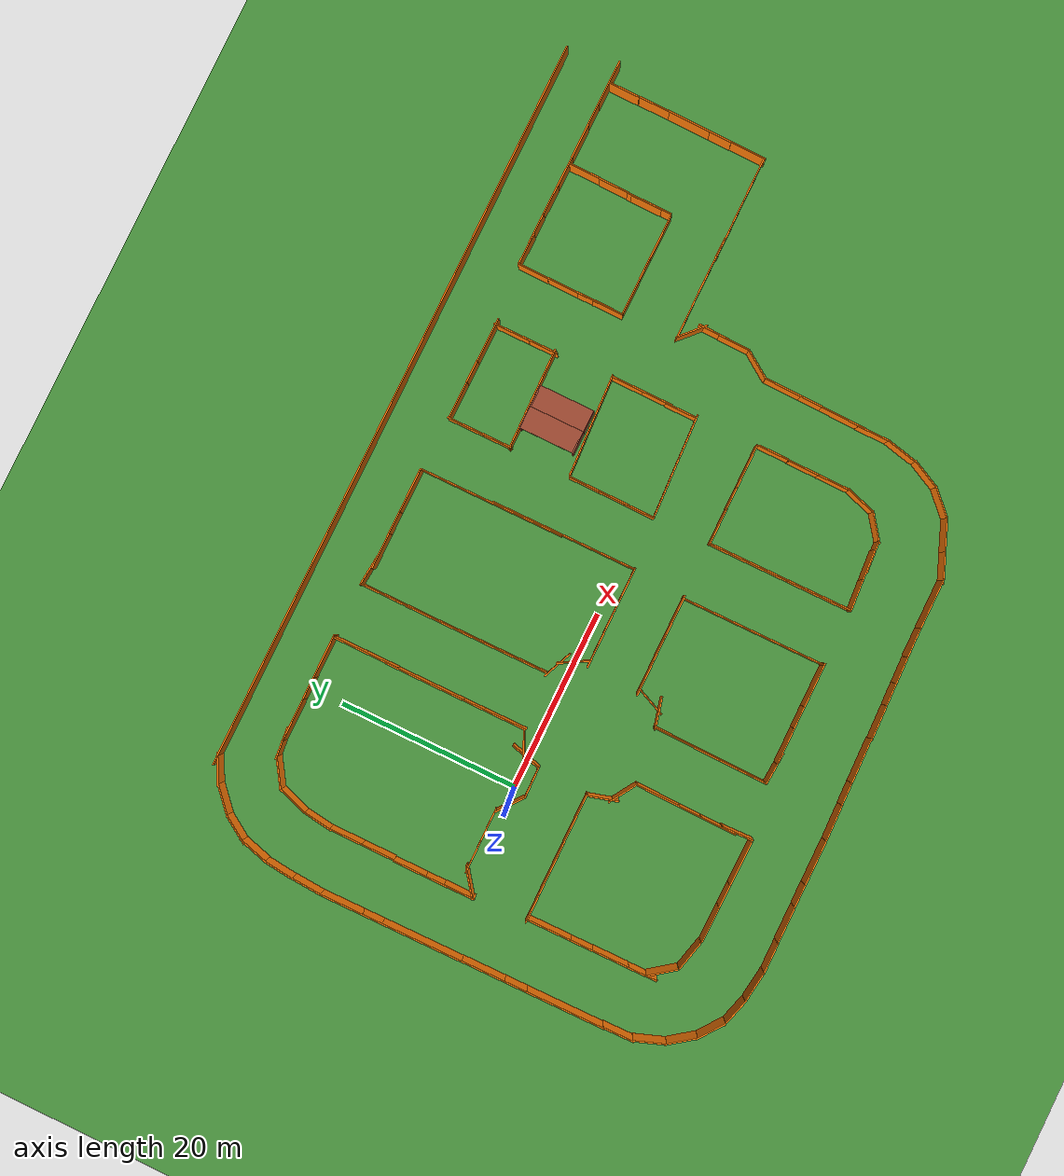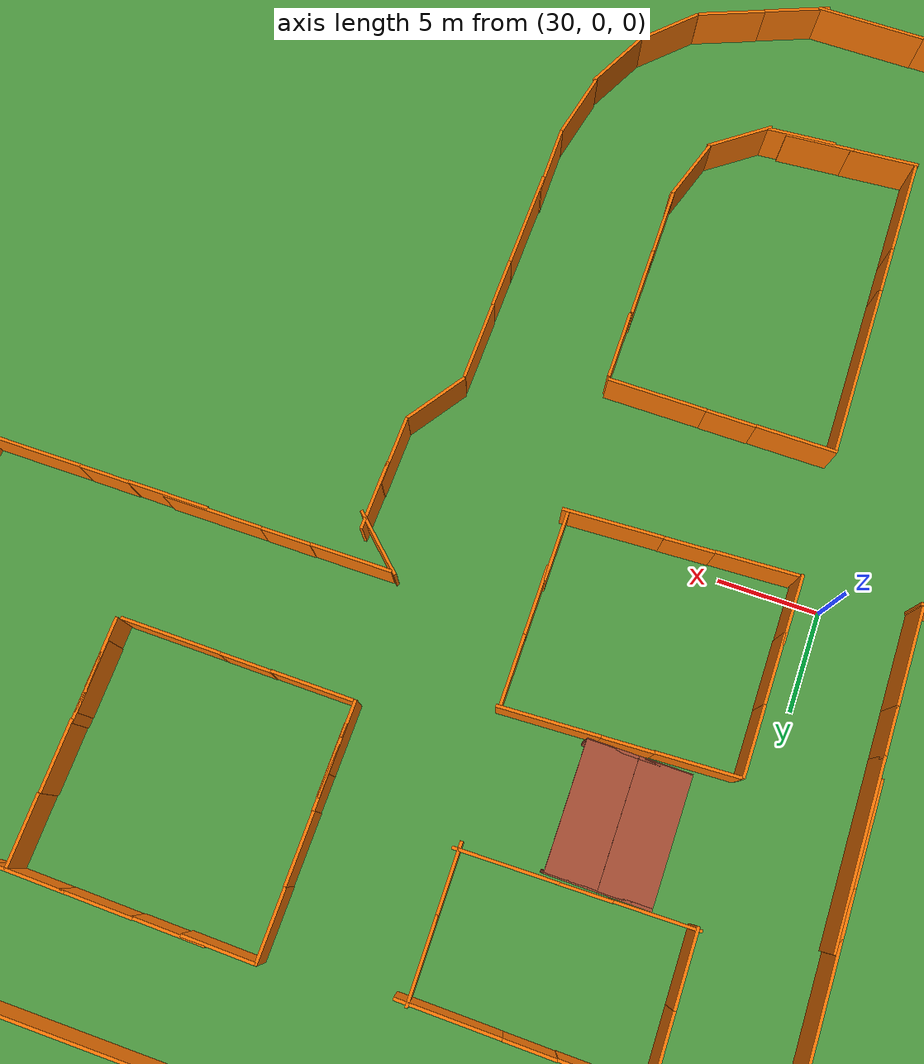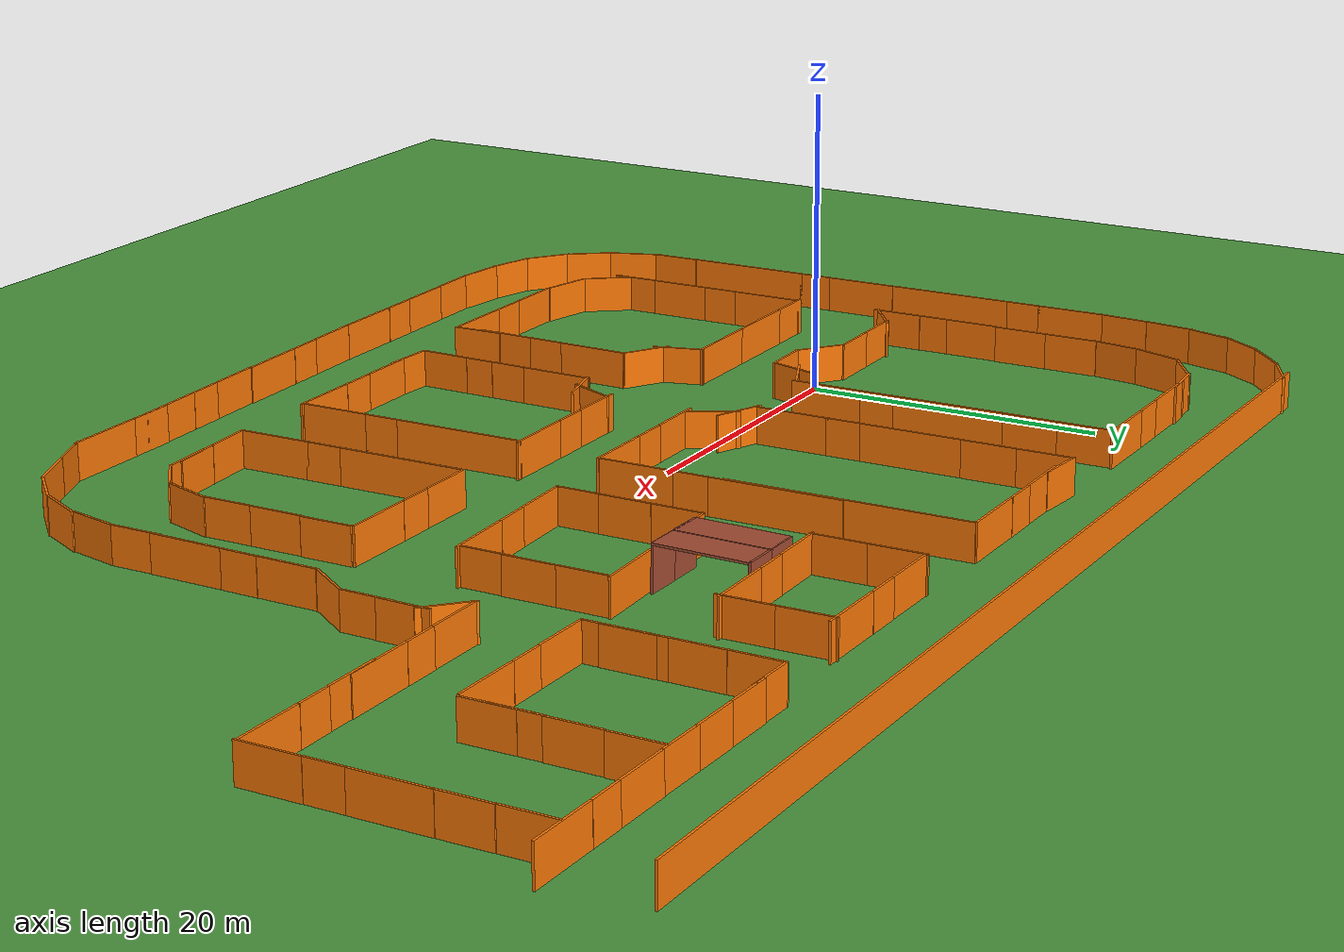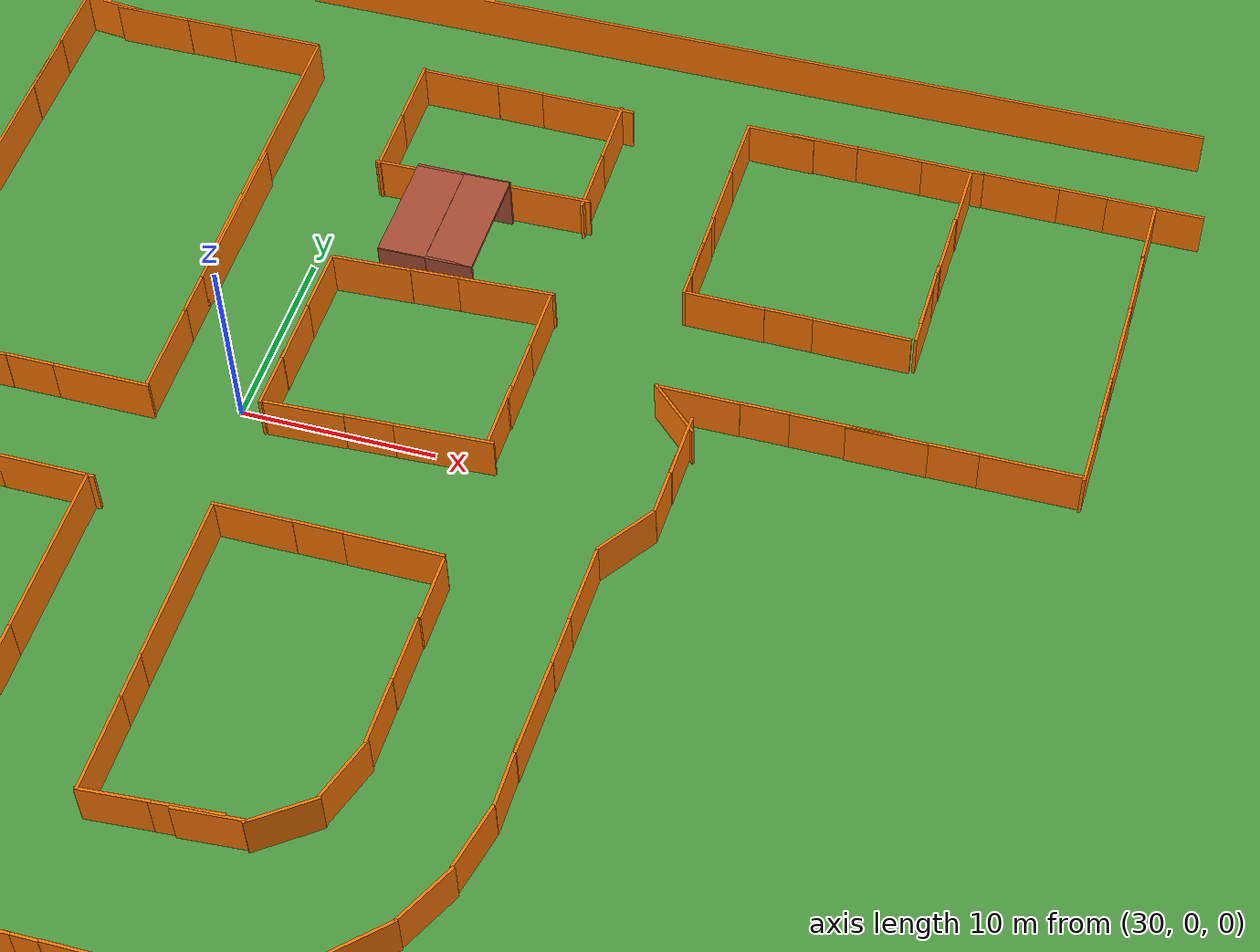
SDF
<sdf version="1.7">
 <world name="cimen_zemin_dunyasi">
  <light name="sun" type="directional">
   <pose>0 0 10 0 -0 0</pose>
   <diffuse>0.8 0.8 0.8 1</diffuse>
   <specular>0.2 0.2 0.2 1</specular>
   <attenuation>
    <range>1000</range>
    <constant>0.9</constant>
    <linear>0.01</linear>
    <quadratic>0.001</quadratic>
   </attenuation>
   <direction>-0.5 0.1 -0.9</direction>
   <spot><inner_angle>0</inner_angle><outer_angle>0</outer_angle><falloff>0</falloff></spot>
  </light>
  <model name="cimen_zemin">
   <static>1</static>
   <pose>-4.07306 2.53992 0 0 -0 0</pose>
   <link name="zemin_linki">
    <collision name="zemin_collision">
     <geometry><box><size>250 250 0.1</size></box></geometry>
     <surface><friction><ode><mu>1</mu><mu2>1</mu2></ode></friction></surface>
    </collision>
    <visual name="zemin_visual">
     <geometry><box><size>250 250 0.1</size></box></geometry>
     <material>
      <script><uri>file://media/materials/scripts/gazebo.material</uri><name>Gazebo/Grass</name></script>
     </material>
    </visual>
   </link>
  </model>
  <gravity>0 0 -9.8</gravity>
  <magnetic_field>6e-06 2.3e-05 -4.2e-05</magnetic_field>
  <atmosphere type="adiabatic"/>
  <physics type="ode">
   <max_step_size>0.001</max_step_size>
   <real_time_factor>1</real_time_factor>
   <real_time_update_rate>1000</real_time_update_rate>
  </physics>
  <scene><ambient>0.4 0.4 0.4 1</ambient><background>0.7 0.7 0.7 1</background><shadows>1</shadows></scene>
  <audio><device>default</device></audio>
  <spherical_coordinates>
   <surface_model>EARTH_WGS84</surface_model>
   <latitude_deg>0</latitude_deg>
   <longitude_deg>0</longitude_deg>
   <elevation>0</elevation>
   <heading_deg>0</heading_deg>
  </spherical_coordinates>
  <light name="user_directional_light_0" type="directional">
   <pose>9.68934 -4.24575 1 0 -0 0</pose>
   <diffuse>0.5 0.5 0.5 1</diffuse>
   <specular>0.1 0.1 0.1 1</specular>
   <direction>0.1 0.1 -0.9</direction>
   <attenuation>
    <range>20</range>
    <constant>0.5</constant>
    <linear>0.01</linear>
    <quadratic>0.001</quadratic>
   </attenuation>
   <spot><inner_angle>0</inner_angle><outer_angle>0</outer_angle><falloff>0</falloff></spot>
  </light>
  <light name="user_directional_light_1" type="directional">
   <pose>20.6305 1.6621 1 0 -0 0</pose>
   <diffuse>0.5 0.5 0.5 1</diffuse>
   <specular>0.1 0.1 0.1 1</specular>
   <direction>0.1 0.1 -0.9</direction>
   <attenuation>
    <range>20</range>
    <constant>0.5</constant>
    <linear>0.01</linear>
    <quadratic>0.001</quadratic>
   </attenuation>
   <spot><inner_angle>0</inner_angle><outer_angle>0</outer_angle><falloff>0</falloff></spot>
  </light>
  <light name="user_directional_light_2" type="directional">
   <pose>12.9122 5.03939 1 0 -0 0</pose>
   <diffuse>0.5 0.5 0.5 1</diffuse>
   <specular>0.1 0.1 0.1 1</specular>
   <direction>0.1 0.1 -0.9</direction>
   <attenuation>
    <range>20</range>
    <constant>0.5</constant>
    <linear>0.01</linear>
    <quadratic>0.001</quadratic>
   </attenuation>
   <spot><inner_angle>0</inner_angle><outer_angle>0</outer_angle><falloff>0</falloff></spot>
  </light>
  <light name="user_directional_light_3" type="directional">
   <pose>34.3713 -10.084 1 0 -0 0</pose>
   <diffuse>0.5 0.5 0.5 1</diffuse>
   <specular>0.1 0.1 0.1 1</specular>
   <direction>0.1 0.1 -0.9</direction>
   <attenuation>
    <range>20</range>
    <constant>0.5</constant>
    <linear>0.01</linear>
    <quadratic>0.001</quadratic>
   </attenuation>
   <spot><inner_angle>0</inner_angle><outer_angle>0</outer_angle><falloff>0</falloff></spot>
  </light>
  <light name="user_directional_light_4" type="directional">
   <pose>10.9875 -10.8144 1 0 -0 0</pose>
   <diffuse>0.5 0.5 0.5 1</diffuse>
   <specular>0.1 0.1 0.1 1</specular>
   <direction>0.1 0.1 -0.9</direction>
   <attenuation>
    <range>20</range>
    <constant>0.5</constant>
    <linear>0.01</linear>
    <quadratic>0.001</quadratic>
   </attenuation>
   <spot><inner_angle>0</inner_angle><outer_angle>0</outer_angle><falloff>0</falloff></spot>
  </light>
  <light name="user_directional_light_5" type="directional">
   <pose>10.1121 10.2606 1 0 -0 0</pose>
   <diffuse>0.5 0.5 0.5 1</diffuse>
   <specular>0.1 0.1 0.1 1</specular>
   <direction>0.1 0.1 -0.9</direction>
   <attenuation>
    <range>20</range>
    <constant>0.5</constant>
    <linear>0.01</linear>
    <quadratic>0.001</quadratic>
   </attenuation>
   <spot><inner_angle>0</inner_angle><outer_angle>0</outer_angle><falloff>0</falloff></spot>
  </light>
  <model name="barrier">
   <pose>30.5966 30.6965 0 0 -0 0</pose>
   <link name="Wall_0">
    <collision name="Wall_0_Collision">
     <geometry><box><size>83.5 0.15 2.5</size></box></geometry>
     <pose>0 0 1.25 0 -0 0</pose>
    </collision>
    <visual name="Wall_0_Visual">
     <pose>0 0 1.25 0 -0 0</pose>
     <geometry><box><size>83.5 0.15 2.5</size></box></geometry>
     <material>
      <script><uri>file://media/materials/scripts/gazebo.material</uri><name>Gazebo/Grey</name></script>
      <ambient>0.996078 0.47451 0.0196078 1</ambient>
     </material>
     <meta><layer>0</layer></meta>
    </visual>
    <pose>-2e-06 -1.7575 0 0 -0 0</pose>
   </link>
   <static>1</static>
  </model>
  <model name="barier3">
   <pose>8.34987 9.56962 0 0 0 -1.56341</pose>
   <link name="Wall_5">
    <collision name="Wall_5_Collision">
     <geometry><box><size>9 0.15 2.5</size></box></geometry>
     <pose>0 0 1.25 0 -0 0</pose>
    </collision>
    <visual name="Wall_5_Visual">
     <pose>0 0 1.25 0 -0 0</pose>
     <geometry><box><size>9 0.15 2.5</size></box></geometry>
     <material>
      <script><uri>file://media/materials/scripts/gazebo.material</uri><name>Gazebo/Grey</name></script>
      <ambient>0.996078 0.47451 0.0196078 1</ambient>
     </material>
     <meta><layer>0</layer></meta>
    </visual>
    <pose>-3.6 -2.29057 0 0 -0 0</pose>
   </link>
   <link name="Wall_7">
    <collision name="Wall_7_Collision">
     <geometry><box><size>2.5 0.15 2.5</size></box></geometry>
     <pose>0 0 1.25 0 -0 0</pose>
    </collision>
    <visual name="Wall_7_Visual">
     <pose>0 0 1.25 0 -0 0</pose>
     <geometry><box><size>2.5 0.15 2.5</size></box></geometry>
     <material>
      <script><uri>file://media/materials/scripts/gazebo.material</uri><name>Gazebo/Grey</name></script>
      <ambient>0.996078 0.47451 0.0196078 1</ambient>
     </material>
     <meta><layer>0</layer></meta>
    </visual>
    <pose>2 -2.29057 0 0 -0 0</pose>
   </link>
   <link name="Wall_9">
    <collision name="Wall_9_Collision">
     <geometry><box><size>5 0.15 2.5</size></box></geometry>
     <pose>0 0 1.25 0 -0 0</pose>
    </collision>
    <visual name="Wall_9_Visual">
     <pose>0 0 1.25 0 -0 0</pose>
     <geometry><box><size>5 0.15 2.5</size></box></geometry>
     <material>
      <script><uri>file://media/materials/scripts/gazebo.material</uri><name>Gazebo/Grey</name></script>
      <ambient>0.996078 0.47451 0.0196078 1</ambient>
     </material>
     <meta><layer>0</layer></meta>
    </visual>
    <pose>5.6 -2.29057 0 0 -0 0</pose>
   </link>
   <static>1</static>
  </model>
  <model name="barier3_clone_clone_clone">
   <link name="Wall_5">
    <pose>-1.71579 -2.31114 0 0 -0 0</pose>
    <inertial>
     <inertia><ixx>0</ixx><ixy>0</ixy><ixz>0</ixz><iyy>0</iyy><iyz>0</iyz><izz>0</izz></inertia>
     <mass>0</mass>
    </inertial>
    <visual name="Wall_5_Visual">
     <pose>0 0 1.25 0 -0 0</pose>
     <geometry><box><size>4.94626 0.15 2.5</size></box></geometry>
     <material>
      <script><uri>file://media/materials/scripts/gazebo.material</uri><name>Gazebo/Grey</name></script>
      <ambient>0.996078 0.47451 0.0196078 1</ambient>
      <shader type="pixel"/>
     </material>
     <meta><layer>0</layer></meta>
    </visual>
    <collision name="Wall_5_Collision">
     <pose>0 0 1.25 0 -0 0</pose>
     <geometry><box><size>4.94626 0.15 2.5</size></box></geometry>
     <surface>
      <friction>
       <ode><mu>1</mu><mu2>1</mu2><fdir1>0 0 0</fdir1><slip1>0</slip1><slip2>0</slip2></ode>
       <torsional>
        <coefficient>1</coefficient>
        <patch_radius>0</patch_radius>
        <surface_radius>0</surface_radius>
        <use_patch_radius>1</use_patch_radius>
        <ode><slip>0</slip></ode>
       </torsional>
      </friction>
      <bounce><restitution_coefficient>0</restitution_coefficient><threshold>1e+06</threshold></bounce>
      <contact>
       <collide_without_contact>0</collide_without_contact>
       <collide_without_contact_bitmask>1</collide_without_contact_bitmask>
       <collide_bitmask>1</collide_bitmask>
       <ode>
        <soft_cfm>0</soft_cfm>
        <soft_erp>0.2</soft_erp>
        <kp>1e+13</kp>
        <kd>1</kd>
        <max_vel>0.01</max_vel>
        <min_depth>0</min_depth>
       </ode>
       <bullet>
        <split_impulse>1</split_impulse>
        <split_impulse_penetration_threshold>-0.01</split_impulse_penetration_threshold>
        <soft_cfm>0</soft_cfm>
        <soft_erp>0.2</soft_erp>
        <kp>1e+13</kp>
        <kd>1</kd>
       </bullet>
      </contact>
     </surface>
    </collision>
   </link>
   <link name="Wall_7">
    <pose>2 -2.29057 0 0 -0 0</pose>
    <visual name="Wall_7_Visual">
     <pose>0 0 1.25 0 -0 0</pose>
     <geometry><box><size>2.5 0.15 2.5</size></box></geometry>
     <material>
      <script><uri>file://media/materials/scripts/gazebo.material</uri><name>Gazebo/Grey</name></script>
      <ambient>0.996078 0.47451 0.0196078 1</ambient>
      <shader type="pixel"/>
     </material>
     <meta><layer>0</layer></meta>
    </visual>
    <collision name="Wall_7_Collision">
     <pose>0 0 1.25 0 -0 0</pose>
     <geometry><box><size>2.5 0.15 2.5</size></box></geometry>
     <surface>
      <friction>
       <ode><mu>1</mu><mu2>1</mu2><fdir1>0 0 0</fdir1><slip1>0</slip1><slip2>0</slip2></ode>
       <torsional>
        <coefficient>1</coefficient>
        <patch_radius>0</patch_radius>
        <surface_radius>0</surface_radius>
        <use_patch_radius>1</use_patch_radius>
        <ode><slip>0</slip></ode>
       </torsional>
      </friction>
      <bounce><restitution_coefficient>0</restitution_coefficient><threshold>1e+06</threshold></bounce>
      <contact>
       <collide_without_contact>0</collide_without_contact>
       <collide_without_contact_bitmask>1</collide_without_contact_bitmask>
       <collide_bitmask>1</collide_bitmask>
       <ode>
        <soft_cfm>0</soft_cfm>
        <soft_erp>0.2</soft_erp>
        <kp>1e+13</kp>
        <kd>1</kd>
        <max_vel>0.01</max_vel>
        <min_depth>0</min_depth>
       </ode>
       <bullet>
        <split_impulse>1</split_impulse>
        <split_impulse_penetration_threshold>-0.01</split_impulse_penetration_threshold>
        <soft_cfm>0</soft_cfm>
        <soft_erp>0.2</soft_erp>
        <kp>1e+13</kp>
        <kd>1</kd>
       </bullet>
      </contact>
     </surface>
    </collision>
   </link>
   <link name="Wall_9">
    <pose>5.6 -2.29057 0 0 -0 0</pose>
    <visual name="Wall_9_Visual">
     <pose>0 0 1.25 0 -0 0</pose>
     <geometry><box><size>5 0.15 2.5</size></box></geometry>
     <material>
      <script><uri>file://media/materials/scripts/gazebo.material</uri><name>Gazebo/Grey</name></script>
      <ambient>0.996078 0.47451 0.0196078 1</ambient>
      <shader type="pixel"/>
     </material>
     <meta><layer>0</layer></meta>
    </visual>
    <collision name="Wall_9_Collision">
     <pose>0 0 1.25 0 -0 0</pose>
     <geometry><box><size>5 0.15 2.5</size></box></geometry>
     <surface>
      <friction>
       <ode><mu>1</mu><mu2>1</mu2><fdir1>0 0 0</fdir1><slip1>0</slip1><slip2>0</slip2></ode>
       <torsional>
        <coefficient>1</coefficient>
        <patch_radius>0</patch_radius>
        <surface_radius>0</surface_radius>
        <use_patch_radius>1</use_patch_radius>
        <ode><slip>0</slip></ode>
       </torsional>
      </friction>
      <bounce><restitution_coefficient>0</restitution_coefficient><threshold>1e+06</threshold></bounce>
      <contact>
       <collide_without_contact>0</collide_without_contact>
       <collide_without_contact_bitmask>1</collide_without_contact_bitmask>
       <collide_bitmask>1</collide_bitmask>
       <ode>
        <soft_cfm>0</soft_cfm>
        <soft_erp>0.2</soft_erp>
        <kp>1e+13</kp>
        <kd>1</kd>
        <max_vel>0.01</max_vel>
        <min_depth>0</min_depth>
       </ode>
       <bullet>
        <split_impulse>1</split_impulse>
        <split_impulse_penetration_threshold>-0.01</split_impulse_penetration_threshold>
        <soft_cfm>0</soft_cfm>
        <soft_erp>0.2</soft_erp>
        <kp>1e+13</kp>
        <kd>1</kd>
       </bullet>
      </contact>
     </surface>
    </collision>
   </link>
   <static>1</static>
   <pose>-1.81563 25.8917 0 0 -0 0</pose>
  </model>
  <model name="barier3_clone_clone_clone_clone_0_clone_clone_clone_clone_0_clone">
   <link name="Wall_5">
    <pose>-0.876122 -2.31251 -0.000674 0 -0 0</pose>
    <inertial>
     <inertia><ixx>0</ixx><ixy>0</ixy><ixz>0</ixz><iyy>0</iyy><iyz>0</iyz><izz>0</izz></inertia>
     <mass>0</mass>
    </inertial>
    <visual name="Wall_5_Visual">
     <pose>0 0 1.25 0 -0 0</pose>
     <geometry><box><size>3.28339 0.15 2.5</size></box></geometry>
     <material>
      <script><uri>file://media/materials/scripts/gazebo.material</uri><name>Gazebo/Grey</name></script>
      <ambient>0.996078 0.47451 0.0196078 1</ambient>
      <shader type="pixel"/>
     </material>
     <meta><layer>0</layer></meta>
    </visual>
    <collision name="Wall_5_Collision">
     <pose>0 0 1.25 0 -0 0</pose>
     <geometry><box><size>3.28339 0.15 2.5</size></box></geometry>
     <surface>
      <friction>
       <ode><mu>1</mu><mu2>1</mu2><fdir1>0 0 0</fdir1><slip1>0</slip1><slip2>0</slip2></ode>
       <torsional>
        <coefficient>1</coefficient>
        <patch_radius>0</patch_radius>
        <surface_radius>0</surface_radius>
        <use_patch_radius>1</use_patch_radius>
        <ode><slip>0</slip></ode>
       </torsional>
      </friction>
      <bounce><restitution_coefficient>0</restitution_coefficient><threshold>1e+06</threshold></bounce>
      <contact>
       <collide_without_contact>0</collide_without_contact>
       <collide_without_contact_bitmask>1</collide_without_contact_bitmask>
       <collide_bitmask>1</collide_bitmask>
       <ode>
        <soft_cfm>0</soft_cfm>
        <soft_erp>0.2</soft_erp>
        <kp>1e+13</kp>
        <kd>1</kd>
        <max_vel>0.01</max_vel>
        <min_depth>0</min_depth>
       </ode>
       <bullet>
        <split_impulse>1</split_impulse>
        <split_impulse_penetration_threshold>-0.01</split_impulse_penetration_threshold>
        <soft_cfm>0</soft_cfm>
        <soft_erp>0.2</soft_erp>
        <kp>1e+13</kp>
        <kd>1</kd>
       </bullet>
      </contact>
     </surface>
    </collision>
   </link>
   <link name="Wall_9">
    <pose>3.5903 -2.29153 0.020971 0 -0 0</pose>
    <inertial>
     <inertia><ixx>0</ixx><ixy>0</ixy><ixz>0</ixz><iyy>0</iyy><iyz>0</iyz><izz>0</izz></inertia>
     <mass>0</mass>
    </inertial>
    <visual name="Wall_9_Visual">
     <pose>0 0 1.25 0 -0 0</pose>
     <geometry><box><size>5.65108 0.15 2.5</size></box></geometry>
     <material>
      <script><uri>file://media/materials/scripts/gazebo.material</uri><name>Gazebo/Grey</name></script>
      <ambient>0.996078 0.47451 0.0196078 1</ambient>
      <shader type="pixel"/>
     </material>
     <meta><layer>0</layer></meta>
    </visual>
    <collision name="Wall_9_Collision">
     <pose>0 0 1.25 0 -0 0</pose>
     <geometry><box><size>5.65108 0.15 2.5</size></box></geometry>
     <surface>
      <friction>
       <ode><mu>1</mu><mu2>1</mu2><fdir1>0 0 0</fdir1><slip1>0</slip1><slip2>0</slip2></ode>
       <torsional>
        <coefficient>1</coefficient>
        <patch_radius>0</patch_radius>
        <surface_radius>0</surface_radius>
        <use_patch_radius>1</use_patch_radius>
        <ode><slip>0</slip></ode>
       </torsional>
      </friction>
      <bounce><restitution_coefficient>0</restitution_coefficient><threshold>1e+06</threshold></bounce>
      <contact>
       <collide_without_contact>0</collide_without_contact>
       <collide_without_contact_bitmask>1</collide_without_contact_bitmask>
       <collide_bitmask>1</collide_bitmask>
       <ode>
        <soft_cfm>0</soft_cfm>
        <soft_erp>0.2</soft_erp>
        <kp>1e+13</kp>
        <kd>1</kd>
        <max_vel>0.01</max_vel>
        <min_depth>0</min_depth>
       </ode>
       <bullet>
        <split_impulse>1</split_impulse>
        <split_impulse_penetration_threshold>-0.01</split_impulse_penetration_threshold>
        <soft_cfm>0</soft_cfm>
        <soft_erp>0.2</soft_erp>
        <kp>1e+13</kp>
        <kd>1</kd>
       </bullet>
      </contact>
     </surface>
    </collision>
   </link>
   <static>1</static>
   <pose>-3.50952 -4.75677 0 0 -0 0</pose>
  </model>
  <model name="barier3_clone_clone_clone_clone_0_clone_clone">
   <link name="Wall_5">
    <pose>-1.25417 -2.31114 0 0 -0 0</pose>
    <inertial>
     <inertia><ixx>0</ixx><ixy>0</ixy><ixz>0</ixz><iyy>0</iyy><iyz>0</iyz><izz>0</izz></inertia>
     <mass>0</mass>
    </inertial>
    <visual name="Wall_5_Visual">
     <pose>0 0 1.25 0 -0 0</pose>
     <geometry><box><size>4.04839 0.15 2.5</size></box></geometry>
     <material>
      <script><uri>file://media/materials/scripts/gazebo.material</uri><name>Gazebo/Grey</name></script>
      <ambient>0.996078 0.47451 0.0196078 1</ambient>
      <shader type="pixel"/>
     </material>
     <meta><layer>0</layer></meta>
    </visual>
    <collision name="Wall_5_Collision">
     <pose>0 0 1.25 0 -0 0</pose>
     <geometry><box><size>4.04839 0.15 2.5</size></box></geometry>
     <surface>
      <friction>
       <ode><mu>1</mu><mu2>1</mu2><fdir1>0 0 0</fdir1><slip1>0</slip1><slip2>0</slip2></ode>
       <torsional>
        <coefficient>1</coefficient>
        <patch_radius>0</patch_radius>
        <surface_radius>0</surface_radius>
        <use_patch_radius>1</use_patch_radius>
        <ode><slip>0</slip></ode>
       </torsional>
      </friction>
      <bounce><restitution_coefficient>0</restitution_coefficient><threshold>1e+06</threshold></bounce>
      <contact>
       <collide_without_contact>0</collide_without_contact>
       <collide_without_contact_bitmask>1</collide_without_contact_bitmask>
       <collide_bitmask>1</collide_bitmask>
       <ode>
        <soft_cfm>0</soft_cfm>
        <soft_erp>0.2</soft_erp>
        <kp>1e+13</kp>
        <kd>1</kd>
        <max_vel>0.01</max_vel>
        <min_depth>0</min_depth>
       </ode>
       <bullet>
        <split_impulse>1</split_impulse>
        <split_impulse_penetration_threshold>-0.01</split_impulse_penetration_threshold>
        <soft_cfm>0</soft_cfm>
        <soft_erp>0.2</soft_erp>
        <kp>1e+13</kp>
        <kd>1</kd>
       </bullet>
      </contact>
     </surface>
    </collision>
   </link>
   <link name="Wall_7">
    <pose>2 -2.29057 0 0 -0 0</pose>
    <visual name="Wall_7_Visual">
     <pose>0 0 1.25 0 -0 0</pose>
     <geometry><box><size>2.5 0.15 2.5</size></box></geometry>
     <material>
      <script><uri>file://media/materials/scripts/gazebo.material</uri><name>Gazebo/Grey</name></script>
      <ambient>0.996078 0.47451 0.0196078 1</ambient>
      <shader type="pixel"/>
     </material>
     <meta><layer>0</layer></meta>
    </visual>
    <collision name="Wall_7_Collision">
     <pose>0 0 1.25 0 -0 0</pose>
     <geometry><box><size>2.5 0.15 2.5</size></box></geometry>
     <surface>
      <friction>
       <ode><mu>1</mu><mu2>1</mu2><fdir1>0 0 0</fdir1><slip1>0</slip1><slip2>0</slip2></ode>
       <torsional>
        <coefficient>1</coefficient>
        <patch_radius>0</patch_radius>
        <surface_radius>0</surface_radius>
        <use_patch_radius>1</use_patch_radius>
        <ode><slip>0</slip></ode>
       </torsional>
      </friction>
      <bounce><restitution_coefficient>0</restitution_coefficient><threshold>1e+06</threshold></bounce>
      <contact>
       <collide_without_contact>0</collide_without_contact>
       <collide_without_contact_bitmask>1</collide_without_contact_bitmask>
       <collide_bitmask>1</collide_bitmask>
       <ode>
        <soft_cfm>0</soft_cfm>
        <soft_erp>0.2</soft_erp>
        <kp>1e+13</kp>
        <kd>1</kd>
        <max_vel>0.01</max_vel>
        <min_depth>0</min_depth>
       </ode>
       <bullet>
        <split_impulse>1</split_impulse>
        <split_impulse_penetration_threshold>-0.01</split_impulse_penetration_threshold>
        <soft_cfm>0</soft_cfm>
        <soft_erp>0.2</soft_erp>
        <kp>1e+13</kp>
        <kd>1</kd>
       </bullet>
      </contact>
     </surface>
    </collision>
   </link>
   <link name="Wall_9">
    <pose>5.71906 -2.30051 0 0 -0 0</pose>
    <inertial>
     <inertia><ixx>0</ixx><ixy>0</ixy><ixz>0</ixz><iyy>0</iyy><iyz>0</iyz><izz>0</izz></inertia>
     <mass>0</mass>
    </inertial>
    <visual name="Wall_9_Visual">
     <pose>0 0 1.25 0 -0 0</pose>
     <geometry><box><size>4.97607 0.15 2.5</size></box></geometry>
     <material>
      <script><uri>file://media/materials/scripts/gazebo.material</uri><name>Gazebo/Grey</name></script>
      <ambient>0.996078 0.47451 0.0196078 1</ambient>
      <shader type="pixel"/>
     </material>
     <meta><layer>0</layer></meta>
    </visual>
    <collision name="Wall_9_Collision">
     <pose>0 0 1.25 0 -0 0</pose>
     <geometry><box><size>4.97607 0.15 2.5</size></box></geometry>
     <surface>
      <friction>
       <ode><mu>1</mu><mu2>1</mu2><fdir1>0 0 0</fdir1><slip1>0</slip1><slip2>0</slip2></ode>
       <torsional>
        <coefficient>1</coefficient>
        <patch_radius>0</patch_radius>
        <surface_radius>0</surface_radius>
        <use_patch_radius>1</use_patch_radius>
        <ode><slip>0</slip></ode>
       </torsional>
      </friction>
      <bounce><restitution_coefficient>0</restitution_coefficient><threshold>1e+06</threshold></bounce>
      <contact>
       <collide_without_contact>0</collide_without_contact>
       <collide_without_contact_bitmask>1</collide_without_contact_bitmask>
       <collide_bitmask>1</collide_bitmask>
       <ode>
        <soft_cfm>0</soft_cfm>
        <soft_erp>0.2</soft_erp>
        <kp>1e+13</kp>
        <kd>1</kd>
        <max_vel>0.01</max_vel>
        <min_depth>0</min_depth>
       </ode>
       <bullet>
        <split_impulse>1</split_impulse>
        <split_impulse_penetration_threshold>-0.01</split_impulse_penetration_threshold>
        <soft_cfm>0</soft_cfm>
        <soft_erp>0.2</soft_erp>
        <kp>1e+13</kp>
        <kd>1</kd>
       </bullet>
      </contact>
     </surface>
    </collision>
   </link>
   <static>1</static>
   <pose>17.8658 0.91508 0 0 -0 0</pose>
  </model>
  <model name="barier3_clone_clone_clone_clone_0_clone_clone_clone_clone_0_clone_0">
   <link name="Wall_5">
    <pose>-0.876122 -2.31251 -0.000674 0 -0 0</pose>
    <inertial>
     <inertia><ixx>0</ixx><ixy>0</ixy><ixz>0</ixz><iyy>0</iyy><iyz>0</iyz><izz>0</izz></inertia>
     <mass>0</mass>
    </inertial>
    <visual name="Wall_5_Visual">
     <pose>0 0 1.25 0 -0 0</pose>
     <geometry><box><size>3.28339 0.15 2.5</size></box></geometry>
     <material>
      <script><uri>file://media/materials/scripts/gazebo.material</uri><name>Gazebo/Grey</name></script>
      <ambient>0.996078 0.47451 0.0196078 1</ambient>
      <shader type="pixel"/>
     </material>
     <meta><layer>0</layer></meta>
    </visual>
    <collision name="Wall_5_Collision">
     <pose>0 0 1.25 0 -0 0</pose>
     <geometry><box><size>3.28339 0.15 2.5</size></box></geometry>
     <surface>
      <friction>
       <ode><mu>1</mu><mu2>1</mu2><fdir1>0 0 0</fdir1><slip1>0</slip1><slip2>0</slip2></ode>
       <torsional>
        <coefficient>1</coefficient>
        <patch_radius>0</patch_radius>
        <surface_radius>0</surface_radius>
        <use_patch_radius>1</use_patch_radius>
        <ode><slip>0</slip></ode>
       </torsional>
      </friction>
      <bounce><restitution_coefficient>0</restitution_coefficient><threshold>1e+06</threshold></bounce>
      <contact>
       <collide_without_contact>0</collide_without_contact>
       <collide_without_contact_bitmask>1</collide_without_contact_bitmask>
       <collide_bitmask>1</collide_bitmask>
       <ode>
        <soft_cfm>0</soft_cfm>
        <soft_erp>0.2</soft_erp>
        <kp>1e+13</kp>
        <kd>1</kd>
        <max_vel>0.01</max_vel>
        <min_depth>0</min_depth>
       </ode>
       <bullet>
        <split_impulse>1</split_impulse>
        <split_impulse_penetration_threshold>-0.01</split_impulse_penetration_threshold>
        <soft_cfm>0</soft_cfm>
        <soft_erp>0.2</soft_erp>
        <kp>1e+13</kp>
        <kd>1</kd>
       </bullet>
      </contact>
     </surface>
    </collision>
   </link>
   <link name="Wall_9">
    <pose>3.5903 -2.29153 0.020971 0 -0 0</pose>
    <inertial>
     <inertia><ixx>0</ixx><ixy>0</ixy><ixz>0</ixz><iyy>0</iyy><iyz>0</iyz><izz>0</izz></inertia>
     <mass>0</mass>
    </inertial>
    <visual name="Wall_9_Visual">
     <pose>0 0 1.25 0 -0 0</pose>
     <geometry><box><size>5.65108 0.15 2.5</size></box></geometry>
     <material>
      <script><uri>file://media/materials/scripts/gazebo.material</uri><name>Gazebo/Grey</name></script>
      <ambient>0.996078 0.47451 0.0196078 1</ambient>
      <shader type="pixel"/>
     </material>
     <meta><layer>0</layer></meta>
    </visual>
    <collision name="Wall_9_Collision">
     <pose>0 0 1.25 0 -0 0</pose>
     <geometry><box><size>5.65108 0.15 2.5</size></box></geometry>
     <surface>
      <friction>
       <ode><mu>1</mu><mu2>1</mu2><fdir1>0 0 0</fdir1><slip1>0</slip1><slip2>0</slip2></ode>
       <torsional>
        <coefficient>1</coefficient>
        <patch_radius>0</patch_radius>
        <surface_radius>0</surface_radius>
        <use_patch_radius>1</use_patch_radius>
        <ode><slip>0</slip></ode>
       </torsional>
      </friction>
      <bounce><restitution_coefficient>0</restitution_coefficient><threshold>1e+06</threshold></bounce>
      <contact>
       <collide_without_contact>0</collide_without_contact>
       <collide_without_contact_bitmask>1</collide_without_contact_bitmask>
       <collide_bitmask>1</collide_bitmask>
       <ode>
        <soft_cfm>0</soft_cfm>
        <soft_erp>0.2</soft_erp>
        <kp>1e+13</kp>
        <kd>1</kd>
        <max_vel>0.01</max_vel>
        <min_depth>0</min_depth>
       </ode>
       <bullet>
        <split_impulse>1</split_impulse>
        <split_impulse_penetration_threshold>-0.01</split_impulse_penetration_threshold>
        <soft_cfm>0</soft_cfm>
        <soft_erp>0.2</soft_erp>
        <kp>1e+13</kp>
        <kd>1</kd>
       </bullet>
      </contact>
     </surface>
    </collision>
   </link>
   <static>1</static>
   <pose>-9.11126 -4.76807 0 0 -0 0</pose>
  </model>
  <model name="barrier2">
   <pose>-10.2583 29.644 0 0 -0 0.479879</pose>
   <link name="Wall_3">
    <collision name="Wall_3_Collision">
     <geometry><box><size>3.5 0.15 2.5</size></box></geometry>
     <pose>0 0 1.25 0 -0 0</pose>
    </collision>
    <visual name="Wall_3_Visual">
     <pose>0 0 1.25 0 -0 0</pose>
     <geometry><box><size>3.5 0.15 2.5</size></box></geometry>
     <material>
      <script><uri>file://media/materials/scripts/gazebo.material</uri><name>Gazebo/Grey</name></script>
      <ambient>0.996078 0.47451 0.0196078 1</ambient>
     </material>
     <meta><layer>0</layer></meta>
    </visual>
    <pose>-1.55327 -0.720218 0 0 -0 0</pose>
   </link>
   <static>1</static>
  </model>
  <model name="barrier2_clone">
   <pose>-13.1416 28.1133 0 0 -0 0.741197</pose>
   <link name="Wall_3">
    <collision name="Wall_3_Collision">
     <geometry><box><size>3.5 0.15 2.5</size></box></geometry>
     <pose>0 0 1.25 0 -0 0</pose>
    </collision>
    <visual name="Wall_3_Visual">
     <pose>0 0 1.25 0 -0 0</pose>
     <geometry><box><size>3.5 0.15 2.5</size></box></geometry>
     <material>
      <script><uri>file://media/materials/scripts/gazebo.material</uri><name>Gazebo/Grey</name></script>
      <ambient>0.996078 0.47451 0.0196078 1</ambient>
     </material>
     <meta><layer>0</layer></meta>
    </visual>
    <pose>-1.55327 -0.720218 0 0 -0 0</pose>
   </link>
   <static>1</static>
  </model>
  <model name="barrier2_clone_clone">
   <pose>-15.814 25.6119 0 0 -0 1.00081</pose>
   <link name="Wall_3">
    <collision name="Wall_3_Collision">
     <geometry><box><size>3.5 0.15 2.5</size></box></geometry>
     <pose>0 0 1.25 0 -0 0</pose>
    </collision>
    <visual name="Wall_3_Visual">
     <pose>0 0 1.25 0 -0 0</pose>
     <geometry><box><size>3.5 0.15 2.5</size></box></geometry>
     <material>
      <script><uri>file://media/materials/scripts/gazebo.material</uri><name>Gazebo/Grey</name></script>
      <ambient>0.996078 0.47451 0.0196078 1</ambient>
     </material>
     <meta><layer>0</layer></meta>
    </visual>
    <pose>-1.55327 -0.720218 0 0 -0 0</pose>
   </link>
   <static>1</static>
  </model>
  <model name="barrier2_clone_0">
   <pose>-4.58312 24.4241 0 0 -0 0.100794</pose>
   <link name="Wall_3">
    <collision name="Wall_3_Collision">
     <geometry><box><size>3.5 0.15 2.5</size></box></geometry>
     <pose>0 0 1.25 0 -0 0</pose>
    </collision>
    <visual name="Wall_3_Visual">
     <pose>0 0 1.25 0 -0 0</pose>
     <geometry><box><size>3.5 0.15 2.5</size></box></geometry>
     <material>
      <script><uri>file://media/materials/scripts/gazebo.material</uri><name>Gazebo/Grey</name></script>
      <ambient>0.996078 0.47451 0.0196078 1</ambient>
     </material>
     <meta><layer>0</layer></meta>
    </visual>
    <pose>-1.55327 -0.720218 0 0 -0 0</pose>
   </link>
   <static>1</static>
  </model>
  <model name="barrier2_clone_0_clone">
   <pose>-7.9744 23.9611 0 0 -0 0.576446</pose>
   <link name="Wall_3">
    <collision name="Wall_3_Collision">
     <geometry><box><size>3.5 0.15 2.5</size></box></geometry>
     <pose>0 0 1.25 0 -0 0</pose>
    </collision>
    <visual name="Wall_3_Visual">
     <pose>0 0 1.25 0 -0 0</pose>
     <geometry><box><size>3.5 0.15 2.5</size></box></geometry>
     <material>
      <script><uri>file://media/materials/scripts/gazebo.material</uri><name>Gazebo/Grey</name></script>
      <ambient>0.996078 0.47451 0.0196078 1</ambient>
     </material>
     <meta><layer>0</layer></meta>
    </visual>
    <pose>-1.55327 -0.720218 0 0 -0 0</pose>
   </link>
   <static>1</static>
  </model>
  <model name="barrier2_clone_0_clone_clone">
   <pose>-11.0573 21.664 0 0 -0 1.25855</pose>
   <link name="Wall_3">
    <collision name="Wall_3_Collision">
     <geometry><box><size>3.5 0.15 2.5</size></box></geometry>
     <pose>0 0 1.25 0 -0 0</pose>
    </collision>
    <visual name="Wall_3_Visual">
     <pose>0 0 1.25 0 -0 0</pose>
     <geometry><box><size>3.5 0.15 2.5</size></box></geometry>
     <material>
      <script><uri>file://media/materials/scripts/gazebo.material</uri><name>Gazebo/Grey</name></script>
      <ambient>0.996078 0.47451 0.0196078 1</ambient>
     </material>
     <meta><layer>0</layer></meta>
    </visual>
    <pose>-1.55327 -0.720218 0 0 -0 0</pose>
   </link>
   <static>1</static>
  </model>
  <model name="barrier2_clone_0_clone_clone_clone">
   <pose>-12.102 18.3665 0 0 -0 1.43662</pose>
   <link name="Wall_3">
    <collision name="Wall_3_Collision">
     <geometry><box><size>3.5 0.15 2.5</size></box></geometry>
     <pose>0 0 1.25 0 -0 0</pose>
    </collision>
    <visual name="Wall_3_Visual">
     <pose>0 0 1.25 0 -0 0</pose>
     <geometry><box><size>3.5 0.15 2.5</size></box></geometry>
     <material>
      <script><uri>file://media/materials/scripts/gazebo.material</uri><name>Gazebo/Grey</name></script>
      <ambient>0.996078 0.47451 0.0196078 1</ambient>
     </material>
     <meta><layer>0</layer></meta>
    </visual>
    <pose>-1.55327 -0.720218 0 0 -0 0</pose>
   </link>
   <static>1</static>
  </model>
  <model name="barrier2_clone_clone_clone">
   <pose>-17.4205 23.1156 0 0 -0 1.30186</pose>
   <link name="Wall_3">
    <collision name="Wall_3_Collision">
     <geometry><box><size>3.5 0.15 2.5</size></box></geometry>
     <pose>0 0 1.25 0 -0 0</pose>
    </collision>
    <visual name="Wall_3_Visual">
     <pose>0 0 1.25 0 -0 0</pose>
     <geometry><box><size>3.5 0.15 2.5</size></box></geometry>
     <material>
      <script><uri>file://media/materials/scripts/gazebo.material</uri><name>Gazebo/Grey</name></script>
      <ambient>0.996078 0.47451 0.0196078 1</ambient>
     </material>
     <meta><layer>0</layer></meta>
    </visual>
    <pose>-1.55327 -0.720218 0 0 -0 0</pose>
   </link>
   <static>1</static>
  </model>
  <model name="barrier2_clone_clone_clone_clone">
   <pose>-18.357 19.7461 0 0 -0 1.46324</pose>
   <link name="Wall_3">
    <collision name="Wall_3_Collision">
     <geometry><box><size>3.5 0.15 2.5</size></box></geometry>
     <pose>0 0 1.25 0 -0 0</pose>
    </collision>
    <visual name="Wall_3_Visual">
     <pose>0 0 1.25 0 -0 0</pose>
     <geometry><box><size>3.5 0.15 2.5</size></box></geometry>
     <material>
      <script><uri>file://media/materials/scripts/gazebo.material</uri><name>Gazebo/Grey</name></script>
      <ambient>0.996078 0.47451 0.0196078 1</ambient>
     </material>
     <meta><layer>0</layer></meta>
    </visual>
    <pose>-1.55327 -0.720218 0 0 -0 0</pose>
   </link>
   <static>1</static>
  </model>
  <model name="barrier2_clone_clone_clone_clone_clone">
   <pose>-18.687 16.3208 0 0 -0 1.50893</pose>
   <link name="Wall_3">
    <collision name="Wall_3_Collision">
     <geometry><box><size>3.5 0.15 2.5</size></box></geometry>
     <pose>0 0 1.25 0 -0 0</pose>
    </collision>
    <visual name="Wall_3_Visual">
     <pose>0 0 1.25 0 -0 0</pose>
     <geometry><box><size>3.5 0.15 2.5</size></box></geometry>
     <material>
      <script><uri>file://media/materials/scripts/gazebo.material</uri><name>Gazebo/Grey</name></script>
      <ambient>0.996078 0.47451 0.0196078 1</ambient>
     </material>
     <meta><layer>0</layer></meta>
    </visual>
    <pose>-1.55327 -0.720218 0 0 -0 0</pose>
   </link>
   <static>1</static>
  </model>
  <model name="barier3_0">
   <pose>-20.3436 5.22433 0 0 -0 1.58461</pose>
   <link name="Wall_5">
    <collision name="Wall_5_Collision">
     <geometry><box><size>9 0.15 2.5</size></box></geometry>
     <pose>0 0 1.25 0 -0 0</pose>
    </collision>
    <visual name="Wall_5_Visual">
     <pose>0 0 1.25 0 -0 0</pose>
     <geometry><box><size>9 0.15 2.5</size></box></geometry>
     <material>
      <script><uri>file://media/materials/scripts/gazebo.material</uri><name>Gazebo/Grey</name></script>
      <ambient>0.996078 0.47451 0.0196078 1</ambient>
     </material>
     <meta><layer>0</layer></meta>
    </visual>
    <pose>-3.6 -2.29057 0 0 -0 0</pose>
   </link>
   <link name="Wall_7">
    <collision name="Wall_7_Collision">
     <geometry><box><size>2.5 0.15 2.5</size></box></geometry>
     <pose>0 0 1.25 0 -0 0</pose>
    </collision>
    <visual name="Wall_7_Visual">
     <pose>0 0 1.25 0 -0 0</pose>
     <geometry><box><size>2.5 0.15 2.5</size></box></geometry>
     <material>
      <script><uri>file://media/materials/scripts/gazebo.material</uri><name>Gazebo/Grey</name></script>
      <ambient>0.996078 0.47451 0.0196078 1</ambient>
     </material>
     <meta><layer>0</layer></meta>
    </visual>
    <pose>2 -2.29057 0 0 -0 0</pose>
   </link>
   <link name="Wall_9">
    <collision name="Wall_9_Collision">
     <geometry><box><size>5 0.15 2.5</size></box></geometry>
     <pose>0 0 1.25 0 -0 0</pose>
    </collision>
    <visual name="Wall_9_Visual">
     <pose>0 0 1.25 0 -0 0</pose>
     <geometry><box><size>5 0.15 2.5</size></box></geometry>
     <material>
      <script><uri>file://media/materials/scripts/gazebo.material</uri><name>Gazebo/Grey</name></script>
      <ambient>0.996078 0.47451 0.0196078 1</ambient>
     </material>
     <meta><layer>0</layer></meta>
    </visual>
    <pose>5.6 -2.29057 0 0 -0 0</pose>
   </link>
   <static>1</static>
  </model>
  <model name="barier3_0_clone">
   <pose>-20.0892 -10.9776 0 0 -0 1.58461</pose>
   <link name="Wall_5">
    <collision name="Wall_5_Collision">
     <geometry><box><size>9 0.15 2.5</size></box></geometry>
     <pose>0 0 1.25 0 -0 0</pose>
    </collision>
    <visual name="Wall_5_Visual">
     <pose>0 0 1.25 0 -0 0</pose>
     <geometry><box><size>9 0.15 2.5</size></box></geometry>
     <material>
      <script><uri>file://media/materials/scripts/gazebo.material</uri><name>Gazebo/Grey</name></script>
      <ambient>0.996078 0.47451 0.0196078 1</ambient>
     </material>
     <meta><layer>0</layer></meta>
    </visual>
    <pose>-3.6 -2.29057 0 0 -0 0</pose>
   </link>
   <link name="Wall_7">
    <collision name="Wall_7_Collision">
     <geometry><box><size>2.5 0.15 2.5</size></box></geometry>
     <pose>0 0 1.25 0 -0 0</pose>
    </collision>
    <visual name="Wall_7_Visual">
     <pose>0 0 1.25 0 -0 0</pose>
     <geometry><box><size>2.5 0.15 2.5</size></box></geometry>
     <material>
      <script><uri>file://media/materials/scripts/gazebo.material</uri><name>Gazebo/Grey</name></script>
      <ambient>0.996078 0.47451 0.0196078 1</ambient>
     </material>
     <meta><layer>0</layer></meta>
    </visual>
    <pose>2 -2.29057 0 0 -0 0</pose>
   </link>
   <link name="Wall_9">
    <collision name="Wall_9_Collision">
     <geometry><box><size>5 0.15 2.5</size></box></geometry>
     <pose>0 0 1.25 0 -0 0</pose>
    </collision>
    <visual name="Wall_9_Visual">
     <pose>0 0 1.25 0 -0 0</pose>
     <geometry><box><size>5 0.15 2.5</size></box></geometry>
     <material>
      <script><uri>file://media/materials/scripts/gazebo.material</uri><name>Gazebo/Grey</name></script>
      <ambient>0.996078 0.47451 0.0196078 1</ambient>
     </material>
     <meta><layer>0</layer></meta>
    </visual>
    <pose>5.6 -2.29057 0 0 -0 0</pose>
   </link>
   <static>1</static>
  </model>
  <model name="barier3_clone_clone_clone_clone_0_clone_clone_0_clone">
   <link name="Wall_5">
    <pose>-1.14926 -2.31114 0 0 -0 0</pose>
    <inertial>
     <inertia><ixx>0</ixx><ixy>0</ixy><ixz>0</ixz><iyy>0</iyy><iyz>0</iyz><izz>0</izz></inertia>
     <mass>0</mass>
    </inertial>
    <visual name="Wall_5_Visual">
     <pose>0 0 1.25 0 -0 0</pose>
     <geometry><box><size>4.04839 0.15 2.5</size></box></geometry>
     <material>
      <script><uri>file://media/materials/scripts/gazebo.material</uri><name>Gazebo/Grey</name></script>
      <ambient>0.996078 0.47451 0.0196078 1</ambient>
      <shader type="pixel"/>
     </material>
     <meta><layer>0</layer></meta>
    </visual>
    <collision name="Wall_5_Collision">
     <pose>0 0 1.25 0 -0 0</pose>
     <geometry><box><size>4.04839 0.15 2.5</size></box></geometry>
     <surface>
      <friction>
       <ode><mu>1</mu><mu2>1</mu2><fdir1>0 0 0</fdir1><slip1>0</slip1><slip2>0</slip2></ode>
       <torsional>
        <coefficient>1</coefficient>
        <patch_radius>0</patch_radius>
        <surface_radius>0</surface_radius>
        <use_patch_radius>1</use_patch_radius>
        <ode><slip>0</slip></ode>
       </torsional>
      </friction>
      <bounce><restitution_coefficient>0</restitution_coefficient><threshold>1e+06</threshold></bounce>
      <contact>
       <collide_without_contact>0</collide_without_contact>
       <collide_without_contact_bitmask>1</collide_without_contact_bitmask>
       <collide_bitmask>1</collide_bitmask>
       <ode>
        <soft_cfm>0</soft_cfm>
        <soft_erp>0.2</soft_erp>
        <kp>1e+13</kp>
        <kd>1</kd>
        <max_vel>0.01</max_vel>
        <min_depth>0</min_depth>
       </ode>
       <bullet>
        <split_impulse>1</split_impulse>
        <split_impulse_penetration_threshold>-0.01</split_impulse_penetration_threshold>
        <soft_cfm>0</soft_cfm>
        <soft_erp>0.2</soft_erp>
        <kp>1e+13</kp>
        <kd>1</kd>
       </bullet>
      </contact>
     </surface>
    </collision>
   </link>
   <link name="Wall_9">
    <pose>2.34493 -2.31065 0 0 -0 0</pose>
    <inertial>
     <inertia><ixx>0</ixx><ixy>0</ixy><ixz>0</ixz><iyy>0</iyy><iyz>0</iyz><izz>0</izz></inertia>
     <mass>0</mass>
    </inertial>
    <visual name="Wall_9_Visual">
     <pose>0 0 1.25 0 -0 0</pose>
     <geometry><box><size>3.66586 0.15 2.5</size></box></geometry>
     <material>
      <script><uri>file://media/materials/scripts/gazebo.material</uri><name>Gazebo/Grey</name></script>
      <ambient>0.996078 0.47451 0.0196078 1</ambient>
      <shader type="pixel"/>
     </material>
     <meta><layer>0</layer></meta>
    </visual>
    <collision name="Wall_9_Collision">
     <pose>0 0 1.25 0 -0 0</pose>
     <geometry><box><size>3.66586 0.15 2.5</size></box></geometry>
     <surface>
      <friction>
       <ode><mu>1</mu><mu2>1</mu2><fdir1>0 0 0</fdir1><slip1>0</slip1><slip2>0</slip2></ode>
       <torsional>
        <coefficient>1</coefficient>
        <patch_radius>0</patch_radius>
        <surface_radius>0</surface_radius>
        <use_patch_radius>1</use_patch_radius>
        <ode><slip>0</slip></ode>
       </torsional>
      </friction>
      <bounce><restitution_coefficient>0</restitution_coefficient><threshold>1e+06</threshold></bounce>
      <contact>
       <collide_without_contact>0</collide_without_contact>
       <collide_without_contact_bitmask>1</collide_without_contact_bitmask>
       <collide_bitmask>1</collide_bitmask>
       <ode>
        <soft_cfm>0</soft_cfm>
        <soft_erp>0.2</soft_erp>
        <kp>1e+13</kp>
        <kd>1</kd>
        <max_vel>0.01</max_vel>
        <min_depth>0</min_depth>
       </ode>
       <bullet>
        <split_impulse>1</split_impulse>
        <split_impulse_penetration_threshold>-0.01</split_impulse_penetration_threshold>
        <soft_cfm>0</soft_cfm>
        <soft_erp>0.2</soft_erp>
        <kp>1e+13</kp>
        <kd>1</kd>
       </bullet>
      </contact>
     </surface>
    </collision>
   </link>
   <static>1</static>
   <pose>-9.43805 12.101 0 0 0 -1.56598</pose>
  </model>
  <model name="barier3_clone_clone_clone_clone_0_clone_clone_0_clone_clone">
   <link name="Wall_5">
    <pose>-1.14926 -2.31114 0 0 -0 0</pose>
    <inertial>
     <inertia><ixx>0</ixx><ixy>0</ixy><ixz>0</ixz><iyy>0</iyy><iyz>0</iyz><izz>0</izz></inertia>
     <mass>0</mass>
    </inertial>
    <visual name="Wall_5_Visual">
     <pose>0 0 1.25 0 -0 0</pose>
     <geometry><box><size>4.04839 0.15 2.5</size></box></geometry>
     <material>
      <script><uri>file://media/materials/scripts/gazebo.material</uri><name>Gazebo/Grey</name></script>
      <ambient>0.996078 0.47451 0.0196078 1</ambient>
      <shader type="pixel"/>
     </material>
     <meta><layer>0</layer></meta>
    </visual>
    <collision name="Wall_5_Collision">
     <pose>0 0 1.25 0 -0 0</pose>
     <geometry><box><size>4.04839 0.15 2.5</size></box></geometry>
     <surface>
      <friction>
       <ode><mu>1</mu><mu2>1</mu2><fdir1>0 0 0</fdir1><slip1>0</slip1><slip2>0</slip2></ode>
       <torsional>
        <coefficient>1</coefficient>
        <patch_radius>0</patch_radius>
        <surface_radius>0</surface_radius>
        <use_patch_radius>1</use_patch_radius>
        <ode><slip>0</slip></ode>
       </torsional>
      </friction>
      <bounce><restitution_coefficient>0</restitution_coefficient><threshold>1e+06</threshold></bounce>
      <contact>
       <collide_without_contact>0</collide_without_contact>
       <collide_without_contact_bitmask>1</collide_without_contact_bitmask>
       <collide_bitmask>1</collide_bitmask>
       <ode>
        <soft_cfm>0</soft_cfm>
        <soft_erp>0.2</soft_erp>
        <kp>1e+13</kp>
        <kd>1</kd>
        <max_vel>0.01</max_vel>
        <min_depth>0</min_depth>
       </ode>
       <bullet>
        <split_impulse>1</split_impulse>
        <split_impulse_penetration_threshold>-0.01</split_impulse_penetration_threshold>
        <soft_cfm>0</soft_cfm>
        <soft_erp>0.2</soft_erp>
        <kp>1e+13</kp>
        <kd>1</kd>
       </bullet>
      </contact>
     </surface>
    </collision>
   </link>
   <link name="Wall_9">
    <pose>2.34493 -2.31065 0 0 -0 0</pose>
    <inertial>
     <inertia><ixx>0</ixx><ixy>0</ixy><ixz>0</ixz><iyy>0</iyy><iyz>0</iyz><izz>0</izz></inertia>
     <mass>0</mass>
    </inertial>
    <visual name="Wall_9_Visual">
     <pose>0 0 1.25 0 -0 0</pose>
     <geometry><box><size>3.66586 0.15 2.5</size></box></geometry>
     <material>
      <script><uri>file://media/materials/scripts/gazebo.material</uri><name>Gazebo/Grey</name></script>
      <ambient>0.996078 0.47451 0.0196078 1</ambient>
      <shader type="pixel"/>
     </material>
     <meta><layer>0</layer></meta>
    </visual>
    <collision name="Wall_9_Collision">
     <pose>0 0 1.25 0 -0 0</pose>
     <geometry><box><size>3.66586 0.15 2.5</size></box></geometry>
     <surface>
      <friction>
       <ode><mu>1</mu><mu2>1</mu2><fdir1>0 0 0</fdir1><slip1>0</slip1><slip2>0</slip2></ode>
       <torsional>
        <coefficient>1</coefficient>
        <patch_radius>0</patch_radius>
        <surface_radius>0</surface_radius>
        <use_patch_radius>1</use_patch_radius>
        <ode><slip>0</slip></ode>
       </torsional>
      </friction>
      <bounce><restitution_coefficient>0</restitution_coefficient><threshold>1e+06</threshold></bounce>
      <contact>
       <collide_without_contact>0</collide_without_contact>
       <collide_without_contact_bitmask>1</collide_without_contact_bitmask>
       <collide_bitmask>1</collide_bitmask>
       <ode>
        <soft_cfm>0</soft_cfm>
        <soft_erp>0.2</soft_erp>
        <kp>1e+13</kp>
        <kd>1</kd>
        <max_vel>0.01</max_vel>
        <min_depth>0</min_depth>
       </ode>
       <bullet>
        <split_impulse>1</split_impulse>
        <split_impulse_penetration_threshold>-0.01</split_impulse_penetration_threshold>
        <soft_cfm>0</soft_cfm>
        <soft_erp>0.2</soft_erp>
        <kp>1e+13</kp>
        <kd>1</kd>
       </bullet>
      </contact>
     </surface>
    </collision>
   </link>
   <static>1</static>
   <pose>-9.48925 4.74309 0 0 0 -1.56598</pose>
  </model>
  <model name="barrier2_clone_0_clone_0">
   <pose>-18.3449 -18.9963 0 0 -0 1.59331</pose>
   <link name="Wall_3">
    <collision name="Wall_3_Collision">
     <geometry><box><size>3.5 0.15 2.5</size></box></geometry>
     <pose>0 0 1.25 0 -0 0</pose>
    </collision>
    <visual name="Wall_3_Visual">
     <pose>0 0 1.25 0 -0 0</pose>
     <geometry><box><size>3.5 0.15 2.5</size></box></geometry>
     <material>
      <script><uri>file://media/materials/scripts/gazebo.material</uri><name>Gazebo/Grey</name></script>
      <ambient>0.996078 0.47451 0.0196078 1</ambient>
     </material>
     <meta><layer>0</layer></meta>
    </visual>
    <pose>-1.55327 -0.720218 0 0 -0 0</pose>
   </link>
   <static>1</static>
  </model>
  <model name="barrier2_clone_0_clone_0_clone">
   <pose>-18.1039 -22.5324 0 0 -0 1.91704</pose>
   <link name="Wall_3">
    <collision name="Wall_3_Collision">
     <geometry><box><size>3.5 0.15 2.5</size></box></geometry>
     <pose>0 0 1.25 0 -0 0</pose>
    </collision>
    <visual name="Wall_3_Visual">
     <pose>0 0 1.25 0 -0 0</pose>
     <geometry><box><size>3.5 0.15 2.5</size></box></geometry>
     <material>
      <script><uri>file://media/materials/scripts/gazebo.material</uri><name>Gazebo/Grey</name></script>
      <ambient>0.996078 0.47451 0.0196078 1</ambient>
     </material>
     <meta><layer>0</layer></meta>
    </visual>
    <pose>-1.55327 -0.720218 0 0 -0 0</pose>
   </link>
   <static>1</static>
  </model>
  <model name="barrier2_clone_0_clone_0_clone_clone">
   <pose>-16.9381 -25.7302 0 0 -0 2.21207</pose>
   <link name="Wall_3">
    <collision name="Wall_3_Collision">
     <geometry><box><size>3.5 0.15 2.5</size></box></geometry>
     <pose>0 0 1.25 0 -0 0</pose>
    </collision>
    <visual name="Wall_3_Visual">
     <pose>0 0 1.25 0 -0 0</pose>
     <geometry><box><size>3.5 0.15 2.5</size></box></geometry>
     <material>
      <script><uri>file://media/materials/scripts/gazebo.material</uri><name>Gazebo/Grey</name></script>
      <ambient>0.996078 0.47451 0.0196078 1</ambient>
     </material>
     <meta><layer>0</layer></meta>
    </visual>
    <pose>-1.55327 -0.720218 0 0 -0 0</pose>
   </link>
   <static>1</static>
  </model>
  <model name="barrier2_clone_0_clone_0_clone_clone_clone">
   <pose>-14.8373 -28.5438 0 0 -0 2.49875</pose>
   <link name="Wall_3">
    <collision name="Wall_3_Collision">
     <geometry><box><size>3.5 0.15 2.5</size></box></geometry>
     <pose>0 0 1.25 0 -0 0</pose>
    </collision>
    <visual name="Wall_3_Visual">
     <pose>0 0 1.25 0 -0 0</pose>
     <geometry><box><size>3.5 0.15 2.5</size></box></geometry>
     <material>
      <script><uri>file://media/materials/scripts/gazebo.material</uri><name>Gazebo/Grey</name></script>
      <ambient>0.996078 0.47451 0.0196078 1</ambient>
     </material>
     <meta><layer>0</layer></meta>
    </visual>
    <pose>-1.55327 -0.720218 0 0 -0 0</pose>
   </link>
   <static>1</static>
  </model>
  <model name="barrier2_clone_0_clone_0_clone_clone_clone_clone">
   <pose>-12.0783 -30.5778 0 0 -0 2.85028</pose>
   <link name="Wall_3">
    <collision name="Wall_3_Collision">
     <geometry><box><size>3.5 0.15 2.5</size></box></geometry>
     <pose>0 0 1.25 0 -0 0</pose>
    </collision>
    <visual name="Wall_3_Visual">
     <pose>0 0 1.25 0 -0 0</pose>
     <geometry><box><size>3.5 0.15 2.5</size></box></geometry>
     <material>
      <script><uri>file://media/materials/scripts/gazebo.material</uri><name>Gazebo/Grey</name></script>
      <ambient>0.996078 0.47451 0.0196078 1</ambient>
     </material>
     <meta><layer>0</layer></meta>
    </visual>
    <pose>-1.55327 -0.720218 0 0 -0 0</pose>
   </link>
   <static>1</static>
  </model>
  <model name="barrier2_clone_0_clone_0_clone_clone_clone_clone_clone">
   <pose>-8.84746 -31.4937 0 0 -0 3.00412</pose>
   <link name="Wall_3">
    <collision name="Wall_3_Collision">
     <geometry><box><size>3.5 0.15 2.5</size></box></geometry>
     <pose>0 0 1.25 0 -0 0</pose>
    </collision>
    <visual name="Wall_3_Visual">
     <pose>0 0 1.25 0 -0 0</pose>
     <geometry><box><size>3.5 0.15 2.5</size></box></geometry>
     <material>
      <script><uri>file://media/materials/scripts/gazebo.material</uri><name>Gazebo/Grey</name></script>
      <ambient>0.996078 0.47451 0.0196078 1</ambient>
     </material>
     <meta><layer>0</layer></meta>
    </visual>
    <pose>-1.55327 -0.720218 0 0 -0 0</pose>
   </link>
   <static>1</static>
  </model>
  <model name="barrier2_clone_0_clone_0_clone_clone_clone_clone_clone_clone">
   <pose>-5.48279 -31.9529 0 0 0 -3.14125</pose>
   <link name="Wall_3">
    <collision name="Wall_3_Collision">
     <geometry><box><size>3.5 0.15 2.5</size></box></geometry>
     <pose>0 0 1.25 0 -0 0</pose>
    </collision>
    <visual name="Wall_3_Visual">
     <pose>0 0 1.25 0 -0 0</pose>
     <geometry><box><size>3.5 0.15 2.5</size></box></geometry>
     <material>
      <script><uri>file://media/materials/scripts/gazebo.material</uri><name>Gazebo/Grey</name></script>
      <ambient>0.996078 0.47451 0.0196078 1</ambient>
     </material>
     <meta><layer>0</layer></meta>
    </visual>
    <pose>-1.55327 -0.720218 0 0 -0 0</pose>
   </link>
   <static>1</static>
  </model>
  <model name="barier3_clone_clone_clone_clone_0_clone_clone_clone_clone">
   <link name="Wall_5">
    <pose>-1.25417 -2.31114 0 0 -0 0</pose>
    <inertial>
     <inertia><ixx>0</ixx><ixy>0</ixy><ixz>0</ixz><iyy>0</iyy><iyz>0</iyz><izz>0</izz></inertia>
     <mass>0</mass>
    </inertial>
    <visual name="Wall_5_Visual">
     <pose>0 0 1.25 0 -0 0</pose>
     <geometry><box><size>4.04839 0.15 2.5</size></box></geometry>
     <material>
      <script><uri>file://media/materials/scripts/gazebo.material</uri><name>Gazebo/Grey</name></script>
      <ambient>0.996078 0.47451 0.0196078 1</ambient>
      <shader type="pixel"/>
     </material>
     <meta><layer>0</layer></meta>
    </visual>
    <collision name="Wall_5_Collision">
     <pose>0 0 1.25 0 -0 0</pose>
     <geometry><box><size>4.04839 0.15 2.5</size></box></geometry>
     <surface>
      <friction>
       <ode><mu>1</mu><mu2>1</mu2><fdir1>0 0 0</fdir1><slip1>0</slip1><slip2>0</slip2></ode>
       <torsional>
        <coefficient>1</coefficient>
        <patch_radius>0</patch_radius>
        <surface_radius>0</surface_radius>
        <use_patch_radius>1</use_patch_radius>
        <ode><slip>0</slip></ode>
       </torsional>
      </friction>
      <bounce><restitution_coefficient>0</restitution_coefficient><threshold>1e+06</threshold></bounce>
      <contact>
       <collide_without_contact>0</collide_without_contact>
       <collide_without_contact_bitmask>1</collide_without_contact_bitmask>
       <collide_bitmask>1</collide_bitmask>
       <ode>
        <soft_cfm>0</soft_cfm>
        <soft_erp>0.2</soft_erp>
        <kp>1e+13</kp>
        <kd>1</kd>
        <max_vel>0.01</max_vel>
        <min_depth>0</min_depth>
       </ode>
       <bullet>
        <split_impulse>1</split_impulse>
        <split_impulse_penetration_threshold>-0.01</split_impulse_penetration_threshold>
        <soft_cfm>0</soft_cfm>
        <soft_erp>0.2</soft_erp>
        <kp>1e+13</kp>
        <kd>1</kd>
       </bullet>
      </contact>
     </surface>
    </collision>
   </link>
   <link name="Wall_7">
    <pose>2 -2.29057 0 0 -0 0</pose>
    <visual name="Wall_7_Visual">
     <pose>0 0 1.25 0 -0 0</pose>
     <geometry><box><size>2.5 0.15 2.5</size></box></geometry>
     <material>
      <script><uri>file://media/materials/scripts/gazebo.material</uri><name>Gazebo/Grey</name></script>
      <ambient>0.996078 0.47451 0.0196078 1</ambient>
      <shader type="pixel"/>
     </material>
     <meta><layer>0</layer></meta>
    </visual>
    <collision name="Wall_7_Collision">
     <pose>0 0 1.25 0 -0 0</pose>
     <geometry><box><size>2.5 0.15 2.5</size></box></geometry>
     <surface>
      <friction>
       <ode><mu>1</mu><mu2>1</mu2><fdir1>0 0 0</fdir1><slip1>0</slip1><slip2>0</slip2></ode>
       <torsional>
        <coefficient>1</coefficient>
        <patch_radius>0</patch_radius>
        <surface_radius>0</surface_radius>
        <use_patch_radius>1</use_patch_radius>
        <ode><slip>0</slip></ode>
       </torsional>
      </friction>
      <bounce><restitution_coefficient>0</restitution_coefficient><threshold>1e+06</threshold></bounce>
      <contact>
       <collide_without_contact>0</collide_without_contact>
       <collide_without_contact_bitmask>1</collide_without_contact_bitmask>
       <collide_bitmask>1</collide_bitmask>
       <ode>
        <soft_cfm>0</soft_cfm>
        <soft_erp>0.2</soft_erp>
        <kp>1e+13</kp>
        <kd>1</kd>
        <max_vel>0.01</max_vel>
        <min_depth>0</min_depth>
       </ode>
       <bullet>
        <split_impulse>1</split_impulse>
        <split_impulse_penetration_threshold>-0.01</split_impulse_penetration_threshold>
        <soft_cfm>0</soft_cfm>
        <soft_erp>0.2</soft_erp>
        <kp>1e+13</kp>
        <kd>1</kd>
       </bullet>
      </contact>
     </surface>
    </collision>
   </link>
   <link name="Wall_9">
    <pose>5.71906 -2.30051 0 0 -0 0</pose>
    <inertial>
     <inertia><ixx>0</ixx><ixy>0</ixy><ixz>0</ixz><iyy>0</iyy><iyz>0</iyz><izz>0</izz></inertia>
     <mass>0</mass>
    </inertial>
    <visual name="Wall_9_Visual">
     <pose>0 0 1.25 0 -0 0</pose>
     <geometry><box><size>4.97607 0.15 2.5</size></box></geometry>
     <material>
      <script><uri>file://media/materials/scripts/gazebo.material</uri><name>Gazebo/Grey</name></script>
      <ambient>0.996078 0.47451 0.0196078 1</ambient>
      <shader type="pixel"/>
     </material>
     <meta><layer>0</layer></meta>
    </visual>
    <collision name="Wall_9_Collision">
     <pose>0 0 1.25 0 -0 0</pose>
     <geometry><box><size>4.97607 0.15 2.5</size></box></geometry>
     <surface>
      <friction>
       <ode><mu>1</mu><mu2>1</mu2><fdir1>0 0 0</fdir1><slip1>0</slip1><slip2>0</slip2></ode>
       <torsional>
        <coefficient>1</coefficient>
        <patch_radius>0</patch_radius>
        <surface_radius>0</surface_radius>
        <use_patch_radius>1</use_patch_radius>
        <ode><slip>0</slip></ode>
       </torsional>
      </friction>
      <bounce><restitution_coefficient>0</restitution_coefficient><threshold>1e+06</threshold></bounce>
      <contact>
       <collide_without_contact>0</collide_without_contact>
       <collide_without_contact_bitmask>1</collide_without_contact_bitmask>
       <collide_bitmask>1</collide_bitmask>
       <ode>
        <soft_cfm>0</soft_cfm>
        <soft_erp>0.2</soft_erp>
        <kp>1e+13</kp>
        <kd>1</kd>
        <max_vel>0.01</max_vel>
        <min_depth>0</min_depth>
       </ode>
       <bullet>
        <split_impulse>1</split_impulse>
        <split_impulse_penetration_threshold>-0.01</split_impulse_penetration_threshold>
        <soft_cfm>0</soft_cfm>
        <soft_erp>0.2</soft_erp>
        <kp>1e+13</kp>
        <kd>1</kd>
       </bullet>
      </contact>
     </surface>
    </collision>
   </link>
   <static>1</static>
   <pose>1.13149 -28.8904 0 0 -0 0</pose>
  </model>
  <model name="barier3_clone_clone_clone_clone_0_clone_clone_clone_clone_clone">
   <link name="Wall_5">
    <pose>-1.25417 -2.31114 0 0 -0 0</pose>
    <inertial>
     <inertia><ixx>0</ixx><ixy>0</ixy><ixz>0</ixz><iyy>0</iyy><iyz>0</iyz><izz>0</izz></inertia>
     <mass>0</mass>
    </inertial>
    <visual name="Wall_5_Visual">
     <pose>0 0 1.25 0 -0 0</pose>
     <geometry><box><size>4.04839 0.15 2.5</size></box></geometry>
     <material>
      <script><uri>file://media/materials/scripts/gazebo.material</uri><name>Gazebo/Grey</name></script>
      <ambient>0.996078 0.47451 0.0196078 1</ambient>
      <shader type="pixel"/>
     </material>
     <meta><layer>0</layer></meta>
    </visual>
    <collision name="Wall_5_Collision">
     <pose>0 0 1.25 0 -0 0</pose>
     <geometry><box><size>4.04839 0.15 2.5</size></box></geometry>
     <surface>
      <friction>
       <ode><mu>1</mu><mu2>1</mu2><fdir1>0 0 0</fdir1><slip1>0</slip1><slip2>0</slip2></ode>
       <torsional>
        <coefficient>1</coefficient>
        <patch_radius>0</patch_radius>
        <surface_radius>0</surface_radius>
        <use_patch_radius>1</use_patch_radius>
        <ode><slip>0</slip></ode>
       </torsional>
      </friction>
      <bounce><restitution_coefficient>0</restitution_coefficient><threshold>1e+06</threshold></bounce>
      <contact>
       <collide_without_contact>0</collide_without_contact>
       <collide_without_contact_bitmask>1</collide_without_contact_bitmask>
       <collide_bitmask>1</collide_bitmask>
       <ode>
        <soft_cfm>0</soft_cfm>
        <soft_erp>0.2</soft_erp>
        <kp>1e+13</kp>
        <kd>1</kd>
        <max_vel>0.01</max_vel>
        <min_depth>0</min_depth>
       </ode>
       <bullet>
        <split_impulse>1</split_impulse>
        <split_impulse_penetration_threshold>-0.01</split_impulse_penetration_threshold>
        <soft_cfm>0</soft_cfm>
        <soft_erp>0.2</soft_erp>
        <kp>1e+13</kp>
        <kd>1</kd>
       </bullet>
      </contact>
     </surface>
    </collision>
   </link>
   <link name="Wall_7">
    <pose>2 -2.29057 0 0 -0 0</pose>
    <visual name="Wall_7_Visual">
     <pose>0 0 1.25 0 -0 0</pose>
     <geometry><box><size>2.5 0.15 2.5</size></box></geometry>
     <material>
      <script><uri>file://media/materials/scripts/gazebo.material</uri><name>Gazebo/Grey</name></script>
      <ambient>0.996078 0.47451 0.0196078 1</ambient>
      <shader type="pixel"/>
     </material>
     <meta><layer>0</layer></meta>
    </visual>
    <collision name="Wall_7_Collision">
     <pose>0 0 1.25 0 -0 0</pose>
     <geometry><box><size>2.5 0.15 2.5</size></box></geometry>
     <surface>
      <friction>
       <ode><mu>1</mu><mu2>1</mu2><fdir1>0 0 0</fdir1><slip1>0</slip1><slip2>0</slip2></ode>
       <torsional>
        <coefficient>1</coefficient>
        <patch_radius>0</patch_radius>
        <surface_radius>0</surface_radius>
        <use_patch_radius>1</use_patch_radius>
        <ode><slip>0</slip></ode>
       </torsional>
      </friction>
      <bounce><restitution_coefficient>0</restitution_coefficient><threshold>1e+06</threshold></bounce>
      <contact>
       <collide_without_contact>0</collide_without_contact>
       <collide_without_contact_bitmask>1</collide_without_contact_bitmask>
       <collide_bitmask>1</collide_bitmask>
       <ode>
        <soft_cfm>0</soft_cfm>
        <soft_erp>0.2</soft_erp>
        <kp>1e+13</kp>
        <kd>1</kd>
        <max_vel>0.01</max_vel>
        <min_depth>0</min_depth>
       </ode>
       <bullet>
        <split_impulse>1</split_impulse>
        <split_impulse_penetration_threshold>-0.01</split_impulse_penetration_threshold>
        <soft_cfm>0</soft_cfm>
        <soft_erp>0.2</soft_erp>
        <kp>1e+13</kp>
        <kd>1</kd>
       </bullet>
      </contact>
     </surface>
    </collision>
   </link>
   <link name="Wall_9">
    <pose>5.71906 -2.30051 0 0 -0 0</pose>
    <inertial>
     <inertia><ixx>0</ixx><ixy>0</ixy><ixz>0</ixz><iyy>0</iyy><iyz>0</iyz><izz>0</izz></inertia>
     <mass>0</mass>
    </inertial>
    <visual name="Wall_9_Visual">
     <pose>0 0 1.25 0 -0 0</pose>
     <geometry><box><size>4.97607 0.15 2.5</size></box></geometry>
     <material>
      <script><uri>file://media/materials/scripts/gazebo.material</uri><name>Gazebo/Grey</name></script>
      <ambient>0.996078 0.47451 0.0196078 1</ambient>
      <shader type="pixel"/>
     </material>
     <meta><layer>0</layer></meta>
    </visual>
    <collision name="Wall_9_Collision">
     <pose>0 0 1.25 0 -0 0</pose>
     <geometry><box><size>4.97607 0.15 2.5</size></box></geometry>
     <surface>
      <friction>
       <ode><mu>1</mu><mu2>1</mu2><fdir1>0 0 0</fdir1><slip1>0</slip1><slip2>0</slip2></ode>
       <torsional>
        <coefficient>1</coefficient>
        <patch_radius>0</patch_radius>
        <surface_radius>0</surface_radius>
        <use_patch_radius>1</use_patch_radius>
        <ode><slip>0</slip></ode>
       </torsional>
      </friction>
      <bounce><restitution_coefficient>0</restitution_coefficient><threshold>1e+06</threshold></bounce>
      <contact>
       <collide_without_contact>0</collide_without_contact>
       <collide_without_contact_bitmask>1</collide_without_contact_bitmask>
       <collide_bitmask>1</collide_bitmask>
       <ode>
        <soft_cfm>0</soft_cfm>
        <soft_erp>0.2</soft_erp>
        <kp>1e+13</kp>
        <kd>1</kd>
        <max_vel>0.01</max_vel>
        <min_depth>0</min_depth>
       </ode>
       <bullet>
        <split_impulse>1</split_impulse>
        <split_impulse_penetration_threshold>-0.01</split_impulse_penetration_threshold>
        <soft_cfm>0</soft_cfm>
        <soft_erp>0.2</soft_erp>
        <kp>1e+13</kp>
        <kd>1</kd>
       </bullet>
      </contact>
     </surface>
    </collision>
   </link>
   <static>1</static>
   <pose>12.539 -28.8007 0 0 -0 0.025087</pose>
  </model>
  <model name="barier3_clone_clone_clone_clone_0_clone_clone_clone_clone_clone_clone">
   <link name="Wall_5">
    <pose>-1.25417 -2.31114 0 0 -0 0</pose>
    <inertial>
     <inertia><ixx>0</ixx><ixy>0</ixy><ixz>0</ixz><iyy>0</iyy><iyz>0</iyz><izz>0</izz></inertia>
     <mass>0</mass>
    </inertial>
    <visual name="Wall_5_Visual">
     <pose>0 0 1.25 0 -0 0</pose>
     <geometry><box><size>4.04839 0.15 2.5</size></box></geometry>
     <material>
      <script><uri>file://media/materials/scripts/gazebo.material</uri><name>Gazebo/Grey</name></script>
      <ambient>0.996078 0.47451 0.0196078 1</ambient>
      <shader type="pixel"/>
     </material>
     <meta><layer>0</layer></meta>
    </visual>
    <collision name="Wall_5_Collision">
     <pose>0 0 1.25 0 -0 0</pose>
     <geometry><box><size>4.04839 0.15 2.5</size></box></geometry>
     <surface>
      <friction>
       <ode><mu>1</mu><mu2>1</mu2><fdir1>0 0 0</fdir1><slip1>0</slip1><slip2>0</slip2></ode>
       <torsional>
        <coefficient>1</coefficient>
        <patch_radius>0</patch_radius>
        <surface_radius>0</surface_radius>
        <use_patch_radius>1</use_patch_radius>
        <ode><slip>0</slip></ode>
       </torsional>
      </friction>
      <bounce><restitution_coefficient>0</restitution_coefficient><threshold>1e+06</threshold></bounce>
      <contact>
       <collide_without_contact>0</collide_without_contact>
       <collide_without_contact_bitmask>1</collide_without_contact_bitmask>
       <collide_bitmask>1</collide_bitmask>
       <ode>
        <soft_cfm>0</soft_cfm>
        <soft_erp>0.2</soft_erp>
        <kp>1e+13</kp>
        <kd>1</kd>
        <max_vel>0.01</max_vel>
        <min_depth>0</min_depth>
       </ode>
       <bullet>
        <split_impulse>1</split_impulse>
        <split_impulse_penetration_threshold>-0.01</split_impulse_penetration_threshold>
        <soft_cfm>0</soft_cfm>
        <soft_erp>0.2</soft_erp>
        <kp>1e+13</kp>
        <kd>1</kd>
       </bullet>
      </contact>
     </surface>
    </collision>
   </link>
   <link name="Wall_7">
    <pose>2 -2.29057 0 0 -0 0</pose>
    <visual name="Wall_7_Visual">
     <pose>0 0 1.25 0 -0 0</pose>
     <geometry><box><size>2.5 0.15 2.5</size></box></geometry>
     <material>
      <script><uri>file://media/materials/scripts/gazebo.material</uri><name>Gazebo/Grey</name></script>
      <ambient>0.996078 0.47451 0.0196078 1</ambient>
      <shader type="pixel"/>
     </material>
     <meta><layer>0</layer></meta>
    </visual>
    <collision name="Wall_7_Collision">
     <pose>0 0 1.25 0 -0 0</pose>
     <geometry><box><size>2.5 0.15 2.5</size></box></geometry>
     <surface>
      <friction>
       <ode><mu>1</mu><mu2>1</mu2><fdir1>0 0 0</fdir1><slip1>0</slip1><slip2>0</slip2></ode>
       <torsional>
        <coefficient>1</coefficient>
        <patch_radius>0</patch_radius>
        <surface_radius>0</surface_radius>
        <use_patch_radius>1</use_patch_radius>
        <ode><slip>0</slip></ode>
       </torsional>
      </friction>
      <bounce><restitution_coefficient>0</restitution_coefficient><threshold>1e+06</threshold></bounce>
      <contact>
       <collide_without_contact>0</collide_without_contact>
       <collide_without_contact_bitmask>1</collide_without_contact_bitmask>
       <collide_bitmask>1</collide_bitmask>
       <ode>
        <soft_cfm>0</soft_cfm>
        <soft_erp>0.2</soft_erp>
        <kp>1e+13</kp>
        <kd>1</kd>
        <max_vel>0.01</max_vel>
        <min_depth>0</min_depth>
       </ode>
       <bullet>
        <split_impulse>1</split_impulse>
        <split_impulse_penetration_threshold>-0.01</split_impulse_penetration_threshold>
        <soft_cfm>0</soft_cfm>
        <soft_erp>0.2</soft_erp>
        <kp>1e+13</kp>
        <kd>1</kd>
       </bullet>
      </contact>
     </surface>
    </collision>
   </link>
   <link name="Wall_9">
    <pose>5.71906 -2.30051 0 0 -0 0</pose>
    <inertial>
     <inertia><ixx>0</ixx><ixy>0</ixy><ixz>0</ixz><iyy>0</iyy><iyz>0</iyz><izz>0</izz></inertia>
     <mass>0</mass>
    </inertial>
    <visual name="Wall_9_Visual">
     <pose>0 0 1.25 0 -0 0</pose>
     <geometry><box><size>4.97607 0.15 2.5</size></box></geometry>
     <material>
      <script><uri>file://media/materials/scripts/gazebo.material</uri><name>Gazebo/Grey</name></script>
      <ambient>0.996078 0.47451 0.0196078 1</ambient>
      <shader type="pixel"/>
     </material>
     <meta><layer>0</layer></meta>
    </visual>
    <collision name="Wall_9_Collision">
     <pose>0 0 1.25 0 -0 0</pose>
     <geometry><box><size>4.97607 0.15 2.5</size></box></geometry>
     <surface>
      <friction>
       <ode><mu>1</mu><mu2>1</mu2><fdir1>0 0 0</fdir1><slip1>0</slip1><slip2>0</slip2></ode>
       <torsional>
        <coefficient>1</coefficient>
        <patch_radius>0</patch_radius>
        <surface_radius>0</surface_radius>
        <use_patch_radius>1</use_patch_radius>
        <ode><slip>0</slip></ode>
       </torsional>
      </friction>
      <bounce><restitution_coefficient>0</restitution_coefficient><threshold>1e+06</threshold></bounce>
      <contact>
       <collide_without_contact>0</collide_without_contact>
       <collide_without_contact_bitmask>1</collide_without_contact_bitmask>
       <collide_bitmask>1</collide_bitmask>
       <ode>
        <soft_cfm>0</soft_cfm>
        <soft_erp>0.2</soft_erp>
        <kp>1e+13</kp>
        <kd>1</kd>
        <max_vel>0.01</max_vel>
        <min_depth>0</min_depth>
       </ode>
       <bullet>
        <split_impulse>1</split_impulse>
        <split_impulse_penetration_threshold>-0.01</split_impulse_penetration_threshold>
        <soft_cfm>0</soft_cfm>
        <soft_erp>0.2</soft_erp>
        <kp>1e+13</kp>
        <kd>1</kd>
       </bullet>
      </contact>
     </surface>
    </collision>
   </link>
   <static>1</static>
   <pose>23.7583 -28.5667 0 0 -0 0.030113</pose>
  </model>
  <model name="barier3_clone_clone_clone_clone_0_clone_clone_clone_clone_0_clone_clone">
   <link name="Wall_5">
    <pose>-0.876122 -2.31251 -0.000674 0 -0 0</pose>
    <inertial>
     <inertia><ixx>0</ixx><ixy>0</ixy><ixz>0</ixz><iyy>0</iyy><iyz>0</iyz><izz>0</izz></inertia>
     <mass>0</mass>
    </inertial>
    <visual name="Wall_5_Visual">
     <pose>0 0 1.25 0 -0 0</pose>
     <geometry><box><size>3.28339 0.15 2.5</size></box></geometry>
     <material>
      <script><uri>file://media/materials/scripts/gazebo.material</uri><name>Gazebo/Grey</name></script>
      <ambient>0.996078 0.47451 0.0196078 1</ambient>
      <shader type="pixel"/>
     </material>
     <meta><layer>0</layer></meta>
    </visual>
    <collision name="Wall_5_Collision">
     <pose>0 0 1.25 0 -0 0</pose>
     <geometry><box><size>3.28339 0.15 2.5</size></box></geometry>
     <surface>
      <friction>
       <ode><mu>1</mu><mu2>1</mu2><fdir1>0 0 0</fdir1><slip1>0</slip1><slip2>0</slip2></ode>
       <torsional>
        <coefficient>1</coefficient>
        <patch_radius>0</patch_radius>
        <surface_radius>0</surface_radius>
        <use_patch_radius>1</use_patch_radius>
        <ode><slip>0</slip></ode>
       </torsional>
      </friction>
      <bounce><restitution_coefficient>0</restitution_coefficient><threshold>1e+06</threshold></bounce>
      <contact>
       <collide_without_contact>0</collide_without_contact>
       <collide_without_contact_bitmask>1</collide_without_contact_bitmask>
       <collide_bitmask>1</collide_bitmask>
       <ode>
        <soft_cfm>0</soft_cfm>
        <soft_erp>0.2</soft_erp>
        <kp>1e+13</kp>
        <kd>1</kd>
        <max_vel>0.01</max_vel>
        <min_depth>0</min_depth>
       </ode>
       <bullet>
        <split_impulse>1</split_impulse>
        <split_impulse_penetration_threshold>-0.01</split_impulse_penetration_threshold>
        <soft_cfm>0</soft_cfm>
        <soft_erp>0.2</soft_erp>
        <kp>1e+13</kp>
        <kd>1</kd>
       </bullet>
      </contact>
     </surface>
    </collision>
   </link>
   <link name="Wall_9">
    <pose>3.5903 -2.29153 0.020971 0 -0 0</pose>
    <inertial>
     <inertia><ixx>0</ixx><ixy>0</ixy><ixz>0</ixz><iyy>0</iyy><iyz>0</iyz><izz>0</izz></inertia>
     <mass>0</mass>
    </inertial>
    <visual name="Wall_9_Visual">
     <pose>0 0 1.25 0 -0 0</pose>
     <geometry><box><size>5.65108 0.15 2.5</size></box></geometry>
     <material>
      <script><uri>file://media/materials/scripts/gazebo.material</uri><name>Gazebo/Grey</name></script>
      <ambient>0.996078 0.47451 0.0196078 1</ambient>
      <shader type="pixel"/>
     </material>
     <meta><layer>0</layer></meta>
    </visual>
    <collision name="Wall_9_Collision">
     <pose>0 0 1.25 0 -0 0</pose>
     <geometry><box><size>5.65108 0.15 2.5</size></box></geometry>
     <surface>
      <friction>
       <ode><mu>1</mu><mu2>1</mu2><fdir1>0 0 0</fdir1><slip1>0</slip1><slip2>0</slip2></ode>
       <torsional>
        <coefficient>1</coefficient>
        <patch_radius>0</patch_radius>
        <surface_radius>0</surface_radius>
        <use_patch_radius>1</use_patch_radius>
        <ode><slip>0</slip></ode>
       </torsional>
      </friction>
      <bounce><restitution_coefficient>0</restitution_coefficient><threshold>1e+06</threshold></bounce>
      <contact>
       <collide_without_contact>0</collide_without_contact>
       <collide_without_contact_bitmask>1</collide_without_contact_bitmask>
       <collide_bitmask>1</collide_bitmask>
       <ode>
        <soft_cfm>0</soft_cfm>
        <soft_erp>0.2</soft_erp>
        <kp>1e+13</kp>
        <kd>1</kd>
        <max_vel>0.01</max_vel>
        <min_depth>0</min_depth>
       </ode>
       <bullet>
        <split_impulse>1</split_impulse>
        <split_impulse_penetration_threshold>-0.01</split_impulse_penetration_threshold>
        <soft_cfm>0</soft_cfm>
        <soft_erp>0.2</soft_erp>
        <kp>1e+13</kp>
        <kd>1</kd>
       </bullet>
      </contact>
     </surface>
    </collision>
   </link>
   <static>1</static>
   <pose>32.5384 -28.3073 0 0 -0 0</pose>
  </model>
  <model name="barrier2_0">
   <pose>41.1833 -28.8913 0 0 -0 0.378391</pose>
   <link name="Wall_3">
    <collision name="Wall_3_Collision">
     <geometry><box><size>3.5 0.15 2.5</size></box></geometry>
     <pose>0 0 1.25 0 -0 0</pose>
    </collision>
    <visual name="Wall_3_Visual">
     <pose>0 0 1.25 0 -0 0</pose>
     <geometry><box><size>3.5 0.15 2.5</size></box></geometry>
     <material>
      <script><uri>file://media/materials/scripts/gazebo.material</uri><name>Gazebo/Grey</name></script>
      <ambient>0.996078 0.47451 0.0196078 1</ambient>
     </material>
     <meta><layer>0</layer></meta>
    </visual>
    <pose>-1.55327 -0.720218 0 0 -0 0</pose>
   </link>
   <static>1</static>
  </model>
  <model name="barrier2_0_clone">
   <pose>44.373 -27.5976 0 0 -0 0.378391</pose>
   <link name="Wall_3">
    <collision name="Wall_3_Collision">
     <geometry><box><size>3.5 0.15 2.5</size></box></geometry>
     <pose>0 0 1.25 0 -0 0</pose>
    </collision>
    <visual name="Wall_3_Visual">
     <pose>0 0 1.25 0 -0 0</pose>
     <geometry><box><size>3.5 0.15 2.5</size></box></geometry>
     <material>
      <script><uri>file://media/materials/scripts/gazebo.material</uri><name>Gazebo/Grey</name></script>
      <ambient>0.996078 0.47451 0.0196078 1</ambient>
     </material>
     <meta><layer>0</layer></meta>
    </visual>
    <pose>-1.55327 -0.720218 0 0 -0 0</pose>
   </link>
   <static>1</static>
  </model>
  <model name="barrier2_0_clone_clone">
   <pose>46.6916 -25.3254 0 0 -0 0.779976</pose>
   <link name="Wall_3">
    <collision name="Wall_3_Collision">
     <geometry><box><size>3.5 0.15 2.5</size></box></geometry>
     <pose>0 0 1.25 0 -0 0</pose>
    </collision>
    <visual name="Wall_3_Visual">
     <pose>0 0 1.25 0 -0 0</pose>
     <geometry><box><size>3.5 0.15 2.5</size></box></geometry>
     <material>
      <script><uri>file://media/materials/scripts/gazebo.material</uri><name>Gazebo/Grey</name></script>
      <ambient>0.996078 0.47451 0.0196078 1</ambient>
     </material>
     <meta><layer>0</layer></meta>
    </visual>
    <pose>-1.55327 -0.720218 0 0 -0 0</pose>
   </link>
   <static>1</static>
  </model>
  <model name="barrier2_0_clone_clone_0">
   <pose>48.0691 -22.5134 0 0 -0 1.10597</pose>
   <link name="Wall_3">
    <collision name="Wall_3_Collision">
     <geometry><box><size>3.5 0.15 2.5</size></box></geometry>
     <pose>0 0 1.25 0 -0 0</pose>
    </collision>
    <visual name="Wall_3_Visual">
     <pose>0 0 1.25 0 -0 0</pose>
     <geometry><box><size>3.5 0.15 2.5</size></box></geometry>
     <material>
      <script><uri>file://media/materials/scripts/gazebo.material</uri><name>Gazebo/Grey</name></script>
      <ambient>0.996078 0.47451 0.0196078 1</ambient>
     </material>
     <meta><layer>0</layer></meta>
    </visual>
    <pose>-1.55327 -0.720218 0 0 -0 0</pose>
   </link>
   <static>1</static>
  </model>
  <model name="barrier2_0_clone_clone_0_clone">
   <pose>48.7188 -19.3432 0 0 -0 1.3497</pose>
   <link name="Wall_3">
    <collision name="Wall_3_Collision">
     <geometry><box><size>3.5 0.15 2.5</size></box></geometry>
     <pose>0 0 1.25 0 -0 0</pose>
    </collision>
    <visual name="Wall_3_Visual">
     <pose>0 0 1.25 0 -0 0</pose>
     <geometry><box><size>3.5 0.15 2.5</size></box></geometry>
     <material>
      <script><uri>file://media/materials/scripts/gazebo.material</uri><name>Gazebo/Grey</name></script>
      <ambient>0.996078 0.47451 0.0196078 1</ambient>
     </material>
     <meta><layer>0</layer></meta>
    </visual>
    <pose>-1.55327 -0.720218 0 0 -0 0</pose>
   </link>
   <static>1</static>
  </model>
  <model name="barrier2_0_clone_clone_0_clone_clone">
   <pose>48.7558 -16.0392 0 0 -0 1.56919</pose>
   <link name="Wall_3">
    <collision name="Wall_3_Collision">
     <geometry><box><size>3.5 0.15 2.5</size></box></geometry>
     <pose>0 0 1.25 0 -0 0</pose>
    </collision>
    <visual name="Wall_3_Visual">
     <pose>0 0 1.25 0 -0 0</pose>
     <geometry><box><size>3.5 0.15 2.5</size></box></geometry>
     <material>
      <script><uri>file://media/materials/scripts/gazebo.material</uri><name>Gazebo/Grey</name></script>
      <ambient>0.996078 0.47451 0.0196078 1</ambient>
     </material>
     <meta><layer>0</layer></meta>
    </visual>
    <pose>-1.55327 -0.720218 0 0 -0 0</pose>
   </link>
   <static>1</static>
  </model>
  <model name="barrier2_1">
   <pose>50.9881 -1.89876 0 0 -0 0.971231</pose>
   <link name="Wall_3">
    <collision name="Wall_3_Collision">
     <geometry><box><size>3.5 0.15 2.5</size></box></geometry>
     <pose>0 0 1.25 0 -0 0</pose>
    </collision>
    <visual name="Wall_3_Visual">
     <pose>0 0 1.25 0 -0 0</pose>
     <geometry><box><size>3.5 0.15 2.5</size></box></geometry>
     <material>
      <script><uri>file://media/materials/scripts/gazebo.material</uri><name>Gazebo/Grey</name></script>
      <ambient>0.996078 0.47451 0.0196078 1</ambient>
     </material>
     <meta><layer>0</layer></meta>
    </visual>
    <pose>-1.55327 -0.720218 0 0 -0 0</pose>
   </link>
   <static>1</static>
  </model>
  <model name="barier3_clone_clone_clone_clone_0_clone_clone_clone_0">
   <link name="Wall_5">
    <pose>-1.25417 -2.31114 0 0 -0 0</pose>
    <inertial>
     <inertia><ixx>0</ixx><ixy>0</ixy><ixz>0</ixz><iyy>0</iyy><iyz>0</iyz><izz>0</izz></inertia>
     <mass>0</mass>
    </inertial>
    <visual name="Wall_5_Visual">
     <pose>0 0 1.25 0 -0 0</pose>
     <geometry><box><size>4.04839 0.15 2.5</size></box></geometry>
     <material>
      <script><uri>file://media/materials/scripts/gazebo.material</uri><name>Gazebo/Grey</name></script>
      <ambient>0.996078 0.47451 0.0196078 1</ambient>
      <shader type="pixel"/>
     </material>
     <meta><layer>0</layer></meta>
    </visual>
    <collision name="Wall_5_Collision">
     <pose>0 0 1.25 0 -0 0</pose>
     <geometry><box><size>4.04839 0.15 2.5</size></box></geometry>
     <surface>
      <friction>
       <ode><mu>1</mu><mu2>1</mu2><fdir1>0 0 0</fdir1><slip1>0</slip1><slip2>0</slip2></ode>
       <torsional>
        <coefficient>1</coefficient>
        <patch_radius>0</patch_radius>
        <surface_radius>0</surface_radius>
        <use_patch_radius>1</use_patch_radius>
        <ode><slip>0</slip></ode>
       </torsional>
      </friction>
      <bounce><restitution_coefficient>0</restitution_coefficient><threshold>1e+06</threshold></bounce>
      <contact>
       <collide_without_contact>0</collide_without_contact>
       <collide_without_contact_bitmask>1</collide_without_contact_bitmask>
       <collide_bitmask>1</collide_bitmask>
       <ode>
        <soft_cfm>0</soft_cfm>
        <soft_erp>0.2</soft_erp>
        <kp>1e+13</kp>
        <kd>1</kd>
        <max_vel>0.01</max_vel>
        <min_depth>0</min_depth>
       </ode>
       <bullet>
        <split_impulse>1</split_impulse>
        <split_impulse_penetration_threshold>-0.01</split_impulse_penetration_threshold>
        <soft_cfm>0</soft_cfm>
        <soft_erp>0.2</soft_erp>
        <kp>1e+13</kp>
        <kd>1</kd>
       </bullet>
      </contact>
     </surface>
    </collision>
   </link>
   <link name="Wall_7">
    <pose>2 -2.29057 0 0 -0 0</pose>
    <visual name="Wall_7_Visual">
     <pose>0 0 1.25 0 -0 0</pose>
     <geometry><box><size>2.5 0.15 2.5</size></box></geometry>
     <material>
      <script><uri>file://media/materials/scripts/gazebo.material</uri><name>Gazebo/Grey</name></script>
      <ambient>0.996078 0.47451 0.0196078 1</ambient>
      <shader type="pixel"/>
     </material>
     <meta><layer>0</layer></meta>
    </visual>
    <collision name="Wall_7_Collision">
     <pose>0 0 1.25 0 -0 0</pose>
     <geometry><box><size>2.5 0.15 2.5</size></box></geometry>
     <surface>
      <friction>
       <ode><mu>1</mu><mu2>1</mu2><fdir1>0 0 0</fdir1><slip1>0</slip1><slip2>0</slip2></ode>
       <torsional>
        <coefficient>1</coefficient>
        <patch_radius>0</patch_radius>
        <surface_radius>0</surface_radius>
        <use_patch_radius>1</use_patch_radius>
        <ode><slip>0</slip></ode>
       </torsional>
      </friction>
      <bounce><restitution_coefficient>0</restitution_coefficient><threshold>1e+06</threshold></bounce>
      <contact>
       <collide_without_contact>0</collide_without_contact>
       <collide_without_contact_bitmask>1</collide_without_contact_bitmask>
       <collide_bitmask>1</collide_bitmask>
       <ode>
        <soft_cfm>0</soft_cfm>
        <soft_erp>0.2</soft_erp>
        <kp>1e+13</kp>
        <kd>1</kd>
        <max_vel>0.01</max_vel>
        <min_depth>0</min_depth>
       </ode>
       <bullet>
        <split_impulse>1</split_impulse>
        <split_impulse_penetration_threshold>-0.01</split_impulse_penetration_threshold>
        <soft_cfm>0</soft_cfm>
        <soft_erp>0.2</soft_erp>
        <kp>1e+13</kp>
        <kd>1</kd>
       </bullet>
      </contact>
     </surface>
    </collision>
   </link>
   <link name="Wall_9">
    <pose>5.71906 -2.30051 0 0 -0 0</pose>
    <inertial>
     <inertia><ixx>0</ixx><ixy>0</ixy><ixz>0</ixz><iyy>0</iyy><iyz>0</iyz><izz>0</izz></inertia>
     <mass>0</mass>
    </inertial>
    <visual name="Wall_9_Visual">
     <pose>0 0 1.25 0 -0 0</pose>
     <geometry><box><size>4.97607 0.15 2.5</size></box></geometry>
     <material>
      <script><uri>file://media/materials/scripts/gazebo.material</uri><name>Gazebo/Grey</name></script>
      <ambient>0.996078 0.47451 0.0196078 1</ambient>
      <shader type="pixel"/>
     </material>
     <meta><layer>0</layer></meta>
    </visual>
    <collision name="Wall_9_Collision">
     <pose>0 0 1.25 0 -0 0</pose>
     <geometry><box><size>4.97607 0.15 2.5</size></box></geometry>
     <surface>
      <friction>
       <ode><mu>1</mu><mu2>1</mu2><fdir1>0 0 0</fdir1><slip1>0</slip1><slip2>0</slip2></ode>
       <torsional>
        <coefficient>1</coefficient>
        <patch_radius>0</patch_radius>
        <surface_radius>0</surface_radius>
        <use_patch_radius>1</use_patch_radius>
        <ode><slip>0</slip></ode>
       </torsional>
      </friction>
      <bounce><restitution_coefficient>0</restitution_coefficient><threshold>1e+06</threshold></bounce>
      <contact>
       <collide_without_contact>0</collide_without_contact>
       <collide_without_contact_bitmask>1</collide_without_contact_bitmask>
       <collide_bitmask>1</collide_bitmask>
       <ode>
        <soft_cfm>0</soft_cfm>
        <soft_erp>0.2</soft_erp>
        <kp>1e+13</kp>
        <kd>1</kd>
        <max_vel>0.01</max_vel>
        <min_depth>0</min_depth>
       </ode>
       <bullet>
        <split_impulse>1</split_impulse>
        <split_impulse_penetration_threshold>-0.01</split_impulse_penetration_threshold>
        <soft_cfm>0</soft_cfm>
        <soft_erp>0.2</soft_erp>
        <kp>1e+13</kp>
        <kd>1</kd>
       </bullet>
      </contact>
     </surface>
    </collision>
   </link>
   <static>1</static>
   <pose>51.992 -8.39623 0 0 0 -1.59283</pose>
  </model>
  <model name="barrier2_1_clone">
   <pose>51.0319 1.12684 0 0 -0 1.54878</pose>
   <link name="Wall_3">
    <collision name="Wall_3_Collision">
     <geometry><box><size>3.5 0.15 2.5</size></box></geometry>
     <pose>0 0 1.25 0 -0 0</pose>
    </collision>
    <visual name="Wall_3_Visual">
     <pose>0 0 1.25 0 -0 0</pose>
     <geometry><box><size>3.5 0.15 2.5</size></box></geometry>
     <material>
      <script><uri>file://media/materials/scripts/gazebo.material</uri><name>Gazebo/Grey</name></script>
      <ambient>0.996078 0.47451 0.0196078 1</ambient>
     </material>
     <meta><layer>0</layer></meta>
    </visual>
    <pose>-1.55327 -0.720218 0 0 -0 0</pose>
   </link>
   <static>1</static>
  </model>
  <model name="barrier2_1_clone_clone">
   <pose>51.1197 3.5141 0 0 -0 1.54878</pose>
   <link name="Wall_3">
    <collision name="Wall_3_Collision">
     <geometry><box><size>3.5 0.15 2.5</size></box></geometry>
     <pose>0 0 1.25 0 -0 0</pose>
    </collision>
    <visual name="Wall_3_Visual">
     <pose>0 0 1.25 0 -0 0</pose>
     <geometry><box><size>3.5 0.15 2.5</size></box></geometry>
     <material>
      <script><uri>file://media/materials/scripts/gazebo.material</uri><name>Gazebo/Grey</name></script>
      <ambient>0.996078 0.47451 0.0196078 1</ambient>
     </material>
     <meta><layer>0</layer></meta>
    </visual>
    <pose>-1.55327 -0.720218 0 0 -0 0</pose>
   </link>
   <static>1</static>
  </model>
  <model name="barrier2_1_clone_clone_clone">
   <pose>49.2254 4.59121 0 0 -0 2.38948</pose>
   <link name="Wall_3">
    <collision name="Wall_3_Collision">
     <geometry><box><size>3.5 0.15 2.5</size></box></geometry>
     <pose>0 0 1.25 0 -0 0</pose>
    </collision>
    <visual name="Wall_3_Visual">
     <pose>0 0 1.25 0 -0 0</pose>
     <geometry><box><size>3.5 0.15 2.5</size></box></geometry>
     <material>
      <script><uri>file://media/materials/scripts/gazebo.material</uri><name>Gazebo/Grey</name></script>
      <ambient>0.996078 0.47451 0.0196078 1</ambient>
     </material>
     <meta><layer>0</layer></meta>
    </visual>
    <pose>-1.55327 -0.720218 0 0 -0 0</pose>
   </link>
   <static>1</static>
  </model>
  <model name="barier3_clone">
   <pose>28.1694 6.81332 0 0 0 -1.56341</pose>
   <link name="Wall_5">
    <collision name="Wall_5_Collision">
     <geometry><box><size>9 0.15 2.5</size></box></geometry>
     <pose>0 0 1.25 0 -0 0</pose>
    </collision>
    <visual name="Wall_5_Visual">
     <pose>0 0 1.25 0 -0 0</pose>
     <geometry><box><size>9 0.15 2.5</size></box></geometry>
     <material>
      <script><uri>file://media/materials/scripts/gazebo.material</uri><name>Gazebo/Grey</name></script>
      <ambient>0.996078 0.47451 0.0196078 1</ambient>
     </material>
     <meta><layer>0</layer></meta>
    </visual>
    <pose>-3.6 -2.29057 0 0 -0 0</pose>
   </link>
   <link name="Wall_7">
    <collision name="Wall_7_Collision">
     <geometry><box><size>2.5 0.15 2.5</size></box></geometry>
     <pose>0 0 1.25 0 -0 0</pose>
    </collision>
    <visual name="Wall_7_Visual">
     <pose>0 0 1.25 0 -0 0</pose>
     <geometry><box><size>2.5 0.15 2.5</size></box></geometry>
     <material>
      <script><uri>file://media/materials/scripts/gazebo.material</uri><name>Gazebo/Grey</name></script>
      <ambient>0.996078 0.47451 0.0196078 1</ambient>
     </material>
     <meta><layer>0</layer></meta>
    </visual>
    <pose>2 -2.29057 0 0 -0 0</pose>
   </link>
   <link name="Wall_9">
    <collision name="Wall_9_Collision">
     <geometry><box><size>5 0.15 2.5</size></box></geometry>
     <pose>0 0 1.25 0 -0 0</pose>
    </collision>
    <visual name="Wall_9_Visual">
     <pose>0 0 1.25 0 -0 0</pose>
     <geometry><box><size>5 0.15 2.5</size></box></geometry>
     <material>
      <script><uri>file://media/materials/scripts/gazebo.material</uri><name>Gazebo/Grey</name></script>
      <ambient>0.996078 0.47451 0.0196078 1</ambient>
     </material>
     <meta><layer>0</layer></meta>
    </visual>
    <pose>5.6 -2.29057 0 0 -0 0</pose>
   </link>
   <static>1</static>
  </model>
  <model name="barier3_clone_clone_0">
   <pose>27.9844 15.0485 0 0 0 -1.56341</pose>
   <link name="Wall_5">
    <collision name="Wall_5_Collision">
     <geometry><box><size>9 0.15 2.5</size></box></geometry>
     <pose>0 0 1.25 0 -0 0</pose>
    </collision>
    <visual name="Wall_5_Visual">
     <pose>0 0 1.25 0 -0 0</pose>
     <geometry><box><size>9 0.15 2.5</size></box></geometry>
     <material>
      <script><uri>file://media/materials/scripts/gazebo.material</uri><name>Gazebo/Grey</name></script>
      <ambient>0.996078 0.47451 0.0196078 1</ambient>
     </material>
     <meta><layer>0</layer></meta>
    </visual>
    <pose>-3.6 -2.29057 0 0 -0 0</pose>
   </link>
   <link name="Wall_7">
    <collision name="Wall_7_Collision">
     <geometry><box><size>2.5 0.15 2.5</size></box></geometry>
     <pose>0 0 1.25 0 -0 0</pose>
    </collision>
    <visual name="Wall_7_Visual">
     <pose>0 0 1.25 0 -0 0</pose>
     <geometry><box><size>2.5 0.15 2.5</size></box></geometry>
     <material>
      <script><uri>file://media/materials/scripts/gazebo.material</uri><name>Gazebo/Grey</name></script>
      <ambient>0.996078 0.47451 0.0196078 1</ambient>
     </material>
     <meta><layer>0</layer></meta>
    </visual>
    <pose>2 -2.29057 0 0 -0 0</pose>
   </link>
   <link name="Wall_9">
    <collision name="Wall_9_Collision">
     <geometry><box><size>5 0.15 2.5</size></box></geometry>
     <pose>0 0 1.25 0 -0 0</pose>
    </collision>
    <visual name="Wall_9_Visual">
     <pose>0 0 1.25 0 -0 0</pose>
     <geometry><box><size>5 0.15 2.5</size></box></geometry>
     <material>
      <script><uri>file://media/materials/scripts/gazebo.material</uri><name>Gazebo/Grey</name></script>
      <ambient>0.996078 0.47451 0.0196078 1</ambient>
     </material>
     <meta><layer>0</layer></meta>
    </visual>
    <pose>5.6 -2.29057 0 0 -0 0</pose>
   </link>
   <static>1</static>
  </model>
  <model name="barier3_clone_clone_clone_clone_0_clone_clone_0_clone_clone_clone">
   <link name="Wall_5">
    <pose>-1.14926 -2.31114 0 0 -0 0</pose>
    <inertial>
     <inertia><ixx>0</ixx><ixy>0</ixy><ixz>0</ixz><iyy>0</iyy><iyz>0</iyz><izz>0</izz></inertia>
     <mass>0</mass>
    </inertial>
    <visual name="Wall_5_Visual">
     <pose>0 0 1.25 0 -0 0</pose>
     <geometry><box><size>4.04839 0.15 2.5</size></box></geometry>
     <material>
      <script><uri>file://media/materials/scripts/gazebo.material</uri><name>Gazebo/Grey</name></script>
      <ambient>0.996078 0.47451 0.0196078 1</ambient>
      <shader type="pixel"/>
     </material>
     <meta><layer>0</layer></meta>
    </visual>
    <collision name="Wall_5_Collision">
     <pose>0 0 1.25 0 -0 0</pose>
     <geometry><box><size>4.04839 0.15 2.5</size></box></geometry>
     <surface>
      <friction>
       <ode><mu>1</mu><mu2>1</mu2><fdir1>0 0 0</fdir1><slip1>0</slip1><slip2>0</slip2></ode>
       <torsional>
        <coefficient>1</coefficient>
        <patch_radius>0</patch_radius>
        <surface_radius>0</surface_radius>
        <use_patch_radius>1</use_patch_radius>
        <ode><slip>0</slip></ode>
       </torsional>
      </friction>
      <bounce><restitution_coefficient>0</restitution_coefficient><threshold>1e+06</threshold></bounce>
      <contact>
       <collide_without_contact>0</collide_without_contact>
       <collide_without_contact_bitmask>1</collide_without_contact_bitmask>
       <collide_bitmask>1</collide_bitmask>
       <ode>
        <soft_cfm>0</soft_cfm>
        <soft_erp>0.2</soft_erp>
        <kp>1e+13</kp>
        <kd>1</kd>
        <max_vel>0.01</max_vel>
        <min_depth>0</min_depth>
       </ode>
       <bullet>
        <split_impulse>1</split_impulse>
        <split_impulse_penetration_threshold>-0.01</split_impulse_penetration_threshold>
        <soft_cfm>0</soft_cfm>
        <soft_erp>0.2</soft_erp>
        <kp>1e+13</kp>
        <kd>1</kd>
       </bullet>
      </contact>
     </surface>
    </collision>
   </link>
   <link name="Wall_9">
    <pose>2.34493 -2.31065 0 0 -0 0</pose>
    <inertial>
     <inertia><ixx>0</ixx><ixy>0</ixy><ixz>0</ixz><iyy>0</iyy><iyz>0</iyz><izz>0</izz></inertia>
     <mass>0</mass>
    </inertial>
    <visual name="Wall_9_Visual">
     <pose>0 0 1.25 0 -0 0</pose>
     <geometry><box><size>3.66586 0.15 2.5</size></box></geometry>
     <material>
      <script><uri>file://media/materials/scripts/gazebo.material</uri><name>Gazebo/Grey</name></script>
      <ambient>0.996078 0.47451 0.0196078 1</ambient>
      <shader type="pixel"/>
     </material>
     <meta><layer>0</layer></meta>
    </visual>
    <collision name="Wall_9_Collision">
     <pose>0 0 1.25 0 -0 0</pose>
     <geometry><box><size>3.66586 0.15 2.5</size></box></geometry>
     <surface>
      <friction>
       <ode><mu>1</mu><mu2>1</mu2><fdir1>0 0 0</fdir1><slip1>0</slip1><slip2>0</slip2></ode>
       <torsional>
        <coefficient>1</coefficient>
        <patch_radius>0</patch_radius>
        <surface_radius>0</surface_radius>
        <use_patch_radius>1</use_patch_radius>
        <ode><slip>0</slip></ode>
       </torsional>
      </friction>
      <bounce><restitution_coefficient>0</restitution_coefficient><threshold>1e+06</threshold></bounce>
      <contact>
       <collide_without_contact>0</collide_without_contact>
       <collide_without_contact_bitmask>1</collide_without_contact_bitmask>
       <collide_bitmask>1</collide_bitmask>
       <ode>
        <soft_cfm>0</soft_cfm>
        <soft_erp>0.2</soft_erp>
        <kp>1e+13</kp>
        <kd>1</kd>
        <max_vel>0.01</max_vel>
        <min_depth>0</min_depth>
       </ode>
       <bullet>
        <split_impulse>1</split_impulse>
        <split_impulse_penetration_threshold>-0.01</split_impulse_penetration_threshold>
        <soft_cfm>0</soft_cfm>
        <soft_erp>0.2</soft_erp>
        <kp>1e+13</kp>
        <kd>1</kd>
       </bullet>
      </contact>
     </surface>
    </collision>
   </link>
   <static>1</static>
   <pose>8.35073 20.4081 0 0 0 -1.56598</pose>
  </model>
  <model name="barier3_clone_0">
   <pose>14.5457 10.2617 0 0 0 -1.56341</pose>
   <link name="Wall_5">
    <collision name="Wall_5_Collision">
     <geometry><box><size>9 0.15 2.5</size></box></geometry>
     <pose>0 0 1.25 0 -0 0</pose>
    </collision>
    <visual name="Wall_5_Visual">
     <pose>0 0 1.25 0 -0 0</pose>
     <geometry><box><size>9 0.15 2.5</size></box></geometry>
     <material>
      <script><uri>file://media/materials/scripts/gazebo.material</uri><name>Gazebo/Grey</name></script>
      <ambient>0.996078 0.47451 0.0196078 1</ambient>
     </material>
     <meta><layer>0</layer></meta>
    </visual>
    <pose>-3.6 -2.29057 0 0 -0 0</pose>
   </link>
   <link name="Wall_7">
    <collision name="Wall_7_Collision">
     <geometry><box><size>2.5 0.15 2.5</size></box></geometry>
     <pose>0 0 1.25 0 -0 0</pose>
    </collision>
    <visual name="Wall_7_Visual">
     <pose>0 0 1.25 0 -0 0</pose>
     <geometry><box><size>2.5 0.15 2.5</size></box></geometry>
     <material>
      <script><uri>file://media/materials/scripts/gazebo.material</uri><name>Gazebo/Grey</name></script>
      <ambient>0.996078 0.47451 0.0196078 1</ambient>
     </material>
     <meta><layer>0</layer></meta>
    </visual>
    <pose>2 -2.29057 0 0 -0 0</pose>
   </link>
   <link name="Wall_9">
    <collision name="Wall_9_Collision">
     <geometry><box><size>5 0.15 2.5</size></box></geometry>
     <pose>0 0 1.25 0 -0 0</pose>
    </collision>
    <visual name="Wall_9_Visual">
     <pose>0 0 1.25 0 -0 0</pose>
     <geometry><box><size>5 0.15 2.5</size></box></geometry>
     <material>
      <script><uri>file://media/materials/scripts/gazebo.material</uri><name>Gazebo/Grey</name></script>
      <ambient>0.996078 0.47451 0.0196078 1</ambient>
     </material>
     <meta><layer>0</layer></meta>
    </visual>
    <pose>5.6 -2.29057 0 0 -0 0</pose>
   </link>
   <static>1</static>
  </model>
  <model name="barier3_clone_clone_clone_clone_0_clone_clone_0_clone_clone_clone_clone">
   <link name="Wall_5">
    <pose>-1.14926 -2.31114 0 0 -0 0</pose>
    <inertial>
     <inertia><ixx>0</ixx><ixy>0</ixy><ixz>0</ixz><iyy>0</iyy><iyz>0</iyz><izz>0</izz></inertia>
     <mass>0</mass>
    </inertial>
    <visual name="Wall_5_Visual">
     <pose>0 0 1.25 0 -0 0</pose>
     <geometry><box><size>4.04839 0.15 2.5</size></box></geometry>
     <material>
      <script><uri>file://media/materials/scripts/gazebo.material</uri><name>Gazebo/Grey</name></script>
      <ambient>0.996078 0.47451 0.0196078 1</ambient>
      <shader type="pixel"/>
     </material>
     <meta><layer>0</layer></meta>
    </visual>
    <collision name="Wall_5_Collision">
     <pose>0 0 1.25 0 -0 0</pose>
     <geometry><box><size>4.04839 0.15 2.5</size></box></geometry>
     <surface>
      <friction>
       <ode><mu>1</mu><mu2>1</mu2><fdir1>0 0 0</fdir1><slip1>0</slip1><slip2>0</slip2></ode>
       <torsional>
        <coefficient>1</coefficient>
        <patch_radius>0</patch_radius>
        <surface_radius>0</surface_radius>
        <use_patch_radius>1</use_patch_radius>
        <ode><slip>0</slip></ode>
       </torsional>
      </friction>
      <bounce><restitution_coefficient>0</restitution_coefficient><threshold>1e+06</threshold></bounce>
      <contact>
       <collide_without_contact>0</collide_without_contact>
       <collide_without_contact_bitmask>1</collide_without_contact_bitmask>
       <collide_bitmask>1</collide_bitmask>
       <ode>
        <soft_cfm>0</soft_cfm>
        <soft_erp>0.2</soft_erp>
        <kp>1e+13</kp>
        <kd>1</kd>
        <max_vel>0.01</max_vel>
        <min_depth>0</min_depth>
       </ode>
       <bullet>
        <split_impulse>1</split_impulse>
        <split_impulse_penetration_threshold>-0.01</split_impulse_penetration_threshold>
        <soft_cfm>0</soft_cfm>
        <soft_erp>0.2</soft_erp>
        <kp>1e+13</kp>
        <kd>1</kd>
       </bullet>
      </contact>
     </surface>
    </collision>
   </link>
   <link name="Wall_9">
    <pose>2.34493 -2.31065 0 0 -0 0</pose>
    <inertial>
     <inertia><ixx>0</ixx><ixy>0</ixy><ixz>0</ixz><iyy>0</iyy><iyz>0</iyz><izz>0</izz></inertia>
     <mass>0</mass>
    </inertial>
    <visual name="Wall_9_Visual">
     <pose>0 0 1.25 0 -0 0</pose>
     <geometry><box><size>3.66586 0.15 2.5</size></box></geometry>
     <material>
      <script><uri>file://media/materials/scripts/gazebo.material</uri><name>Gazebo/Grey</name></script>
      <ambient>0.996078 0.47451 0.0196078 1</ambient>
      <shader type="pixel"/>
     </material>
     <meta><layer>0</layer></meta>
    </visual>
    <collision name="Wall_9_Collision">
     <pose>0 0 1.25 0 -0 0</pose>
     <geometry><box><size>3.66586 0.15 2.5</size></box></geometry>
     <surface>
      <friction>
       <ode><mu>1</mu><mu2>1</mu2><fdir1>0 0 0</fdir1><slip1>0</slip1><slip2>0</slip2></ode>
       <torsional>
        <coefficient>1</coefficient>
        <patch_radius>0</patch_radius>
        <surface_radius>0</surface_radius>
        <use_patch_radius>1</use_patch_radius>
        <ode><slip>0</slip></ode>
       </torsional>
      </friction>
      <bounce><restitution_coefficient>0</restitution_coefficient><threshold>1e+06</threshold></bounce>
      <contact>
       <collide_without_contact>0</collide_without_contact>
       <collide_without_contact_bitmask>1</collide_without_contact_bitmask>
       <collide_bitmask>1</collide_bitmask>
       <ode>
        <soft_cfm>0</soft_cfm>
        <soft_erp>0.2</soft_erp>
        <kp>1e+13</kp>
        <kd>1</kd>
        <max_vel>0.01</max_vel>
        <min_depth>0</min_depth>
       </ode>
       <bullet>
        <split_impulse>1</split_impulse>
        <split_impulse_penetration_threshold>-0.01</split_impulse_penetration_threshold>
        <soft_cfm>0</soft_cfm>
        <soft_erp>0.2</soft_erp>
        <kp>1e+13</kp>
        <kd>1</kd>
       </bullet>
      </contact>
     </surface>
    </collision>
   </link>
   <static>1</static>
   <pose>14.516 20.3467 0 0 0 -1.56598</pose>
  </model>
  <model name="barier3_clone_clone_clone_clone_0_clone_clone_clone_1">
   <link name="Wall_5">
    <pose>-1.25417 -2.31114 0 0 -0 0</pose>
    <inertial>
     <inertia><ixx>0</ixx><ixy>0</ixy><ixz>0</ixz><iyy>0</iyy><iyz>0</iyz><izz>0</izz></inertia>
     <mass>0</mass>
    </inertial>
    <visual name="Wall_5_Visual">
     <pose>0 0 1.25 0 -0 0</pose>
     <geometry><box><size>4.04839 0.15 2.5</size></box></geometry>
     <material>
      <script><uri>file://media/materials/scripts/gazebo.material</uri><name>Gazebo/Grey</name></script>
      <ambient>0.996078 0.47451 0.0196078 1</ambient>
      <shader type="pixel"/>
     </material>
     <meta><layer>0</layer></meta>
    </visual>
    <collision name="Wall_5_Collision">
     <pose>0 0 1.25 0 -0 0</pose>
     <geometry><box><size>4.04839 0.15 2.5</size></box></geometry>
     <surface>
      <friction>
       <ode><mu>1</mu><mu2>1</mu2><fdir1>0 0 0</fdir1><slip1>0</slip1><slip2>0</slip2></ode>
       <torsional>
        <coefficient>1</coefficient>
        <patch_radius>0</patch_radius>
        <surface_radius>0</surface_radius>
        <use_patch_radius>1</use_patch_radius>
        <ode><slip>0</slip></ode>
       </torsional>
      </friction>
      <bounce><restitution_coefficient>0</restitution_coefficient><threshold>1e+06</threshold></bounce>
      <contact>
       <collide_without_contact>0</collide_without_contact>
       <collide_without_contact_bitmask>1</collide_without_contact_bitmask>
       <collide_bitmask>1</collide_bitmask>
       <ode>
        <soft_cfm>0</soft_cfm>
        <soft_erp>0.2</soft_erp>
        <kp>1e+13</kp>
        <kd>1</kd>
        <max_vel>0.01</max_vel>
        <min_depth>0</min_depth>
       </ode>
       <bullet>
        <split_impulse>1</split_impulse>
        <split_impulse_penetration_threshold>-0.01</split_impulse_penetration_threshold>
        <soft_cfm>0</soft_cfm>
        <soft_erp>0.2</soft_erp>
        <kp>1e+13</kp>
        <kd>1</kd>
       </bullet>
      </contact>
     </surface>
    </collision>
   </link>
   <link name="Wall_7">
    <pose>2 -2.29057 0 0 -0 0</pose>
    <visual name="Wall_7_Visual">
     <pose>0 0 1.25 0 -0 0</pose>
     <geometry><box><size>2.5 0.15 2.5</size></box></geometry>
     <material>
      <script><uri>file://media/materials/scripts/gazebo.material</uri><name>Gazebo/Grey</name></script>
      <ambient>0.996078 0.47451 0.0196078 1</ambient>
      <shader type="pixel"/>
     </material>
     <meta><layer>0</layer></meta>
    </visual>
    <collision name="Wall_7_Collision">
     <pose>0 0 1.25 0 -0 0</pose>
     <geometry><box><size>2.5 0.15 2.5</size></box></geometry>
     <surface>
      <friction>
       <ode><mu>1</mu><mu2>1</mu2><fdir1>0 0 0</fdir1><slip1>0</slip1><slip2>0</slip2></ode>
       <torsional>
        <coefficient>1</coefficient>
        <patch_radius>0</patch_radius>
        <surface_radius>0</surface_radius>
        <use_patch_radius>1</use_patch_radius>
        <ode><slip>0</slip></ode>
       </torsional>
      </friction>
      <bounce><restitution_coefficient>0</restitution_coefficient><threshold>1e+06</threshold></bounce>
      <contact>
       <collide_without_contact>0</collide_without_contact>
       <collide_without_contact_bitmask>1</collide_without_contact_bitmask>
       <collide_bitmask>1</collide_bitmask>
       <ode>
        <soft_cfm>0</soft_cfm>
        <soft_erp>0.2</soft_erp>
        <kp>1e+13</kp>
        <kd>1</kd>
        <max_vel>0.01</max_vel>
        <min_depth>0</min_depth>
       </ode>
       <bullet>
        <split_impulse>1</split_impulse>
        <split_impulse_penetration_threshold>-0.01</split_impulse_penetration_threshold>
        <soft_cfm>0</soft_cfm>
        <soft_erp>0.2</soft_erp>
        <kp>1e+13</kp>
        <kd>1</kd>
       </bullet>
      </contact>
     </surface>
    </collision>
   </link>
   <link name="Wall_9">
    <pose>5.71906 -2.30051 0 0 -0 0</pose>
    <inertial>
     <inertia><ixx>0</ixx><ixy>0</ixy><ixz>0</ixz><iyy>0</iyy><iyz>0</iyz><izz>0</izz></inertia>
     <mass>0</mass>
    </inertial>
    <visual name="Wall_9_Visual">
     <pose>0 0 1.25 0 -0 0</pose>
     <geometry><box><size>4.97607 0.15 2.5</size></box></geometry>
     <material>
      <script><uri>file://media/materials/scripts/gazebo.material</uri><name>Gazebo/Grey</name></script>
      <ambient>0.996078 0.47451 0.0196078 1</ambient>
      <shader type="pixel"/>
     </material>
     <meta><layer>0</layer></meta>
    </visual>
    <collision name="Wall_9_Collision">
     <pose>0 0 1.25 0 -0 0</pose>
     <geometry><box><size>4.97607 0.15 2.5</size></box></geometry>
     <surface>
      <friction>
       <ode><mu>1</mu><mu2>1</mu2><fdir1>0 0 0</fdir1><slip1>0</slip1><slip2>0</slip2></ode>
       <torsional>
        <coefficient>1</coefficient>
        <patch_radius>0</patch_radius>
        <surface_radius>0</surface_radius>
        <use_patch_radius>1</use_patch_radius>
        <ode><slip>0</slip></ode>
       </torsional>
      </friction>
      <bounce><restitution_coefficient>0</restitution_coefficient><threshold>1e+06</threshold></bounce>
      <contact>
       <collide_without_contact>0</collide_without_contact>
       <collide_without_contact_bitmask>1</collide_without_contact_bitmask>
       <collide_bitmask>1</collide_bitmask>
       <ode>
        <soft_cfm>0</soft_cfm>
        <soft_erp>0.2</soft_erp>
        <kp>1e+13</kp>
        <kd>1</kd>
        <max_vel>0.01</max_vel>
        <min_depth>0</min_depth>
       </ode>
       <bullet>
        <split_impulse>1</split_impulse>
        <split_impulse_penetration_threshold>-0.01</split_impulse_penetration_threshold>
        <soft_cfm>0</soft_cfm>
        <soft_erp>0.2</soft_erp>
        <kp>1e+13</kp>
        <kd>1</kd>
       </bullet>
      </contact>
     </surface>
    </collision>
   </link>
   <static>1</static>
   <pose>17.4117 25.4574 0 0 -0 0</pose>
  </model>
  <model name="barrier2_clone_clone_0">
   <pose>13.1136 1.14409 0 0 -0 2.08676</pose>
   <link name="Wall_3">
    <collision name="Wall_3_Collision">
     <geometry><box><size>3.5 0.15 2.5</size></box></geometry>
     <pose>0 0 1.25 0 -0 0</pose>
    </collision>
    <visual name="Wall_3_Visual">
     <pose>0 0 1.25 0 -0 0</pose>
     <geometry><box><size>3.5 0.15 2.5</size></box></geometry>
     <material>
      <script><uri>file://media/materials/scripts/gazebo.material</uri><name>Gazebo/Grey</name></script>
      <ambient>0.996078 0.47451 0.0196078 1</ambient>
     </material>
     <meta><layer>0</layer></meta>
    </visual>
    <pose>-1.55327 -0.720218 0 0 -0 0</pose>
   </link>
   <static>1</static>
  </model>
  <model name="barrier2_clone_clone_0_clone">
   <pose>11.8327 1.44518 0 0 -0 2.73706</pose>
   <link name="Wall_3">
    <collision name="Wall_3_Collision">
     <geometry><box><size>3.5 0.15 2.5</size></box></geometry>
     <pose>0 0 1.25 0 -0 0</pose>
    </collision>
    <visual name="Wall_3_Visual">
     <pose>0 0 1.25 0 -0 0</pose>
     <geometry><box><size>3.5 0.15 2.5</size></box></geometry>
     <material>
      <script><uri>file://media/materials/scripts/gazebo.material</uri><name>Gazebo/Grey</name></script>
      <ambient>0.996078 0.47451 0.0196078 1</ambient>
     </material>
     <meta><layer>0</layer></meta>
    </visual>
    <pose>-1.55327 -0.720218 0 0 -0 0</pose>
   </link>
   <static>1</static>
  </model>
  <model name="barrier2_clone_clone_0_clone_0">
   <pose>3.32046 -0.310571 0 0 0 -2.72327</pose>
   <link name="Wall_3">
    <collision name="Wall_3_Collision">
     <geometry><box><size>3.5 0.15 2.5</size></box></geometry>
     <pose>0 0 1.25 0 -0 0</pose>
    </collision>
    <visual name="Wall_3_Visual">
     <pose>0 0 1.25 0 -0 0</pose>
     <geometry><box><size>3.5 0.15 2.5</size></box></geometry>
     <material>
      <script><uri>file://media/materials/scripts/gazebo.material</uri><name>Gazebo/Grey</name></script>
      <ambient>0.996078 0.47451 0.0196078 1</ambient>
     </material>
     <meta><layer>0</layer></meta>
    </visual>
    <pose>-1.55327 -0.720218 0 0 -0 0</pose>
   </link>
   <static>1</static>
  </model>
  <model name="barrier2_clone_clone_0_clone_0_clone">
   <pose>3.93477 -1.35196 0 0 0 -1.83607</pose>
   <link name="Wall_3">
    <collision name="Wall_3_Collision">
     <geometry><box><size>3.5 0.15 2.5</size></box></geometry>
     <pose>0 0 1.25 0 -0 0</pose>
    </collision>
    <visual name="Wall_3_Visual">
     <pose>0 0 1.25 0 -0 0</pose>
     <geometry><box><size>3.5 0.15 2.5</size></box></geometry>
     <material>
      <script><uri>file://media/materials/scripts/gazebo.material</uri><name>Gazebo/Grey</name></script>
      <ambient>0.996078 0.47451 0.0196078 1</ambient>
     </material>
     <meta><layer>0</layer></meta>
    </visual>
    <pose>-1.55327 -0.720218 0 0 -0 0</pose>
   </link>
   <static>1</static>
  </model>
  <model name="barrier2_clone_clone_0_clone_clone">
   <pose>-0.007255 -2.146 0 0 0 -3.12669</pose>
   <link name="Wall_3">
    <collision name="Wall_3_Collision">
     <geometry><box><size>3.5 0.15 2.5</size></box></geometry>
     <pose>0 0 1.25 0 -0 0</pose>
    </collision>
    <visual name="Wall_3_Visual">
     <pose>0 0 1.25 0 -0 0</pose>
     <geometry><box><size>3.5 0.15 2.5</size></box></geometry>
     <material>
      <script><uri>file://media/materials/scripts/gazebo.material</uri><name>Gazebo/Grey</name></script>
      <ambient>0.996078 0.47451 0.0196078 1</ambient>
     </material>
     <meta><layer>0</layer></meta>
    </visual>
    <pose>-1.55327 -0.720218 0 0 -0 0</pose>
   </link>
   <static>1</static>
  </model>
  <model name="barrier2_clone_clone_0_clone_clone_clone">
   <pose>-3.1025 0.012439 0 0 -0 2.46427</pose>
   <link name="Wall_3">
    <collision name="Wall_3_Collision">
     <geometry><box><size>3.5 0.15 2.5</size></box></geometry>
     <pose>0 0 1.25 0 -0 0</pose>
    </collision>
    <visual name="Wall_3_Visual">
     <pose>0 0 1.25 0 -0 0</pose>
     <geometry><box><size>3.5 0.15 2.5</size></box></geometry>
     <material>
      <script><uri>file://media/materials/scripts/gazebo.material</uri><name>Gazebo/Grey</name></script>
      <ambient>0.996078 0.47451 0.0196078 1</ambient>
     </material>
     <meta><layer>0</layer></meta>
    </visual>
    <pose>-1.55327 -0.720218 0 0 -0 0</pose>
   </link>
   <static>1</static>
  </model>
  <model name="barrier2_clone_clone_0_clone_clone_clone_clone">
   <pose>-5.98223 -0.002861 0 0 0 -3.13631</pose>
   <link name="Wall_3">
    <collision name="Wall_3_Collision">
     <geometry><box><size>3.5 0.15 2.5</size></box></geometry>
     <pose>0 0 1.25 0 -0 0</pose>
    </collision>
    <visual name="Wall_3_Visual">
     <pose>0 0 1.25 0 -0 0</pose>
     <geometry><box><size>3.5 0.15 2.5</size></box></geometry>
     <material>
      <script><uri>file://media/materials/scripts/gazebo.material</uri><name>Gazebo/Grey</name></script>
      <ambient>0.996078 0.47451 0.0196078 1</ambient>
     </material>
     <meta><layer>0</layer></meta>
    </visual>
    <pose>-1.55327 -0.720218 0 0 -0 0</pose>
   </link>
   <static>1</static>
  </model>
  <model name="barrier2_clone_clone_0_clone_clone_clone_clone_clone">
   <pose>-9.47703 -0.025629 0 0 0 -3.13631</pose>
   <link name="Wall_3">
    <collision name="Wall_3_Collision">
     <geometry><box><size>3.5 0.15 2.5</size></box></geometry>
     <pose>0 0 1.25 0 -0 0</pose>
    </collision>
    <visual name="Wall_3_Visual">
     <pose>0 0 1.25 0 -0 0</pose>
     <geometry><box><size>3.5 0.15 2.5</size></box></geometry>
     <material>
      <script><uri>file://media/materials/scripts/gazebo.material</uri><name>Gazebo/Grey</name></script>
      <ambient>0.996078 0.47451 0.0196078 1</ambient>
     </material>
     <meta><layer>0</layer></meta>
    </visual>
    <pose>-1.55327 -0.720218 0 0 -0 0</pose>
   </link>
   <static>1</static>
  </model>
  <model name="barrier2_clone_clone_0_clone_clone_clone_clone_clone_clone">
   <pose>-11.2899 -1.59351 0 0 0 -2.49865</pose>
   <link name="Wall_3">
    <collision name="Wall_3_Collision">
     <geometry><box><size>3.5 0.15 2.5</size></box></geometry>
     <pose>0 0 1.25 0 -0 0</pose>
    </collision>
    <visual name="Wall_3_Visual">
     <pose>0 0 1.25 0 -0 0</pose>
     <geometry><box><size>3.5 0.15 2.5</size></box></geometry>
     <material>
      <script><uri>file://media/materials/scripts/gazebo.material</uri><name>Gazebo/Grey</name></script>
      <ambient>0.996078 0.47451 0.0196078 1</ambient>
     </material>
     <meta><layer>0</layer></meta>
    </visual>
    <pose>-1.55327 -0.720218 0 0 -0 0</pose>
   </link>
   <static>1</static>
  </model>
  <model name="barrier2_clone_clone_0_clone_clone_clone_clone_clone_clone_clone">
   <pose>-11.0179 -1.11958 0 0 0 -1.56879</pose>
   <link name="Wall_3">
    <collision name="Wall_3_Collision">
     <geometry><box><size>3.5 0.15 2.5</size></box></geometry>
     <pose>0 0 1.25 0 -0 0</pose>
    </collision>
    <visual name="Wall_3_Visual">
     <pose>0 0 1.25 0 -0 0</pose>
     <geometry><box><size>3.5 0.15 2.5</size></box></geometry>
     <material>
      <script><uri>file://media/materials/scripts/gazebo.material</uri><name>Gazebo/Grey</name></script>
      <ambient>0.996078 0.47451 0.0196078 1</ambient>
     </material>
     <meta><layer>0</layer></meta>
    </visual>
    <pose>-1.55327 -0.720218 0 0 -0 0</pose>
   </link>
   <static>1</static>
  </model>
  <model name="barrier2_clone_clone_0_clone_0_clone_0">
   <pose>4.3541 -9.91373 0 0 0 -1.29678</pose>
   <link name="Wall_3">
    <collision name="Wall_3_Collision">
     <geometry><box><size>3.5 0.15 2.5</size></box></geometry>
     <pose>0 0 1.25 0 -0 0</pose>
    </collision>
    <visual name="Wall_3_Visual">
     <pose>0 0 1.25 0 -0 0</pose>
     <geometry><box><size>3.5 0.15 2.5</size></box></geometry>
     <material>
      <script><uri>file://media/materials/scripts/gazebo.material</uri><name>Gazebo/Grey</name></script>
      <ambient>0.996078 0.47451 0.0196078 1</ambient>
     </material>
     <meta><layer>0</layer></meta>
    </visual>
    <pose>-1.55327 -0.720218 0 0 -0 0</pose>
   </link>
   <static>1</static>
  </model>
  <model name="barrier2_clone_clone_0_clone_0_clone_1">
   <pose>2.94706 -10.0983 0 0 -0 2.58034</pose>
   <link name="Wall_3">
    <collision name="Wall_3_Collision">
     <geometry><box><size>3.5 0.15 2.5</size></box></geometry>
     <pose>0 0 1.25 0 -0 0</pose>
    </collision>
    <visual name="Wall_3_Visual">
     <pose>0 0 1.25 0 -0 0</pose>
     <geometry><box><size>3.5 0.15 2.5</size></box></geometry>
     <material>
      <script><uri>file://media/materials/scripts/gazebo.material</uri><name>Gazebo/Grey</name></script>
      <ambient>0.996078 0.47451 0.0196078 1</ambient>
     </material>
     <meta><layer>0</layer></meta>
    </visual>
    <pose>-1.55327 -0.720218 0 0 -0 0</pose>
   </link>
   <static>1</static>
  </model>
  <model name="barrier2_clone_clone_0_clone_0_clone_0_clone">
   <pose>14.3688 -10.4879 0 0 0 -1.98062</pose>
   <link name="Wall_3">
    <collision name="Wall_3_Collision">
     <geometry><box><size>3.5 0.15 2.5</size></box></geometry>
     <pose>0 0 1.25 0 -0 0</pose>
    </collision>
    <visual name="Wall_3_Visual">
     <pose>0 0 1.25 0 -0 0</pose>
     <geometry><box><size>3.5 0.15 2.5</size></box></geometry>
     <material>
      <script><uri>file://media/materials/scripts/gazebo.material</uri><name>Gazebo/Grey</name></script>
      <ambient>0.996078 0.47451 0.0196078 1</ambient>
     </material>
     <meta><layer>0</layer></meta>
    </visual>
    <pose>-1.55327 -0.720218 0 0 -0 0</pose>
   </link>
   <static>1</static>
  </model>
  <model name="barrier2_clone_clone_0_clone_0_clone_0_clone_clone">
   <pose>12.2463 -11.1356 0 0 0 -2.90214</pose>
   <link name="Wall_3">
    <collision name="Wall_3_Collision">
     <geometry><box><size>3.5 0.15 2.5</size></box></geometry>
     <pose>0 0 1.25 0 -0 0</pose>
    </collision>
    <visual name="Wall_3_Visual">
     <pose>0 0 1.25 0 -0 0</pose>
     <geometry><box><size>3.5 0.15 2.5</size></box></geometry>
     <material>
      <script><uri>file://media/materials/scripts/gazebo.material</uri><name>Gazebo/Grey</name></script>
      <ambient>0.996078 0.47451 0.0196078 1</ambient>
     </material>
     <meta><layer>0</layer></meta>
    </visual>
    <pose>-1.55327 -0.720218 0 0 -0 0</pose>
   </link>
   <static>1</static>
  </model>
  <model name="barier3_clone_clone_clone_clone_0_clone_clone_clone_clone_0">
   <link name="Wall_5">
    <pose>-1.25417 -2.31114 0 0 -0 0</pose>
    <inertial>
     <inertia><ixx>0</ixx><ixy>0</ixy><ixz>0</ixz><iyy>0</iyy><iyz>0</iyz><izz>0</izz></inertia>
     <mass>0</mass>
    </inertial>
    <visual name="Wall_5_Visual">
     <pose>0 0 1.25 0 -0 0</pose>
     <geometry><box><size>4.04839 0.15 2.5</size></box></geometry>
     <material>
      <script><uri>file://media/materials/scripts/gazebo.material</uri><name>Gazebo/Grey</name></script>
      <ambient>0.996078 0.47451 0.0196078 1</ambient>
      <shader type="pixel"/>
     </material>
     <meta><layer>0</layer></meta>
    </visual>
    <collision name="Wall_5_Collision">
     <pose>0 0 1.25 0 -0 0</pose>
     <geometry><box><size>4.04839 0.15 2.5</size></box></geometry>
     <surface>
      <friction>
       <ode><mu>1</mu><mu2>1</mu2><fdir1>0 0 0</fdir1><slip1>0</slip1><slip2>0</slip2></ode>
       <torsional>
        <coefficient>1</coefficient>
        <patch_radius>0</patch_radius>
        <surface_radius>0</surface_radius>
        <use_patch_radius>1</use_patch_radius>
        <ode><slip>0</slip></ode>
       </torsional>
      </friction>
      <bounce><restitution_coefficient>0</restitution_coefficient><threshold>1e+06</threshold></bounce>
      <contact>
       <collide_without_contact>0</collide_without_contact>
       <collide_without_contact_bitmask>1</collide_without_contact_bitmask>
       <collide_bitmask>1</collide_bitmask>
       <ode>
        <soft_cfm>0</soft_cfm>
        <soft_erp>0.2</soft_erp>
        <kp>1e+13</kp>
        <kd>1</kd>
        <max_vel>0.01</max_vel>
        <min_depth>0</min_depth>
       </ode>
       <bullet>
        <split_impulse>1</split_impulse>
        <split_impulse_penetration_threshold>-0.01</split_impulse_penetration_threshold>
        <soft_cfm>0</soft_cfm>
        <soft_erp>0.2</soft_erp>
        <kp>1e+13</kp>
        <kd>1</kd>
       </bullet>
      </contact>
     </surface>
    </collision>
   </link>
   <link name="Wall_7">
    <pose>2 -2.29057 0 0 -0 0</pose>
    <visual name="Wall_7_Visual">
     <pose>0 0 1.25 0 -0 0</pose>
     <geometry><box><size>2.5 0.15 2.5</size></box></geometry>
     <material>
      <script><uri>file://media/materials/scripts/gazebo.material</uri><name>Gazebo/Grey</name></script>
      <ambient>0.996078 0.47451 0.0196078 1</ambient>
      <shader type="pixel"/>
     </material>
     <meta><layer>0</layer></meta>
    </visual>
    <collision name="Wall_7_Collision">
     <pose>0 0 1.25 0 -0 0</pose>
     <geometry><box><size>2.5 0.15 2.5</size></box></geometry>
     <surface>
      <friction>
       <ode><mu>1</mu><mu2>1</mu2><fdir1>0 0 0</fdir1><slip1>0</slip1><slip2>0</slip2></ode>
       <torsional>
        <coefficient>1</coefficient>
        <patch_radius>0</patch_radius>
        <surface_radius>0</surface_radius>
        <use_patch_radius>1</use_patch_radius>
        <ode><slip>0</slip></ode>
       </torsional>
      </friction>
      <bounce><restitution_coefficient>0</restitution_coefficient><threshold>1e+06</threshold></bounce>
      <contact>
       <collide_without_contact>0</collide_without_contact>
       <collide_without_contact_bitmask>1</collide_without_contact_bitmask>
       <collide_bitmask>1</collide_bitmask>
       <ode>
        <soft_cfm>0</soft_cfm>
        <soft_erp>0.2</soft_erp>
        <kp>1e+13</kp>
        <kd>1</kd>
        <max_vel>0.01</max_vel>
        <min_depth>0</min_depth>
       </ode>
       <bullet>
        <split_impulse>1</split_impulse>
        <split_impulse_penetration_threshold>-0.01</split_impulse_penetration_threshold>
        <soft_cfm>0</soft_cfm>
        <soft_erp>0.2</soft_erp>
        <kp>1e+13</kp>
        <kd>1</kd>
       </bullet>
      </contact>
     </surface>
    </collision>
   </link>
   <link name="Wall_9">
    <pose>5.71906 -2.30051 0 0 -0 0</pose>
    <inertial>
     <inertia><ixx>0</ixx><ixy>0</ixy><ixz>0</ixz><iyy>0</iyy><iyz>0</iyz><izz>0</izz></inertia>
     <mass>0</mass>
    </inertial>
    <visual name="Wall_9_Visual">
     <pose>0 0 1.25 0 -0 0</pose>
     <geometry><box><size>4.97607 0.15 2.5</size></box></geometry>
     <material>
      <script><uri>file://media/materials/scripts/gazebo.material</uri><name>Gazebo/Grey</name></script>
      <ambient>0.996078 0.47451 0.0196078 1</ambient>
      <shader type="pixel"/>
     </material>
     <meta><layer>0</layer></meta>
    </visual>
    <collision name="Wall_9_Collision">
     <pose>0 0 1.25 0 -0 0</pose>
     <geometry><box><size>4.97607 0.15 2.5</size></box></geometry>
     <surface>
      <friction>
       <ode><mu>1</mu><mu2>1</mu2><fdir1>0 0 0</fdir1><slip1>0</slip1><slip2>0</slip2></ode>
       <torsional>
        <coefficient>1</coefficient>
        <patch_radius>0</patch_radius>
        <surface_radius>0</surface_radius>
        <use_patch_radius>1</use_patch_radius>
        <ode><slip>0</slip></ode>
       </torsional>
      </friction>
      <bounce><restitution_coefficient>0</restitution_coefficient><threshold>1e+06</threshold></bounce>
      <contact>
       <collide_without_contact>0</collide_without_contact>
       <collide_without_contact_bitmask>1</collide_without_contact_bitmask>
       <collide_bitmask>1</collide_bitmask>
       <ode>
        <soft_cfm>0</soft_cfm>
        <soft_erp>0.2</soft_erp>
        <kp>1e+13</kp>
        <kd>1</kd>
        <max_vel>0.01</max_vel>
        <min_depth>0</min_depth>
       </ode>
       <bullet>
        <split_impulse>1</split_impulse>
        <split_impulse_penetration_threshold>-0.01</split_impulse_penetration_threshold>
        <soft_cfm>0</soft_cfm>
        <soft_erp>0.2</soft_erp>
        <kp>1e+13</kp>
        <kd>1</kd>
       </bullet>
      </contact>
     </surface>
    </collision>
   </link>
   <static>1</static>
   <pose>9.70371 -18.4802 0 0 -0 1.5555</pose>
  </model>
  <model name="barier3_clone_clone_clone_clone_0_clone_clone_clone_clone_0_clone_1">
   <link name="Wall_5">
    <pose>-1.25417 -2.31114 0 0 -0 0</pose>
    <inertial>
     <inertia><ixx>0</ixx><ixy>0</ixy><ixz>0</ixz><iyy>0</iyy><iyz>0</iyz><izz>0</izz></inertia>
     <mass>0</mass>
    </inertial>
    <visual name="Wall_5_Visual">
     <pose>0 0 1.25 0 -0 0</pose>
     <geometry><box><size>4.04839 0.15 2.5</size></box></geometry>
     <material>
      <script><uri>file://media/materials/scripts/gazebo.material</uri><name>Gazebo/Grey</name></script>
      <ambient>0.996078 0.47451 0.0196078 1</ambient>
      <shader type="pixel"/>
     </material>
     <meta><layer>0</layer></meta>
    </visual>
    <collision name="Wall_5_Collision">
     <pose>0 0 1.25 0 -0 0</pose>
     <geometry><box><size>4.04839 0.15 2.5</size></box></geometry>
     <surface>
      <friction>
       <ode><mu>1</mu><mu2>1</mu2><fdir1>0 0 0</fdir1><slip1>0</slip1><slip2>0</slip2></ode>
       <torsional>
        <coefficient>1</coefficient>
        <patch_radius>0</patch_radius>
        <surface_radius>0</surface_radius>
        <use_patch_radius>1</use_patch_radius>
        <ode><slip>0</slip></ode>
       </torsional>
      </friction>
      <bounce><restitution_coefficient>0</restitution_coefficient><threshold>1e+06</threshold></bounce>
      <contact>
       <collide_without_contact>0</collide_without_contact>
       <collide_without_contact_bitmask>1</collide_without_contact_bitmask>
       <collide_bitmask>1</collide_bitmask>
       <ode>
        <soft_cfm>0</soft_cfm>
        <soft_erp>0.2</soft_erp>
        <kp>1e+13</kp>
        <kd>1</kd>
        <max_vel>0.01</max_vel>
        <min_depth>0</min_depth>
       </ode>
       <bullet>
        <split_impulse>1</split_impulse>
        <split_impulse_penetration_threshold>-0.01</split_impulse_penetration_threshold>
        <soft_cfm>0</soft_cfm>
        <soft_erp>0.2</soft_erp>
        <kp>1e+13</kp>
        <kd>1</kd>
       </bullet>
      </contact>
     </surface>
    </collision>
   </link>
   <link name="Wall_7">
    <pose>2 -2.29057 0 0 -0 0</pose>
    <visual name="Wall_7_Visual">
     <pose>0 0 1.25 0 -0 0</pose>
     <geometry><box><size>2.5 0.15 2.5</size></box></geometry>
     <material>
      <script><uri>file://media/materials/scripts/gazebo.material</uri><name>Gazebo/Grey</name></script>
      <ambient>0.996078 0.47451 0.0196078 1</ambient>
      <shader type="pixel"/>
     </material>
     <meta><layer>0</layer></meta>
    </visual>
    <collision name="Wall_7_Collision">
     <pose>0 0 1.25 0 -0 0</pose>
     <geometry><box><size>2.5 0.15 2.5</size></box></geometry>
     <surface>
      <friction>
       <ode><mu>1</mu><mu2>1</mu2><fdir1>0 0 0</fdir1><slip1>0</slip1><slip2>0</slip2></ode>
       <torsional>
        <coefficient>1</coefficient>
        <patch_radius>0</patch_radius>
        <surface_radius>0</surface_radius>
        <use_patch_radius>1</use_patch_radius>
        <ode><slip>0</slip></ode>
       </torsional>
      </friction>
      <bounce><restitution_coefficient>0</restitution_coefficient><threshold>1e+06</threshold></bounce>
      <contact>
       <collide_without_contact>0</collide_without_contact>
       <collide_without_contact_bitmask>1</collide_without_contact_bitmask>
       <collide_bitmask>1</collide_bitmask>
       <ode>
        <soft_cfm>0</soft_cfm>
        <soft_erp>0.2</soft_erp>
        <kp>1e+13</kp>
        <kd>1</kd>
        <max_vel>0.01</max_vel>
        <min_depth>0</min_depth>
       </ode>
       <bullet>
        <split_impulse>1</split_impulse>
        <split_impulse_penetration_threshold>-0.01</split_impulse_penetration_threshold>
        <soft_cfm>0</soft_cfm>
        <soft_erp>0.2</soft_erp>
        <kp>1e+13</kp>
        <kd>1</kd>
       </bullet>
      </contact>
     </surface>
    </collision>
   </link>
   <link name="Wall_9">
    <pose>5.71906 -2.30051 0 0 -0 0</pose>
    <inertial>
     <inertia><ixx>0</ixx><ixy>0</ixy><ixz>0</ixz><iyy>0</iyy><iyz>0</iyz><izz>0</izz></inertia>
     <mass>0</mass>
    </inertial>
    <visual name="Wall_9_Visual">
     <pose>0 0 1.25 0 -0 0</pose>
     <geometry><box><size>4.97607 0.15 2.5</size></box></geometry>
     <material>
      <script><uri>file://media/materials/scripts/gazebo.material</uri><name>Gazebo/Grey</name></script>
      <ambient>0.996078 0.47451 0.0196078 1</ambient>
      <shader type="pixel"/>
     </material>
     <meta><layer>0</layer></meta>
    </visual>
    <collision name="Wall_9_Collision">
     <pose>0 0 1.25 0 -0 0</pose>
     <geometry><box><size>4.97607 0.15 2.5</size></box></geometry>
     <surface>
      <friction>
       <ode><mu>1</mu><mu2>1</mu2><fdir1>0 0 0</fdir1><slip1>0</slip1><slip2>0</slip2></ode>
       <torsional>
        <coefficient>1</coefficient>
        <patch_radius>0</patch_radius>
        <surface_radius>0</surface_radius>
        <use_patch_radius>1</use_patch_radius>
        <ode><slip>0</slip></ode>
       </torsional>
      </friction>
      <bounce><restitution_coefficient>0</restitution_coefficient><threshold>1e+06</threshold></bounce>
      <contact>
       <collide_without_contact>0</collide_without_contact>
       <collide_without_contact_bitmask>1</collide_without_contact_bitmask>
       <collide_bitmask>1</collide_bitmask>
       <ode>
        <soft_cfm>0</soft_cfm>
        <soft_erp>0.2</soft_erp>
        <kp>1e+13</kp>
        <kd>1</kd>
        <max_vel>0.01</max_vel>
        <min_depth>0</min_depth>
       </ode>
       <bullet>
        <split_impulse>1</split_impulse>
        <split_impulse_penetration_threshold>-0.01</split_impulse_penetration_threshold>
        <soft_cfm>0</soft_cfm>
        <soft_erp>0.2</soft_erp>
        <kp>1e+13</kp>
        <kd>1</kd>
       </bullet>
      </contact>
     </surface>
    </collision>
   </link>
   <static>1</static>
   <pose>3.61319 -19.2952 0 0 -0 1.5555</pose>
  </model>
  <model name="barier3_clone_clone_1">
   <pose>27.7661 -15.2633 0 0 0 -1.56341</pose>
   <link name="Wall_5">
    <collision name="Wall_5_Collision">
     <geometry><box><size>9 0.15 2.5</size></box></geometry>
     <pose>0 0 1.25 0 -0 0</pose>
    </collision>
    <visual name="Wall_5_Visual">
     <pose>0 0 1.25 0 -0 0</pose>
     <geometry><box><size>9 0.15 2.5</size></box></geometry>
     <material>
      <script><uri>file://media/materials/scripts/gazebo.material</uri><name>Gazebo/Grey</name></script>
      <ambient>0.996078 0.47451 0.0196078 1</ambient>
     </material>
     <meta><layer>0</layer></meta>
    </visual>
    <pose>-3.6 -2.29057 0 0 -0 0</pose>
   </link>
   <link name="Wall_7">
    <collision name="Wall_7_Collision">
     <geometry><box><size>2.5 0.15 2.5</size></box></geometry>
     <pose>0 0 1.25 0 -0 0</pose>
    </collision>
    <visual name="Wall_7_Visual">
     <pose>0 0 1.25 0 -0 0</pose>
     <geometry><box><size>2.5 0.15 2.5</size></box></geometry>
     <material>
      <script><uri>file://media/materials/scripts/gazebo.material</uri><name>Gazebo/Grey</name></script>
      <ambient>0.996078 0.47451 0.0196078 1</ambient>
     </material>
     <meta><layer>0</layer></meta>
    </visual>
    <pose>2 -2.29057 0 0 -0 0</pose>
   </link>
   <link name="Wall_9">
    <collision name="Wall_9_Collision">
     <geometry><box><size>5 0.15 2.5</size></box></geometry>
     <pose>0 0 1.25 0 -0 0</pose>
    </collision>
    <visual name="Wall_9_Visual">
     <pose>0 0 1.25 0 -0 0</pose>
     <geometry><box><size>5 0.15 2.5</size></box></geometry>
     <material>
      <script><uri>file://media/materials/scripts/gazebo.material</uri><name>Gazebo/Grey</name></script>
      <ambient>0.996078 0.47451 0.0196078 1</ambient>
     </material>
     <meta><layer>0</layer></meta>
    </visual>
    <pose>5.6 -2.29057 0 0 -0 0</pose>
   </link>
   <static>1</static>
  </model>
  <model name="barier3_clone_clone_1_clone">
   <pose>34.088 -15.2862 0 0 0 -1.56341</pose>
   <link name="Wall_5">
    <collision name="Wall_5_Collision">
     <geometry><box><size>9 0.15 2.5</size></box></geometry>
     <pose>0 0 1.25 0 -0 0</pose>
    </collision>
    <visual name="Wall_5_Visual">
     <pose>0 0 1.25 0 -0 0</pose>
     <geometry><box><size>9 0.15 2.5</size></box></geometry>
     <material>
      <script><uri>file://media/materials/scripts/gazebo.material</uri><name>Gazebo/Grey</name></script>
      <ambient>0.996078 0.47451 0.0196078 1</ambient>
     </material>
     <meta><layer>0</layer></meta>
    </visual>
    <pose>-3.6 -2.29057 0 0 -0 0</pose>
   </link>
   <link name="Wall_7">
    <collision name="Wall_7_Collision">
     <geometry><box><size>2.5 0.15 2.5</size></box></geometry>
     <pose>0 0 1.25 0 -0 0</pose>
    </collision>
    <visual name="Wall_7_Visual">
     <pose>0 0 1.25 0 -0 0</pose>
     <geometry><box><size>2.5 0.15 2.5</size></box></geometry>
     <material>
      <script><uri>file://media/materials/scripts/gazebo.material</uri><name>Gazebo/Grey</name></script>
      <ambient>0.996078 0.47451 0.0196078 1</ambient>
     </material>
     <meta><layer>0</layer></meta>
    </visual>
    <pose>2 -2.29057 0 0 -0 0</pose>
   </link>
   <link name="Wall_9">
    <collision name="Wall_9_Collision">
     <geometry><box><size>5 0.15 2.5</size></box></geometry>
     <pose>0 0 1.25 0 -0 0</pose>
    </collision>
    <visual name="Wall_9_Visual">
     <pose>0 0 1.25 0 -0 0</pose>
     <geometry><box><size>5 0.15 2.5</size></box></geometry>
     <material>
      <script><uri>file://media/materials/scripts/gazebo.material</uri><name>Gazebo/Grey</name></script>
      <ambient>0.996078 0.47451 0.0196078 1</ambient>
     </material>
     <meta><layer>0</layer></meta>
    </visual>
    <pose>5.6 -2.29057 0 0 -0 0</pose>
   </link>
   <static>1</static>
  </model>
  <model name="barier3_clone_clone_clone_clone_0_clone_clone_clone_clone_1">
   <link name="Wall_5">
    <pose>-1.25417 -2.31114 0 0 -0 0</pose>
    <inertial>
     <inertia><ixx>0</ixx><ixy>0</ixy><ixz>0</ixz><iyy>0</iyy><iyz>0</iyz><izz>0</izz></inertia>
     <mass>0</mass>
    </inertial>
    <visual name="Wall_5_Visual">
     <pose>0 0 1.25 0 -0 0</pose>
     <geometry><box><size>4.04839 0.15 2.5</size></box></geometry>
     <material>
      <script><uri>file://media/materials/scripts/gazebo.material</uri><name>Gazebo/Grey</name></script>
      <ambient>0.996078 0.47451 0.0196078 1</ambient>
      <shader type="pixel"/>
     </material>
     <meta><layer>0</layer></meta>
    </visual>
    <collision name="Wall_5_Collision">
     <pose>0 0 1.25 0 -0 0</pose>
     <geometry><box><size>4.04839 0.15 2.5</size></box></geometry>
     <surface>
      <friction>
       <ode><mu>1</mu><mu2>1</mu2><fdir1>0 0 0</fdir1><slip1>0</slip1><slip2>0</slip2></ode>
       <torsional>
        <coefficient>1</coefficient>
        <patch_radius>0</patch_radius>
        <surface_radius>0</surface_radius>
        <use_patch_radius>1</use_patch_radius>
        <ode><slip>0</slip></ode>
       </torsional>
      </friction>
      <bounce><restitution_coefficient>0</restitution_coefficient><threshold>1e+06</threshold></bounce>
      <contact>
       <collide_without_contact>0</collide_without_contact>
       <collide_without_contact_bitmask>1</collide_without_contact_bitmask>
       <collide_bitmask>1</collide_bitmask>
       <ode>
        <soft_cfm>0</soft_cfm>
        <soft_erp>0.2</soft_erp>
        <kp>1e+13</kp>
        <kd>1</kd>
        <max_vel>0.01</max_vel>
        <min_depth>0</min_depth>
       </ode>
       <bullet>
        <split_impulse>1</split_impulse>
        <split_impulse_penetration_threshold>-0.01</split_impulse_penetration_threshold>
        <soft_cfm>0</soft_cfm>
        <soft_erp>0.2</soft_erp>
        <kp>1e+13</kp>
        <kd>1</kd>
       </bullet>
      </contact>
     </surface>
    </collision>
   </link>
   <link name="Wall_7">
    <pose>2 -2.29057 0 0 -0 0</pose>
    <visual name="Wall_7_Visual">
     <pose>0 0 1.25 0 -0 0</pose>
     <geometry><box><size>2.5 0.15 2.5</size></box></geometry>
     <material>
      <script><uri>file://media/materials/scripts/gazebo.material</uri><name>Gazebo/Grey</name></script>
      <ambient>0.996078 0.47451 0.0196078 1</ambient>
      <shader type="pixel"/>
     </material>
     <meta><layer>0</layer></meta>
    </visual>
    <collision name="Wall_7_Collision">
     <pose>0 0 1.25 0 -0 0</pose>
     <geometry><box><size>2.5 0.15 2.5</size></box></geometry>
     <surface>
      <friction>
       <ode><mu>1</mu><mu2>1</mu2><fdir1>0 0 0</fdir1><slip1>0</slip1><slip2>0</slip2></ode>
       <torsional>
        <coefficient>1</coefficient>
        <patch_radius>0</patch_radius>
        <surface_radius>0</surface_radius>
        <use_patch_radius>1</use_patch_radius>
        <ode><slip>0</slip></ode>
       </torsional>
      </friction>
      <bounce><restitution_coefficient>0</restitution_coefficient><threshold>1e+06</threshold></bounce>
      <contact>
       <collide_without_contact>0</collide_without_contact>
       <collide_without_contact_bitmask>1</collide_without_contact_bitmask>
       <collide_bitmask>1</collide_bitmask>
       <ode>
        <soft_cfm>0</soft_cfm>
        <soft_erp>0.2</soft_erp>
        <kp>1e+13</kp>
        <kd>1</kd>
        <max_vel>0.01</max_vel>
        <min_depth>0</min_depth>
       </ode>
       <bullet>
        <split_impulse>1</split_impulse>
        <split_impulse_penetration_threshold>-0.01</split_impulse_penetration_threshold>
        <soft_cfm>0</soft_cfm>
        <soft_erp>0.2</soft_erp>
        <kp>1e+13</kp>
        <kd>1</kd>
       </bullet>
      </contact>
     </surface>
    </collision>
   </link>
   <link name="Wall_9">
    <pose>5.71906 -2.30051 0 0 -0 0</pose>
    <inertial>
     <inertia><ixx>0</ixx><ixy>0</ixy><ixz>0</ixz><iyy>0</iyy><iyz>0</iyz><izz>0</izz></inertia>
     <mass>0</mass>
    </inertial>
    <visual name="Wall_9_Visual">
     <pose>0 0 1.25 0 -0 0</pose>
     <geometry><box><size>4.97607 0.15 2.5</size></box></geometry>
     <material>
      <script><uri>file://media/materials/scripts/gazebo.material</uri><name>Gazebo/Grey</name></script>
      <ambient>0.996078 0.47451 0.0196078 1</ambient>
      <shader type="pixel"/>
     </material>
     <meta><layer>0</layer></meta>
    </visual>
    <collision name="Wall_9_Collision">
     <pose>0 0 1.25 0 -0 0</pose>
     <geometry><box><size>4.97607 0.15 2.5</size></box></geometry>
     <surface>
      <friction>
       <ode><mu>1</mu><mu2>1</mu2><fdir1>0 0 0</fdir1><slip1>0</slip1><slip2>0</slip2></ode>
       <torsional>
        <coefficient>1</coefficient>
        <patch_radius>0</patch_radius>
        <surface_radius>0</surface_radius>
        <use_patch_radius>1</use_patch_radius>
        <ode><slip>0</slip></ode>
       </torsional>
      </friction>
      <bounce><restitution_coefficient>0</restitution_coefficient><threshold>1e+06</threshold></bounce>
      <contact>
       <collide_without_contact>0</collide_without_contact>
       <collide_without_contact_bitmask>1</collide_without_contact_bitmask>
       <collide_bitmask>1</collide_bitmask>
       <ode>
        <soft_cfm>0</soft_cfm>
        <soft_erp>0.2</soft_erp>
        <kp>1e+13</kp>
        <kd>1</kd>
        <max_vel>0.01</max_vel>
        <min_depth>0</min_depth>
       </ode>
       <bullet>
        <split_impulse>1</split_impulse>
        <split_impulse_penetration_threshold>-0.01</split_impulse_penetration_threshold>
        <soft_cfm>0</soft_cfm>
        <soft_erp>0.2</soft_erp>
        <kp>1e+13</kp>
        <kd>1</kd>
       </bullet>
      </contact>
     </surface>
    </collision>
   </link>
   <static>1</static>
   <pose>34.9291 -4.94299 0 0 -0 0</pose>
  </model>
  <model name="barier3_clone_clone_clone_clone_0_clone_clone_clone_clone_2">
   <link name="Wall_5">
    <pose>-1.25417 -2.31114 0 0 -0 0</pose>
    <inertial>
     <inertia><ixx>0</ixx><ixy>0</ixy><ixz>0</ixz><iyy>0</iyy><iyz>0</iyz><izz>0</izz></inertia>
     <mass>0</mass>
    </inertial>
    <visual name="Wall_5_Visual">
     <pose>0 0 1.25 0 -0 0</pose>
     <geometry><box><size>4.04839 0.15 2.5</size></box></geometry>
     <material>
      <script><uri>file://media/materials/scripts/gazebo.material</uri><name>Gazebo/Grey</name></script>
      <ambient>0.996078 0.47451 0.0196078 1</ambient>
      <shader type="pixel"/>
     </material>
     <meta><layer>0</layer></meta>
    </visual>
    <collision name="Wall_5_Collision">
     <pose>0 0 1.25 0 -0 0</pose>
     <geometry><box><size>4.04839 0.15 2.5</size></box></geometry>
     <surface>
      <friction>
       <ode><mu>1</mu><mu2>1</mu2><fdir1>0 0 0</fdir1><slip1>0</slip1><slip2>0</slip2></ode>
       <torsional>
        <coefficient>1</coefficient>
        <patch_radius>0</patch_radius>
        <surface_radius>0</surface_radius>
        <use_patch_radius>1</use_patch_radius>
        <ode><slip>0</slip></ode>
       </torsional>
      </friction>
      <bounce><restitution_coefficient>0</restitution_coefficient><threshold>1e+06</threshold></bounce>
      <contact>
       <collide_without_contact>0</collide_without_contact>
       <collide_without_contact_bitmask>1</collide_without_contact_bitmask>
       <collide_bitmask>1</collide_bitmask>
       <ode>
        <soft_cfm>0</soft_cfm>
        <soft_erp>0.2</soft_erp>
        <kp>1e+13</kp>
        <kd>1</kd>
        <max_vel>0.01</max_vel>
        <min_depth>0</min_depth>
       </ode>
       <bullet>
        <split_impulse>1</split_impulse>
        <split_impulse_penetration_threshold>-0.01</split_impulse_penetration_threshold>
        <soft_cfm>0</soft_cfm>
        <soft_erp>0.2</soft_erp>
        <kp>1e+13</kp>
        <kd>1</kd>
       </bullet>
      </contact>
     </surface>
    </collision>
   </link>
   <link name="Wall_7">
    <pose>2 -2.29057 0 0 -0 0</pose>
    <visual name="Wall_7_Visual">
     <pose>0 0 1.25 0 -0 0</pose>
     <geometry><box><size>2.5 0.15 2.5</size></box></geometry>
     <material>
      <script><uri>file://media/materials/scripts/gazebo.material</uri><name>Gazebo/Grey</name></script>
      <ambient>0.996078 0.47451 0.0196078 1</ambient>
      <shader type="pixel"/>
     </material>
     <meta><layer>0</layer></meta>
    </visual>
    <collision name="Wall_7_Collision">
     <pose>0 0 1.25 0 -0 0</pose>
     <geometry><box><size>2.5 0.15 2.5</size></box></geometry>
     <surface>
      <friction>
       <ode><mu>1</mu><mu2>1</mu2><fdir1>0 0 0</fdir1><slip1>0</slip1><slip2>0</slip2></ode>
       <torsional>
        <coefficient>1</coefficient>
        <patch_radius>0</patch_radius>
        <surface_radius>0</surface_radius>
        <use_patch_radius>1</use_patch_radius>
        <ode><slip>0</slip></ode>
       </torsional>
      </friction>
      <bounce><restitution_coefficient>0</restitution_coefficient><threshold>1e+06</threshold></bounce>
      <contact>
       <collide_without_contact>0</collide_without_contact>
       <collide_without_contact_bitmask>1</collide_without_contact_bitmask>
       <collide_bitmask>1</collide_bitmask>
       <ode>
        <soft_cfm>0</soft_cfm>
        <soft_erp>0.2</soft_erp>
        <kp>1e+13</kp>
        <kd>1</kd>
        <max_vel>0.01</max_vel>
        <min_depth>0</min_depth>
       </ode>
       <bullet>
        <split_impulse>1</split_impulse>
        <split_impulse_penetration_threshold>-0.01</split_impulse_penetration_threshold>
        <soft_cfm>0</soft_cfm>
        <soft_erp>0.2</soft_erp>
        <kp>1e+13</kp>
        <kd>1</kd>
       </bullet>
      </contact>
     </surface>
    </collision>
   </link>
   <link name="Wall_9">
    <pose>5.71906 -2.30051 0 0 -0 0</pose>
    <inertial>
     <inertia><ixx>0</ixx><ixy>0</ixy><ixz>0</ixz><iyy>0</iyy><iyz>0</iyz><izz>0</izz></inertia>
     <mass>0</mass>
    </inertial>
    <visual name="Wall_9_Visual">
     <pose>0 0 1.25 0 -0 0</pose>
     <geometry><box><size>4.97607 0.15 2.5</size></box></geometry>
     <material>
      <script><uri>file://media/materials/scripts/gazebo.material</uri><name>Gazebo/Grey</name></script>
      <ambient>0.996078 0.47451 0.0196078 1</ambient>
      <shader type="pixel"/>
     </material>
     <meta><layer>0</layer></meta>
    </visual>
    <collision name="Wall_9_Collision">
     <pose>0 0 1.25 0 -0 0</pose>
     <geometry><box><size>4.97607 0.15 2.5</size></box></geometry>
     <surface>
      <friction>
       <ode><mu>1</mu><mu2>1</mu2><fdir1>0 0 0</fdir1><slip1>0</slip1><slip2>0</slip2></ode>
       <torsional>
        <coefficient>1</coefficient>
        <patch_radius>0</patch_radius>
        <surface_radius>0</surface_radius>
        <use_patch_radius>1</use_patch_radius>
        <ode><slip>0</slip></ode>
       </torsional>
      </friction>
      <bounce><restitution_coefficient>0</restitution_coefficient><threshold>1e+06</threshold></bounce>
      <contact>
       <collide_without_contact>0</collide_without_contact>
       <collide_without_contact_bitmask>1</collide_without_contact_bitmask>
       <collide_bitmask>1</collide_bitmask>
       <ode>
        <soft_cfm>0</soft_cfm>
        <soft_erp>0.2</soft_erp>
        <kp>1e+13</kp>
        <kd>1</kd>
        <max_vel>0.01</max_vel>
        <min_depth>0</min_depth>
       </ode>
       <bullet>
        <split_impulse>1</split_impulse>
        <split_impulse_penetration_threshold>-0.01</split_impulse_penetration_threshold>
        <soft_cfm>0</soft_cfm>
        <soft_erp>0.2</soft_erp>
        <kp>1e+13</kp>
        <kd>1</kd>
       </bullet>
      </contact>
     </surface>
    </collision>
   </link>
   <static>1</static>
   <pose>17.55 -20.9873 0 0 -0 0</pose>
  </model>
  <model name="barrier2_0_clone_clone_0_clone_clone_clone">
   <pose>42.4211 -7.56395 0 0 -0 1.56919</pose>
   <link name="Wall_3">
    <collision name="Wall_3_Collision">
     <geometry><box><size>3.5 0.15 2.5</size></box></geometry>
     <pose>0 0 1.25 0 -0 0</pose>
    </collision>
    <visual name="Wall_3_Visual">
     <pose>0 0 1.25 0 -0 0</pose>
     <geometry><box><size>3.5 0.15 2.5</size></box></geometry>
     <material>
      <script><uri>file://media/materials/scripts/gazebo.material</uri><name>Gazebo/Grey</name></script>
      <ambient>0.996078 0.47451 0.0196078 1</ambient>
     </material>
     <meta><layer>0</layer></meta>
    </visual>
    <pose>-1.55327 -0.720218 0 0 -0 0</pose>
   </link>
   <static>1</static>
  </model>
  <model name="barrier2_0_clone_clone_0_clone_clone_clone_clone">
   <pose>42.3577 -11.112 0 0 -0 1.56919</pose>
   <link name="Wall_3">
    <collision name="Wall_3_Collision">
     <geometry><box><size>3.5 0.15 2.5</size></box></geometry>
     <pose>0 0 1.25 0 -0 0</pose>
    </collision>
    <visual name="Wall_3_Visual">
     <pose>0 0 1.25 0 -0 0</pose>
     <geometry><box><size>3.5 0.15 2.5</size></box></geometry>
     <material>
      <script><uri>file://media/materials/scripts/gazebo.material</uri><name>Gazebo/Grey</name></script>
      <ambient>0.996078 0.47451 0.0196078 1</ambient>
     </material>
     <meta><layer>0</layer></meta>
    </visual>
    <pose>-1.55327 -0.720218 0 0 -0 0</pose>
   </link>
   <static>1</static>
  </model>
  <model name="barrier2_0_clone_clone_0_clone_clone_clone_clone_clone">
   <pose>42.3379 -14.5116 0 0 -0 1.56919</pose>
   <link name="Wall_3">
    <collision name="Wall_3_Collision">
     <geometry><box><size>3.5 0.15 2.5</size></box></geometry>
     <pose>0 0 1.25 0 -0 0</pose>
    </collision>
    <visual name="Wall_3_Visual">
     <pose>0 0 1.25 0 -0 0</pose>
     <geometry><box><size>3.5 0.15 2.5</size></box></geometry>
     <material>
      <script><uri>file://media/materials/scripts/gazebo.material</uri><name>Gazebo/Grey</name></script>
      <ambient>0.996078 0.47451 0.0196078 1</ambient>
     </material>
     <meta><layer>0</layer></meta>
    </visual>
    <pose>-1.55327 -0.720218 0 0 -0 0</pose>
   </link>
   <static>1</static>
  </model>
  <model name="barrier2_0_clone_clone_0_clone_clone_clone_clone_clone_clone">
   <pose>42.3858 -17.6249 0 0 -0 1.25875</pose>
   <link name="Wall_3">
    <collision name="Wall_3_Collision">
     <geometry><box><size>3.5 0.15 2.5</size></box></geometry>
     <pose>0 0 1.25 0 -0 0</pose>
    </collision>
    <visual name="Wall_3_Visual">
     <pose>0 0 1.25 0 -0 0</pose>
     <geometry><box><size>3.5 0.15 2.5</size></box></geometry>
     <material>
      <script><uri>file://media/materials/scripts/gazebo.material</uri><name>Gazebo/Grey</name></script>
      <ambient>0.996078 0.47451 0.0196078 1</ambient>
     </material>
     <meta><layer>0</layer></meta>
    </visual>
    <pose>-1.55327 -0.720218 0 0 -0 0</pose>
   </link>
   <static>1</static>
  </model>
  <model name="barrier2_0_clone_clone_0_clone_clone_clone_clone_clone_clone_clone">
   <pose>41.5821 -20.4836 0 0 -0 0.639315</pose>
   <link name="Wall_3">
    <collision name="Wall_3_Collision">
     <geometry><box><size>3.5 0.15 2.5</size></box></geometry>
     <pose>0 0 1.25 0 -0 0</pose>
    </collision>
    <visual name="Wall_3_Visual">
     <pose>0 0 1.25 0 -0 0</pose>
     <geometry><box><size>3.5 0.15 2.5</size></box></geometry>
     <material>
      <script><uri>file://media/materials/scripts/gazebo.material</uri><name>Gazebo/Grey</name></script>
      <ambient>0.996078 0.47451 0.0196078 1</ambient>
     </material>
     <meta><layer>0</layer></meta>
    </visual>
    <pose>-1.55327 -0.720218 0 0 -0 0</pose>
   </link>
   <static>1</static>
  </model>
  <model name="barrier2_0_clone_clone_0_clone_clone_clone_clone_clone_clone_clone_clone">
   <pose>34.9713 -22.3918 0 0 -0 0.074264</pose>
   <link name="Wall_3">
    <collision name="Wall_3_Collision">
     <geometry><box><size>3.5 0.15 2.5</size></box></geometry>
     <pose>0 0 1.25 0 -0 0</pose>
    </collision>
    <visual name="Wall_3_Visual">
     <pose>0 0 1.25 0 -0 0</pose>
     <geometry><box><size>3.5 0.15 2.5</size></box></geometry>
     <material>
      <script><uri>file://media/materials/scripts/gazebo.material</uri><name>Gazebo/Grey</name></script>
      <ambient>0.996078 0.47451 0.0196078 1</ambient>
     </material>
     <meta><layer>0</layer></meta>
    </visual>
    <pose>-1.55327 -0.720218 0 0 -0 0</pose>
   </link>
   <static>1</static>
  </model>
  <model name="barrier2_0_clone_clone_0_clone_clone_clone_clone_clone_clone_clone_clone_clone">
   <pose>38.3002 -22.1559 0 0 -0 0.074264</pose>
   <link name="Wall_3">
    <collision name="Wall_3_Collision">
     <geometry><box><size>3.5 0.15 2.5</size></box></geometry>
     <pose>0 0 1.25 0 -0 0</pose>
    </collision>
    <visual name="Wall_3_Visual">
     <pose>0 0 1.25 0 -0 0</pose>
     <geometry><box><size>3.5 0.15 2.5</size></box></geometry>
     <material>
      <script><uri>file://media/materials/scripts/gazebo.material</uri><name>Gazebo/Grey</name></script>
      <ambient>0.996078 0.47451 0.0196078 1</ambient>
     </material>
     <meta><layer>0</layer></meta>
    </visual>
    <pose>-1.55327 -0.720218 0 0 -0 0</pose>
   </link>
   <static>1</static>
  </model>
  <model name="barrier2_0_clone_clone_0_clone_clone_clone_clone_clone_clone_clone_clone_clone_clone">
   <pose>39.2836 -22.1834 0 0 -0 0.074264</pose>
   <link name="Wall_3">
    <collision name="Wall_3_Collision">
     <geometry><box><size>3.5 0.15 2.5</size></box></geometry>
     <pose>0 0 1.25 0 -0 0</pose>
    </collision>
    <visual name="Wall_3_Visual">
     <pose>0 0 1.25 0 -0 0</pose>
     <geometry><box><size>3.5 0.15 2.5</size></box></geometry>
     <material>
      <script><uri>file://media/materials/scripts/gazebo.material</uri><name>Gazebo/Grey</name></script>
      <ambient>0.996078 0.47451 0.0196078 1</ambient>
     </material>
     <meta><layer>0</layer></meta>
    </visual>
    <pose>-1.55327 -0.720218 0 0 -0 0</pose>
   </link>
   <static>1</static>
  </model>
  <model name="barier3_clone_clone_clone_clone_0_clone_clone_clone_clone_1_clone">
   <link name="Wall_5">
    <pose>-1.25417 -2.31114 0 0 -0 0</pose>
    <inertial>
     <inertia><ixx>0</ixx><ixy>0</ixy><ixz>0</ixz><iyy>0</iyy><iyz>0</iyz><izz>0</izz></inertia>
     <mass>0</mass>
    </inertial>
    <visual name="Wall_5_Visual">
     <pose>0 0 1.25 0 -0 0</pose>
     <geometry><box><size>4.04839 0.15 2.5</size></box></geometry>
     <material>
      <script><uri>file://media/materials/scripts/gazebo.material</uri><name>Gazebo/Grey</name></script>
      <ambient>0.996078 0.47451 0.0196078 1</ambient>
      <shader type="pixel"/>
     </material>
     <meta><layer>0</layer></meta>
    </visual>
    <collision name="Wall_5_Collision">
     <pose>0 0 1.25 0 -0 0</pose>
     <geometry><box><size>4.04839 0.15 2.5</size></box></geometry>
     <surface>
      <friction>
       <ode><mu>1</mu><mu2>1</mu2><fdir1>0 0 0</fdir1><slip1>0</slip1><slip2>0</slip2></ode>
       <torsional>
        <coefficient>1</coefficient>
        <patch_radius>0</patch_radius>
        <surface_radius>0</surface_radius>
        <use_patch_radius>1</use_patch_radius>
        <ode><slip>0</slip></ode>
       </torsional>
      </friction>
      <bounce><restitution_coefficient>0</restitution_coefficient><threshold>1e+06</threshold></bounce>
      <contact>
       <collide_without_contact>0</collide_without_contact>
       <collide_without_contact_bitmask>1</collide_without_contact_bitmask>
       <collide_bitmask>1</collide_bitmask>
       <ode>
        <soft_cfm>0</soft_cfm>
        <soft_erp>0.2</soft_erp>
        <kp>1e+13</kp>
        <kd>1</kd>
        <max_vel>0.01</max_vel>
        <min_depth>0</min_depth>
       </ode>
       <bullet>
        <split_impulse>1</split_impulse>
        <split_impulse_penetration_threshold>-0.01</split_impulse_penetration_threshold>
        <soft_cfm>0</soft_cfm>
        <soft_erp>0.2</soft_erp>
        <kp>1e+13</kp>
        <kd>1</kd>
       </bullet>
      </contact>
     </surface>
    </collision>
   </link>
   <link name="Wall_7">
    <pose>2 -2.29057 0 0 -0 0</pose>
    <visual name="Wall_7_Visual">
     <pose>0 0 1.25 0 -0 0</pose>
     <geometry><box><size>2.5 0.15 2.5</size></box></geometry>
     <material>
      <script><uri>file://media/materials/scripts/gazebo.material</uri><name>Gazebo/Grey</name></script>
      <ambient>0.996078 0.47451 0.0196078 1</ambient>
      <shader type="pixel"/>
     </material>
     <meta><layer>0</layer></meta>
    </visual>
    <collision name="Wall_7_Collision">
     <pose>0 0 1.25 0 -0 0</pose>
     <geometry><box><size>2.5 0.15 2.5</size></box></geometry>
     <surface>
      <friction>
       <ode><mu>1</mu><mu2>1</mu2><fdir1>0 0 0</fdir1><slip1>0</slip1><slip2>0</slip2></ode>
       <torsional>
        <coefficient>1</coefficient>
        <patch_radius>0</patch_radius>
        <surface_radius>0</surface_radius>
        <use_patch_radius>1</use_patch_radius>
        <ode><slip>0</slip></ode>
       </torsional>
      </friction>
      <bounce><restitution_coefficient>0</restitution_coefficient><threshold>1e+06</threshold></bounce>
      <contact>
       <collide_without_contact>0</collide_without_contact>
       <collide_without_contact_bitmask>1</collide_without_contact_bitmask>
       <collide_bitmask>1</collide_bitmask>
       <ode>
        <soft_cfm>0</soft_cfm>
        <soft_erp>0.2</soft_erp>
        <kp>1e+13</kp>
        <kd>1</kd>
        <max_vel>0.01</max_vel>
        <min_depth>0</min_depth>
       </ode>
       <bullet>
        <split_impulse>1</split_impulse>
        <split_impulse_penetration_threshold>-0.01</split_impulse_penetration_threshold>
        <soft_cfm>0</soft_cfm>
        <soft_erp>0.2</soft_erp>
        <kp>1e+13</kp>
        <kd>1</kd>
       </bullet>
      </contact>
     </surface>
    </collision>
   </link>
   <link name="Wall_9">
    <pose>5.71906 -2.30051 0 0 -0 0</pose>
    <inertial>
     <inertia><ixx>0</ixx><ixy>0</ixy><ixz>0</ixz><iyy>0</iyy><iyz>0</iyz><izz>0</izz></inertia>
     <mass>0</mass>
    </inertial>
    <visual name="Wall_9_Visual">
     <pose>0 0 1.25 0 -0 0</pose>
     <geometry><box><size>4.97607 0.15 2.5</size></box></geometry>
     <material>
      <script><uri>file://media/materials/scripts/gazebo.material</uri><name>Gazebo/Grey</name></script>
      <ambient>0.996078 0.47451 0.0196078 1</ambient>
      <shader type="pixel"/>
     </material>
     <meta><layer>0</layer></meta>
    </visual>
    <collision name="Wall_9_Collision">
     <pose>0 0 1.25 0 -0 0</pose>
     <geometry><box><size>4.97607 0.15 2.5</size></box></geometry>
     <surface>
      <friction>
       <ode><mu>1</mu><mu2>1</mu2><fdir1>0 0 0</fdir1><slip1>0</slip1><slip2>0</slip2></ode>
       <torsional>
        <coefficient>1</coefficient>
        <patch_radius>0</patch_radius>
        <surface_radius>0</surface_radius>
        <use_patch_radius>1</use_patch_radius>
        <ode><slip>0</slip></ode>
       </torsional>
      </friction>
      <bounce><restitution_coefficient>0</restitution_coefficient><threshold>1e+06</threshold></bounce>
      <contact>
       <collide_without_contact>0</collide_without_contact>
       <collide_without_contact_bitmask>1</collide_without_contact_bitmask>
       <collide_bitmask>1</collide_bitmask>
       <ode>
        <soft_cfm>0</soft_cfm>
        <soft_erp>0.2</soft_erp>
        <kp>1e+13</kp>
        <kd>1</kd>
        <max_vel>0.01</max_vel>
        <min_depth>0</min_depth>
       </ode>
       <bullet>
        <split_impulse>1</split_impulse>
        <split_impulse_penetration_threshold>-0.01</split_impulse_penetration_threshold>
        <soft_cfm>0</soft_cfm>
        <soft_erp>0.2</soft_erp>
        <kp>1e+13</kp>
        <kd>1</kd>
       </bullet>
      </contact>
     </surface>
    </collision>
   </link>
   <static>1</static>
   <pose>34.9079 1.61904 0 0 -0 0.044817</pose>
  </model>
  <model name="barier3_clone_clone_clone_clone_0_clone_clone_clone_clone_1_clone_clone">
   <link name="Wall_5">
    <pose>-1.25417 -2.31114 0 0 -0 0</pose>
    <inertial>
     <inertia><ixx>0</ixx><ixy>0</ixy><ixz>0</ixz><iyy>0</iyy><iyz>0</iyz><izz>0</izz></inertia>
     <mass>0</mass>
    </inertial>
    <visual name="Wall_5_Visual">
     <pose>0 0 1.25 0 -0 0</pose>
     <geometry><box><size>4.04839 0.15 2.5</size></box></geometry>
     <material>
      <script><uri>file://media/materials/scripts/gazebo.material</uri><name>Gazebo/Grey</name></script>
      <ambient>0.996078 0.47451 0.0196078 1</ambient>
      <shader type="pixel"/>
     </material>
     <meta><layer>0</layer></meta>
    </visual>
    <collision name="Wall_5_Collision">
     <pose>0 0 1.25 0 -0 0</pose>
     <geometry><box><size>4.04839 0.15 2.5</size></box></geometry>
     <surface>
      <friction>
       <ode><mu>1</mu><mu2>1</mu2><fdir1>0 0 0</fdir1><slip1>0</slip1><slip2>0</slip2></ode>
       <torsional>
        <coefficient>1</coefficient>
        <patch_radius>0</patch_radius>
        <surface_radius>0</surface_radius>
        <use_patch_radius>1</use_patch_radius>
        <ode><slip>0</slip></ode>
       </torsional>
      </friction>
      <bounce><restitution_coefficient>0</restitution_coefficient><threshold>1e+06</threshold></bounce>
      <contact>
       <collide_without_contact>0</collide_without_contact>
       <collide_without_contact_bitmask>1</collide_without_contact_bitmask>
       <collide_bitmask>1</collide_bitmask>
       <ode>
        <soft_cfm>0</soft_cfm>
        <soft_erp>0.2</soft_erp>
        <kp>1e+13</kp>
        <kd>1</kd>
        <max_vel>0.01</max_vel>
        <min_depth>0</min_depth>
       </ode>
       <bullet>
        <split_impulse>1</split_impulse>
        <split_impulse_penetration_threshold>-0.01</split_impulse_penetration_threshold>
        <soft_cfm>0</soft_cfm>
        <soft_erp>0.2</soft_erp>
        <kp>1e+13</kp>
        <kd>1</kd>
       </bullet>
      </contact>
     </surface>
    </collision>
   </link>
   <link name="Wall_7">
    <pose>2 -2.29057 0 0 -0 0</pose>
    <visual name="Wall_7_Visual">
     <pose>0 0 1.25 0 -0 0</pose>
     <geometry><box><size>2.5 0.15 2.5</size></box></geometry>
     <material>
      <script><uri>file://media/materials/scripts/gazebo.material</uri><name>Gazebo/Grey</name></script>
      <ambient>0.996078 0.47451 0.0196078 1</ambient>
      <shader type="pixel"/>
     </material>
     <meta><layer>0</layer></meta>
    </visual>
    <collision name="Wall_7_Collision">
     <pose>0 0 1.25 0 -0 0</pose>
     <geometry><box><size>2.5 0.15 2.5</size></box></geometry>
     <surface>
      <friction>
       <ode><mu>1</mu><mu2>1</mu2><fdir1>0 0 0</fdir1><slip1>0</slip1><slip2>0</slip2></ode>
       <torsional>
        <coefficient>1</coefficient>
        <patch_radius>0</patch_radius>
        <surface_radius>0</surface_radius>
        <use_patch_radius>1</use_patch_radius>
        <ode><slip>0</slip></ode>
       </torsional>
      </friction>
      <bounce><restitution_coefficient>0</restitution_coefficient><threshold>1e+06</threshold></bounce>
      <contact>
       <collide_without_contact>0</collide_without_contact>
       <collide_without_contact_bitmask>1</collide_without_contact_bitmask>
       <collide_bitmask>1</collide_bitmask>
       <ode>
        <soft_cfm>0</soft_cfm>
        <soft_erp>0.2</soft_erp>
        <kp>1e+13</kp>
        <kd>1</kd>
        <max_vel>0.01</max_vel>
        <min_depth>0</min_depth>
       </ode>
       <bullet>
        <split_impulse>1</split_impulse>
        <split_impulse_penetration_threshold>-0.01</split_impulse_penetration_threshold>
        <soft_cfm>0</soft_cfm>
        <soft_erp>0.2</soft_erp>
        <kp>1e+13</kp>
        <kd>1</kd>
       </bullet>
      </contact>
     </surface>
    </collision>
   </link>
   <link name="Wall_9">
    <pose>5.71906 -2.30051 0 0 -0 0</pose>
    <inertial>
     <inertia><ixx>0</ixx><ixy>0</ixy><ixz>0</ixz><iyy>0</iyy><iyz>0</iyz><izz>0</izz></inertia>
     <mass>0</mass>
    </inertial>
    <visual name="Wall_9_Visual">
     <pose>0 0 1.25 0 -0 0</pose>
     <geometry><box><size>4.97607 0.15 2.5</size></box></geometry>
     <material>
      <script><uri>file://media/materials/scripts/gazebo.material</uri><name>Gazebo/Grey</name></script>
      <ambient>0.996078 0.47451 0.0196078 1</ambient>
      <shader type="pixel"/>
     </material>
     <meta><layer>0</layer></meta>
    </visual>
    <collision name="Wall_9_Collision">
     <pose>0 0 1.25 0 -0 0</pose>
     <geometry><box><size>4.97607 0.15 2.5</size></box></geometry>
     <surface>
      <friction>
       <ode><mu>1</mu><mu2>1</mu2><fdir1>0 0 0</fdir1><slip1>0</slip1><slip2>0</slip2></ode>
       <torsional>
        <coefficient>1</coefficient>
        <patch_radius>0</patch_radius>
        <surface_radius>0</surface_radius>
        <use_patch_radius>1</use_patch_radius>
        <ode><slip>0</slip></ode>
       </torsional>
      </friction>
      <bounce><restitution_coefficient>0</restitution_coefficient><threshold>1e+06</threshold></bounce>
      <contact>
       <collide_without_contact>0</collide_without_contact>
       <collide_without_contact_bitmask>1</collide_without_contact_bitmask>
       <collide_bitmask>1</collide_bitmask>
       <ode>
        <soft_cfm>0</soft_cfm>
        <soft_erp>0.2</soft_erp>
        <kp>1e+13</kp>
        <kd>1</kd>
        <max_vel>0.01</max_vel>
        <min_depth>0</min_depth>
       </ode>
       <bullet>
        <split_impulse>1</split_impulse>
        <split_impulse_penetration_threshold>-0.01</split_impulse_penetration_threshold>
        <soft_cfm>0</soft_cfm>
        <soft_erp>0.2</soft_erp>
        <kp>1e+13</kp>
        <kd>1</kd>
       </bullet>
      </contact>
     </surface>
    </collision>
   </link>
   <static>1</static>
   <pose>34.8709 11.3998 0 0 -0 0.044817</pose>
  </model>
  <model name="barrier2_clone_clone_0_clone_0_clone_0_clone_clone_clone">
   <pose>12.1512 -23.8891 0 0 -0 3.0748</pose>
   <link name="Wall_3">
    <collision name="Wall_3_Collision">
     <geometry><box><size>3.5 0.15 2.5</size></box></geometry>
     <pose>0 0 1.25 0 -0 0</pose>
    </collision>
    <visual name="Wall_3_Visual">
     <pose>0 0 1.25 0 -0 0</pose>
     <geometry><box><size>3.5 0.15 2.5</size></box></geometry>
     <material>
      <script><uri>file://media/materials/scripts/gazebo.material</uri><name>Gazebo/Grey</name></script>
      <ambient>0.996078 0.47451 0.0196078 1</ambient>
     </material>
     <meta><layer>0</layer></meta>
    </visual>
    <pose>-1.55327 -0.720218 0 0 -0 0</pose>
   </link>
   <static>1</static>
  </model>
  <model name="barrier2_clone_clone_0_clone_0_clone_0_clone_clone_clone_clone">
   <pose>12.6672 -23.0543 0 0 0 -1.58935</pose>
   <link name="Wall_3">
    <collision name="Wall_3_Collision">
     <geometry><box><size>3.5 0.15 2.5</size></box></geometry>
     <pose>0 0 1.25 0 -0 0</pose>
    </collision>
    <visual name="Wall_3_Visual">
     <pose>0 0 1.25 0 -0 0</pose>
     <geometry><box><size>3.5 0.15 2.5</size></box></geometry>
     <material>
      <script><uri>file://media/materials/scripts/gazebo.material</uri><name>Gazebo/Grey</name></script>
      <ambient>0.996078 0.47451 0.0196078 1</ambient>
     </material>
     <meta><layer>0</layer></meta>
    </visual>
    <pose>-1.55327 -0.720218 0 0 -0 0</pose>
   </link>
   <static>1</static>
  </model>
  <model name="barrier2_0_clone_clone_0_clone_clone_clone_clone_clone_0">
   <pose>30.9165 8.75458 0 0 -0 1.56919</pose>
   <link name="Wall_3">
    <collision name="Wall_3_Collision">
     <geometry><box><size>3.5 0.15 2.5</size></box></geometry>
     <pose>0 0 1.25 0 -0 0</pose>
    </collision>
    <visual name="Wall_3_Visual">
     <pose>0 0 1.25 0 -0 0</pose>
     <geometry><box><size>3.5 0.15 2.5</size></box></geometry>
     <material>
      <script><uri>file://media/materials/scripts/gazebo.material</uri><name>Gazebo/Grey</name></script>
      <ambient>0.996078 0.47451 0.0196078 1</ambient>
     </material>
     <meta><layer>0</layer></meta>
    </visual>
    <pose>-1.55327 -0.720218 0 0 -0 0</pose>
   </link>
   <static>1</static>
  </model>
  <model name="barrier2_0_clone_clone_0_clone_clone_clone_clone_clone_0_clone">
   <pose>30.9213 5.28965 0 0 -0 1.56919</pose>
   <link name="Wall_3">
    <collision name="Wall_3_Collision">
     <geometry><box><size>3.5 0.15 2.5</size></box></geometry>
     <pose>0 0 1.25 0 -0 0</pose>
    </collision>
    <visual name="Wall_3_Visual">
     <pose>0 0 1.25 0 -0 0</pose>
     <geometry><box><size>3.5 0.15 2.5</size></box></geometry>
     <material>
      <script><uri>file://media/materials/scripts/gazebo.material</uri><name>Gazebo/Grey</name></script>
      <ambient>0.996078 0.47451 0.0196078 1</ambient>
     </material>
     <meta><layer>0</layer></meta>
    </visual>
    <pose>-1.55327 -0.720218 0 0 -0 0</pose>
   </link>
   <static>1</static>
  </model>
  <model name="barrier2_0_clone_clone_0_clone_clone_clone_clone_clone_0_clone_clone">
   <pose>30.8904 2.35625 0 0 -0 1.56919</pose>
   <link name="Wall_3">
    <collision name="Wall_3_Collision">
     <geometry><box><size>3.5 0.15 2.5</size></box></geometry>
     <pose>0 0 1.25 0 -0 0</pose>
    </collision>
    <visual name="Wall_3_Visual">
     <pose>0 0 1.25 0 -0 0</pose>
     <geometry><box><size>3.5 0.15 2.5</size></box></geometry>
     <material>
      <script><uri>file://media/materials/scripts/gazebo.material</uri><name>Gazebo/Grey</name></script>
      <ambient>0.996078 0.47451 0.0196078 1</ambient>
     </material>
     <meta><layer>0</layer></meta>
    </visual>
    <pose>-1.55327 -0.720218 0 0 -0 0</pose>
   </link>
   <static>1</static>
  </model>
  <model name="barrier2_0_clone_clone_0_clone_clone_clone_clone_clone_0_clone_0">
   <pose>42.2613 9.24396 0 0 -0 1.56919</pose>
   <link name="Wall_3">
    <collision name="Wall_3_Collision">
     <geometry><box><size>3.5 0.15 2.5</size></box></geometry>
     <pose>0 0 1.25 0 -0 0</pose>
    </collision>
    <visual name="Wall_3_Visual">
     <pose>0 0 1.25 0 -0 0</pose>
     <geometry><box><size>3.5 0.15 2.5</size></box></geometry>
     <material>
      <script><uri>file://media/materials/scripts/gazebo.material</uri><name>Gazebo/Grey</name></script>
      <ambient>0.996078 0.47451 0.0196078 1</ambient>
     </material>
     <meta><layer>0</layer></meta>
    </visual>
    <pose>-1.55327 -0.720218 0 0 -0 0</pose>
   </link>
   <static>1</static>
  </model>
  <model name="barrier2_0_clone_clone_0_clone_clone_clone_clone_clone_0_clone_0_clone">
   <pose>42.256 5.80018 0 0 -0 1.56919</pose>
   <link name="Wall_3">
    <collision name="Wall_3_Collision">
     <geometry><box><size>3.5 0.15 2.5</size></box></geometry>
     <pose>0 0 1.25 0 -0 0</pose>
    </collision>
    <visual name="Wall_3_Visual">
     <pose>0 0 1.25 0 -0 0</pose>
     <geometry><box><size>3.5 0.15 2.5</size></box></geometry>
     <material>
      <script><uri>file://media/materials/scripts/gazebo.material</uri><name>Gazebo/Grey</name></script>
      <ambient>0.996078 0.47451 0.0196078 1</ambient>
     </material>
     <meta><layer>0</layer></meta>
    </visual>
    <pose>-1.55327 -0.720218 0 0 -0 0</pose>
   </link>
   <static>1</static>
  </model>
  <model name="barrier2_0_clone_clone_0_clone_clone_clone_clone_clone_0_clone_0_clone_clone">
   <pose>42.1832 3.05875 0 0 -0 1.56919</pose>
   <link name="Wall_3">
    <collision name="Wall_3_Collision">
     <geometry><box><size>3.5 0.15 2.5</size></box></geometry>
     <pose>0 0 1.25 0 -0 0</pose>
    </collision>
    <visual name="Wall_3_Visual">
     <pose>0 0 1.25 0 -0 0</pose>
     <geometry><box><size>3.5 0.15 2.5</size></box></geometry>
     <material>
      <script><uri>file://media/materials/scripts/gazebo.material</uri><name>Gazebo/Grey</name></script>
      <ambient>0.996078 0.47451 0.0196078 1</ambient>
     </material>
     <meta><layer>0</layer></meta>
    </visual>
    <pose>-1.55327 -0.720218 0 0 -0 0</pose>
   </link>
   <static>1</static>
  </model>
  <model name="barier3_clone_clone_clone_clone_0_clone_clone_clone_clone_1_clone_clone_clone">
   <link name="Wall_5">
    <pose>-1.25417 -2.31114 0 0 -0 0</pose>
    <inertial>
     <inertia><ixx>0</ixx><ixy>0</ixy><ixz>0</ixz><iyy>0</iyy><iyz>0</iyz><izz>0</izz></inertia>
     <mass>0</mass>
    </inertial>
    <visual name="Wall_5_Visual">
     <pose>0 0 1.25 0 -0 0</pose>
     <geometry><box><size>4.04839 0.15 2.5</size></box></geometry>
     <material>
      <script><uri>file://media/materials/scripts/gazebo.material</uri><name>Gazebo/Grey</name></script>
      <ambient>0.996078 0.47451 0.0196078 1</ambient>
      <shader type="pixel"/>
     </material>
     <meta><layer>0</layer></meta>
    </visual>
    <collision name="Wall_5_Collision">
     <pose>0 0 1.25 0 -0 0</pose>
     <geometry><box><size>4.04839 0.15 2.5</size></box></geometry>
     <surface>
      <friction>
       <ode><mu>1</mu><mu2>1</mu2><fdir1>0 0 0</fdir1><slip1>0</slip1><slip2>0</slip2></ode>
       <torsional>
        <coefficient>1</coefficient>
        <patch_radius>0</patch_radius>
        <surface_radius>0</surface_radius>
        <use_patch_radius>1</use_patch_radius>
        <ode><slip>0</slip></ode>
       </torsional>
      </friction>
      <bounce><restitution_coefficient>0</restitution_coefficient><threshold>1e+06</threshold></bounce>
      <contact>
       <collide_without_contact>0</collide_without_contact>
       <collide_without_contact_bitmask>1</collide_without_contact_bitmask>
       <collide_bitmask>1</collide_bitmask>
       <ode>
        <soft_cfm>0</soft_cfm>
        <soft_erp>0.2</soft_erp>
        <kp>1e+13</kp>
        <kd>1</kd>
        <max_vel>0.01</max_vel>
        <min_depth>0</min_depth>
       </ode>
       <bullet>
        <split_impulse>1</split_impulse>
        <split_impulse_penetration_threshold>-0.01</split_impulse_penetration_threshold>
        <soft_cfm>0</soft_cfm>
        <soft_erp>0.2</soft_erp>
        <kp>1e+13</kp>
        <kd>1</kd>
       </bullet>
      </contact>
     </surface>
    </collision>
   </link>
   <link name="Wall_7">
    <pose>2 -2.29057 0 0 -0 0</pose>
    <visual name="Wall_7_Visual">
     <pose>0 0 1.25 0 -0 0</pose>
     <geometry><box><size>2.5 0.15 2.5</size></box></geometry>
     <material>
      <script><uri>file://media/materials/scripts/gazebo.material</uri><name>Gazebo/Grey</name></script>
      <ambient>0.996078 0.47451 0.0196078 1</ambient>
      <shader type="pixel"/>
     </material>
     <meta><layer>0</layer></meta>
    </visual>
    <collision name="Wall_7_Collision">
     <pose>0 0 1.25 0 -0 0</pose>
     <geometry><box><size>2.5 0.15 2.5</size></box></geometry>
     <surface>
      <friction>
       <ode><mu>1</mu><mu2>1</mu2><fdir1>0 0 0</fdir1><slip1>0</slip1><slip2>0</slip2></ode>
       <torsional>
        <coefficient>1</coefficient>
        <patch_radius>0</patch_radius>
        <surface_radius>0</surface_radius>
        <use_patch_radius>1</use_patch_radius>
        <ode><slip>0</slip></ode>
       </torsional>
      </friction>
      <bounce><restitution_coefficient>0</restitution_coefficient><threshold>1e+06</threshold></bounce>
      <contact>
       <collide_without_contact>0</collide_without_contact>
       <collide_without_contact_bitmask>1</collide_without_contact_bitmask>
       <collide_bitmask>1</collide_bitmask>
       <ode>
        <soft_cfm>0</soft_cfm>
        <soft_erp>0.2</soft_erp>
        <kp>1e+13</kp>
        <kd>1</kd>
        <max_vel>0.01</max_vel>
        <min_depth>0</min_depth>
       </ode>
       <bullet>
        <split_impulse>1</split_impulse>
        <split_impulse_penetration_threshold>-0.01</split_impulse_penetration_threshold>
        <soft_cfm>0</soft_cfm>
        <soft_erp>0.2</soft_erp>
        <kp>1e+13</kp>
        <kd>1</kd>
       </bullet>
      </contact>
     </surface>
    </collision>
   </link>
   <link name="Wall_9">
    <pose>5.71906 -2.30051 0 0 -0 0</pose>
    <inertial>
     <inertia><ixx>0</ixx><ixy>0</ixy><ixz>0</ixz><iyy>0</iyy><iyz>0</iyz><izz>0</izz></inertia>
     <mass>0</mass>
    </inertial>
    <visual name="Wall_9_Visual">
     <pose>0 0 1.25 0 -0 0</pose>
     <geometry><box><size>4.97607 0.15 2.5</size></box></geometry>
     <material>
      <script><uri>file://media/materials/scripts/gazebo.material</uri><name>Gazebo/Grey</name></script>
      <ambient>0.996078 0.47451 0.0196078 1</ambient>
      <shader type="pixel"/>
     </material>
     <meta><layer>0</layer></meta>
    </visual>
    <collision name="Wall_9_Collision">
     <pose>0 0 1.25 0 -0 0</pose>
     <geometry><box><size>4.97607 0.15 2.5</size></box></geometry>
     <surface>
      <friction>
       <ode><mu>1</mu><mu2>1</mu2><fdir1>0 0 0</fdir1><slip1>0</slip1><slip2>0</slip2></ode>
       <torsional>
        <coefficient>1</coefficient>
        <patch_radius>0</patch_radius>
        <surface_radius>0</surface_radius>
        <use_patch_radius>1</use_patch_radius>
        <ode><slip>0</slip></ode>
       </torsional>
      </friction>
      <bounce><restitution_coefficient>0</restitution_coefficient><threshold>1e+06</threshold></bounce>
      <contact>
       <collide_without_contact>0</collide_without_contact>
       <collide_without_contact_bitmask>1</collide_without_contact_bitmask>
       <collide_bitmask>1</collide_bitmask>
       <ode>
        <soft_cfm>0</soft_cfm>
        <soft_erp>0.2</soft_erp>
        <kp>1e+13</kp>
        <kd>1</kd>
        <max_vel>0.01</max_vel>
        <min_depth>0</min_depth>
       </ode>
       <bullet>
        <split_impulse>1</split_impulse>
        <split_impulse_penetration_threshold>-0.01</split_impulse_penetration_threshold>
        <soft_cfm>0</soft_cfm>
        <soft_erp>0.2</soft_erp>
        <kp>1e+13</kp>
        <kd>1</kd>
       </bullet>
      </contact>
     </surface>
    </collision>
   </link>
   <static>1</static>
   <pose>35.0921 25.1428 0 0 0 -0.007995</pose>
  </model>
  <model name="barier3_clone_clone_clone_clone_0_clone_clone_clone_clone_1_clone_clone_clone_clone">
   <link name="Wall_5">
    <pose>-1.25417 -2.31114 0 0 -0 0</pose>
    <inertial>
     <inertia><ixx>0</ixx><ixy>0</ixy><ixz>0</ixz><iyy>0</iyy><iyz>0</iyz><izz>0</izz></inertia>
     <mass>0</mass>
    </inertial>
    <visual name="Wall_5_Visual">
     <pose>0 0 1.25 0 -0 0</pose>
     <geometry><box><size>4.04839 0.15 2.5</size></box></geometry>
     <material>
      <script><uri>file://media/materials/scripts/gazebo.material</uri><name>Gazebo/Grey</name></script>
      <ambient>0.996078 0.47451 0.0196078 1</ambient>
      <shader type="pixel"/>
     </material>
     <meta><layer>0</layer></meta>
    </visual>
    <collision name="Wall_5_Collision">
     <pose>0 0 1.25 0 -0 0</pose>
     <geometry><box><size>4.04839 0.15 2.5</size></box></geometry>
     <surface>
      <friction>
       <ode><mu>1</mu><mu2>1</mu2><fdir1>0 0 0</fdir1><slip1>0</slip1><slip2>0</slip2></ode>
       <torsional>
        <coefficient>1</coefficient>
        <patch_radius>0</patch_radius>
        <surface_radius>0</surface_radius>
        <use_patch_radius>1</use_patch_radius>
        <ode><slip>0</slip></ode>
       </torsional>
      </friction>
      <bounce><restitution_coefficient>0</restitution_coefficient><threshold>1e+06</threshold></bounce>
      <contact>
       <collide_without_contact>0</collide_without_contact>
       <collide_without_contact_bitmask>1</collide_without_contact_bitmask>
       <collide_bitmask>1</collide_bitmask>
       <ode>
        <soft_cfm>0</soft_cfm>
        <soft_erp>0.2</soft_erp>
        <kp>1e+13</kp>
        <kd>1</kd>
        <max_vel>0.01</max_vel>
        <min_depth>0</min_depth>
       </ode>
       <bullet>
        <split_impulse>1</split_impulse>
        <split_impulse_penetration_threshold>-0.01</split_impulse_penetration_threshold>
        <soft_cfm>0</soft_cfm>
        <soft_erp>0.2</soft_erp>
        <kp>1e+13</kp>
        <kd>1</kd>
       </bullet>
      </contact>
     </surface>
    </collision>
   </link>
   <link name="Wall_7">
    <pose>2 -2.29057 0 0 -0 0</pose>
    <visual name="Wall_7_Visual">
     <pose>0 0 1.25 0 -0 0</pose>
     <geometry><box><size>2.5 0.15 2.5</size></box></geometry>
     <material>
      <script><uri>file://media/materials/scripts/gazebo.material</uri><name>Gazebo/Grey</name></script>
      <ambient>0.996078 0.47451 0.0196078 1</ambient>
      <shader type="pixel"/>
     </material>
     <meta><layer>0</layer></meta>
    </visual>
    <collision name="Wall_7_Collision">
     <pose>0 0 1.25 0 -0 0</pose>
     <geometry><box><size>2.5 0.15 2.5</size></box></geometry>
     <surface>
      <friction>
       <ode><mu>1</mu><mu2>1</mu2><fdir1>0 0 0</fdir1><slip1>0</slip1><slip2>0</slip2></ode>
       <torsional>
        <coefficient>1</coefficient>
        <patch_radius>0</patch_radius>
        <surface_radius>0</surface_radius>
        <use_patch_radius>1</use_patch_radius>
        <ode><slip>0</slip></ode>
       </torsional>
      </friction>
      <bounce><restitution_coefficient>0</restitution_coefficient><threshold>1e+06</threshold></bounce>
      <contact>
       <collide_without_contact>0</collide_without_contact>
       <collide_without_contact_bitmask>1</collide_without_contact_bitmask>
       <collide_bitmask>1</collide_bitmask>
       <ode>
        <soft_cfm>0</soft_cfm>
        <soft_erp>0.2</soft_erp>
        <kp>1e+13</kp>
        <kd>1</kd>
        <max_vel>0.01</max_vel>
        <min_depth>0</min_depth>
       </ode>
       <bullet>
        <split_impulse>1</split_impulse>
        <split_impulse_penetration_threshold>-0.01</split_impulse_penetration_threshold>
        <soft_cfm>0</soft_cfm>
        <soft_erp>0.2</soft_erp>
        <kp>1e+13</kp>
        <kd>1</kd>
       </bullet>
      </contact>
     </surface>
    </collision>
   </link>
   <link name="Wall_9">
    <pose>5.71906 -2.30051 0 0 -0 0</pose>
    <inertial>
     <inertia><ixx>0</ixx><ixy>0</ixy><ixz>0</ixz><iyy>0</iyy><iyz>0</iyz><izz>0</izz></inertia>
     <mass>0</mass>
    </inertial>
    <visual name="Wall_9_Visual">
     <pose>0 0 1.25 0 -0 0</pose>
     <geometry><box><size>4.97607 0.15 2.5</size></box></geometry>
     <material>
      <script><uri>file://media/materials/scripts/gazebo.material</uri><name>Gazebo/Grey</name></script>
      <ambient>0.996078 0.47451 0.0196078 1</ambient>
      <shader type="pixel"/>
     </material>
     <meta><layer>0</layer></meta>
    </visual>
    <collision name="Wall_9_Collision">
     <pose>0 0 1.25 0 -0 0</pose>
     <geometry><box><size>4.97607 0.15 2.5</size></box></geometry>
     <surface>
      <friction>
       <ode><mu>1</mu><mu2>1</mu2><fdir1>0 0 0</fdir1><slip1>0</slip1><slip2>0</slip2></ode>
       <torsional>
        <coefficient>1</coefficient>
        <patch_radius>0</patch_radius>
        <surface_radius>0</surface_radius>
        <use_patch_radius>1</use_patch_radius>
        <ode><slip>0</slip></ode>
       </torsional>
      </friction>
      <bounce><restitution_coefficient>0</restitution_coefficient><threshold>1e+06</threshold></bounce>
      <contact>
       <collide_without_contact>0</collide_without_contact>
       <collide_without_contact_bitmask>1</collide_without_contact_bitmask>
       <collide_bitmask>1</collide_bitmask>
       <ode>
        <soft_cfm>0</soft_cfm>
        <soft_erp>0.2</soft_erp>
        <kp>1e+13</kp>
        <kd>1</kd>
        <max_vel>0.01</max_vel>
        <min_depth>0</min_depth>
       </ode>
       <bullet>
        <split_impulse>1</split_impulse>
        <split_impulse_penetration_threshold>-0.01</split_impulse_penetration_threshold>
        <soft_cfm>0</soft_cfm>
        <soft_erp>0.2</soft_erp>
        <kp>1e+13</kp>
        <kd>1</kd>
       </bullet>
      </contact>
     </surface>
    </collision>
   </link>
   <static>1</static>
   <pose>34.7484 18.184 0 0 -0 0.015752</pose>
  </model>
  <model name="barier3_clone_clone_clone_clone_0_clone_clone_0_clone_clone_clone_clone_0">
   <link name="Wall_5">
    <pose>-1.14926 -2.31114 0 0 -0 0</pose>
    <inertial>
     <inertia><ixx>0</ixx><ixy>0</ixy><ixz>0</ixz><iyy>0</iyy><iyz>0</iyz><izz>0</izz></inertia>
     <mass>0</mass>
    </inertial>
    <visual name="Wall_5_Visual">
     <pose>0 0 1.25 0 -0 0</pose>
     <geometry><box><size>4.04839 0.15 2.5</size></box></geometry>
     <material>
      <script><uri>file://media/materials/scripts/gazebo.material</uri><name>Gazebo/Grey</name></script>
      <ambient>0.996078 0.47451 0.0196078 1</ambient>
      <shader type="pixel"/>
     </material>
     <meta><layer>0</layer></meta>
    </visual>
    <collision name="Wall_5_Collision">
     <pose>0 0 1.25 0 -0 0</pose>
     <geometry><box><size>4.04839 0.15 2.5</size></box></geometry>
     <surface>
      <friction>
       <ode><mu>1</mu><mu2>1</mu2><fdir1>0 0 0</fdir1><slip1>0</slip1><slip2>0</slip2></ode>
       <torsional>
        <coefficient>1</coefficient>
        <patch_radius>0</patch_radius>
        <surface_radius>0</surface_radius>
        <use_patch_radius>1</use_patch_radius>
        <ode><slip>0</slip></ode>
       </torsional>
      </friction>
      <bounce><restitution_coefficient>0</restitution_coefficient><threshold>1e+06</threshold></bounce>
      <contact>
       <collide_without_contact>0</collide_without_contact>
       <collide_without_contact_bitmask>1</collide_without_contact_bitmask>
       <collide_bitmask>1</collide_bitmask>
       <ode>
        <soft_cfm>0</soft_cfm>
        <soft_erp>0.2</soft_erp>
        <kp>1e+13</kp>
        <kd>1</kd>
        <max_vel>0.01</max_vel>
        <min_depth>0</min_depth>
       </ode>
       <bullet>
        <split_impulse>1</split_impulse>
        <split_impulse_penetration_threshold>-0.01</split_impulse_penetration_threshold>
        <soft_cfm>0</soft_cfm>
        <soft_erp>0.2</soft_erp>
        <kp>1e+13</kp>
        <kd>1</kd>
       </bullet>
      </contact>
     </surface>
    </collision>
   </link>
   <link name="Wall_9">
    <pose>2.34493 -2.31065 0 0 -0 0</pose>
    <inertial>
     <inertia><ixx>0</ixx><ixy>0</ixy><ixz>0</ixz><iyy>0</iyy><iyz>0</iyz><izz>0</izz></inertia>
     <mass>0</mass>
    </inertial>
    <visual name="Wall_9_Visual">
     <pose>0 0 1.25 0 -0 0</pose>
     <geometry><box><size>3.66586 0.15 2.5</size></box></geometry>
     <material>
      <script><uri>file://media/materials/scripts/gazebo.material</uri><name>Gazebo/Grey</name></script>
      <ambient>0.996078 0.47451 0.0196078 1</ambient>
      <shader type="pixel"/>
     </material>
     <meta><layer>0</layer></meta>
    </visual>
    <collision name="Wall_9_Collision">
     <pose>0 0 1.25 0 -0 0</pose>
     <geometry><box><size>3.66586 0.15 2.5</size></box></geometry>
     <surface>
      <friction>
       <ode><mu>1</mu><mu2>1</mu2><fdir1>0 0 0</fdir1><slip1>0</slip1><slip2>0</slip2></ode>
       <torsional>
        <coefficient>1</coefficient>
        <patch_radius>0</patch_radius>
        <surface_radius>0</surface_radius>
        <use_patch_radius>1</use_patch_radius>
        <ode><slip>0</slip></ode>
       </torsional>
      </friction>
      <bounce><restitution_coefficient>0</restitution_coefficient><threshold>1e+06</threshold></bounce>
      <contact>
       <collide_without_contact>0</collide_without_contact>
       <collide_without_contact_bitmask>1</collide_without_contact_bitmask>
       <collide_bitmask>1</collide_bitmask>
       <ode>
        <soft_cfm>0</soft_cfm>
        <soft_erp>0.2</soft_erp>
        <kp>1e+13</kp>
        <kd>1</kd>
        <max_vel>0.01</max_vel>
        <min_depth>0</min_depth>
       </ode>
       <bullet>
        <split_impulse>1</split_impulse>
        <split_impulse_penetration_threshold>-0.01</split_impulse_penetration_threshold>
        <soft_cfm>0</soft_cfm>
        <soft_erp>0.2</soft_erp>
        <kp>1e+13</kp>
        <kd>1</kd>
       </bullet>
      </contact>
     </surface>
    </collision>
   </link>
   <static>1</static>
   <pose>34.0157 19.8572 0 0 0 -1.56598</pose>
  </model>
  <model name="barier3_clone_clone_clone_clone_0_clone_clone_0_clone_clone_clone_clone_0_clone">
   <link name="Wall_5">
    <pose>-1.14926 -2.31114 0 0 -0 0</pose>
    <inertial>
     <inertia><ixx>0</ixx><ixy>0</ixy><ixz>0</ixz><iyy>0</iyy><iyz>0</iyz><izz>0</izz></inertia>
     <mass>0</mass>
    </inertial>
    <visual name="Wall_5_Visual">
     <pose>0 0 1.25 0 -0 0</pose>
     <geometry><box><size>4.04839 0.15 2.5</size></box></geometry>
     <material>
      <script><uri>file://media/materials/scripts/gazebo.material</uri><name>Gazebo/Grey</name></script>
      <ambient>0.996078 0.47451 0.0196078 1</ambient>
      <shader type="pixel"/>
     </material>
     <meta><layer>0</layer></meta>
    </visual>
    <collision name="Wall_5_Collision">
     <pose>0 0 1.25 0 -0 0</pose>
     <geometry><box><size>4.04839 0.15 2.5</size></box></geometry>
     <surface>
      <friction>
       <ode><mu>1</mu><mu2>1</mu2><fdir1>0 0 0</fdir1><slip1>0</slip1><slip2>0</slip2></ode>
       <torsional>
        <coefficient>1</coefficient>
        <patch_radius>0</patch_radius>
        <surface_radius>0</surface_radius>
        <use_patch_radius>1</use_patch_radius>
        <ode><slip>0</slip></ode>
       </torsional>
      </friction>
      <bounce><restitution_coefficient>0</restitution_coefficient><threshold>1e+06</threshold></bounce>
      <contact>
       <collide_without_contact>0</collide_without_contact>
       <collide_without_contact_bitmask>1</collide_without_contact_bitmask>
       <collide_bitmask>1</collide_bitmask>
       <ode>
        <soft_cfm>0</soft_cfm>
        <soft_erp>0.2</soft_erp>
        <kp>1e+13</kp>
        <kd>1</kd>
        <max_vel>0.01</max_vel>
        <min_depth>0</min_depth>
       </ode>
       <bullet>
        <split_impulse>1</split_impulse>
        <split_impulse_penetration_threshold>-0.01</split_impulse_penetration_threshold>
        <soft_cfm>0</soft_cfm>
        <soft_erp>0.2</soft_erp>
        <kp>1e+13</kp>
        <kd>1</kd>
       </bullet>
      </contact>
     </surface>
    </collision>
   </link>
   <link name="Wall_9">
    <pose>2.34493 -2.31065 0 0 -0 0</pose>
    <inertial>
     <inertia><ixx>0</ixx><ixy>0</ixy><ixz>0</ixz><iyy>0</iyy><iyz>0</iyz><izz>0</izz></inertia>
     <mass>0</mass>
    </inertial>
    <visual name="Wall_9_Visual">
     <pose>0 0 1.25 0 -0 0</pose>
     <geometry><box><size>3.66586 0.15 2.5</size></box></geometry>
     <material>
      <script><uri>file://media/materials/scripts/gazebo.material</uri><name>Gazebo/Grey</name></script>
      <ambient>0.996078 0.47451 0.0196078 1</ambient>
      <shader type="pixel"/>
     </material>
     <meta><layer>0</layer></meta>
    </visual>
    <collision name="Wall_9_Collision">
     <pose>0 0 1.25 0 -0 0</pose>
     <geometry><box><size>3.66586 0.15 2.5</size></box></geometry>
     <surface>
      <friction>
       <ode><mu>1</mu><mu2>1</mu2><fdir1>0 0 0</fdir1><slip1>0</slip1><slip2>0</slip2></ode>
       <torsional>
        <coefficient>1</coefficient>
        <patch_radius>0</patch_radius>
        <surface_radius>0</surface_radius>
        <use_patch_radius>1</use_patch_radius>
        <ode><slip>0</slip></ode>
       </torsional>
      </friction>
      <bounce><restitution_coefficient>0</restitution_coefficient><threshold>1e+06</threshold></bounce>
      <contact>
       <collide_without_contact>0</collide_without_contact>
       <collide_without_contact_bitmask>1</collide_without_contact_bitmask>
       <collide_bitmask>1</collide_bitmask>
       <ode>
        <soft_cfm>0</soft_cfm>
        <soft_erp>0.2</soft_erp>
        <kp>1e+13</kp>
        <kd>1</kd>
        <max_vel>0.01</max_vel>
        <min_depth>0</min_depth>
       </ode>
       <bullet>
        <split_impulse>1</split_impulse>
        <split_impulse_penetration_threshold>-0.01</split_impulse_penetration_threshold>
        <soft_cfm>0</soft_cfm>
        <soft_erp>0.2</soft_erp>
        <kp>1e+13</kp>
        <kd>1</kd>
       </bullet>
      </contact>
     </surface>
    </collision>
   </link>
   <static>1</static>
   <pose>44.9498 19.8013 0 0 0 -1.56598</pose>
  </model>
  <model name="barier3_clone_clone_clone_clone_0_clone_clone_clone_clone_0_clone_1_clone">
   <link name="Wall_5">
    <pose>-1.25417 -2.31114 0 0 -0 0</pose>
    <inertial>
     <inertia><ixx>0</ixx><ixy>0</ixy><ixz>0</ixz><iyy>0</iyy><iyz>0</iyz><izz>0</izz></inertia>
     <mass>0</mass>
    </inertial>
    <visual name="Wall_5_Visual">
     <pose>0 0 1.25 0 -0 0</pose>
     <geometry><box><size>4.04839 0.15 2.5</size></box></geometry>
     <material>
      <script><uri>file://media/materials/scripts/gazebo.material</uri><name>Gazebo/Grey</name></script>
      <ambient>0.996078 0.47451 0.0196078 1</ambient>
      <shader type="pixel"/>
     </material>
     <meta><layer>0</layer></meta>
    </visual>
    <collision name="Wall_5_Collision">
     <pose>0 0 1.25 0 -0 0</pose>
     <geometry><box><size>4.04839 0.15 2.5</size></box></geometry>
     <surface>
      <friction>
       <ode><mu>1</mu><mu2>1</mu2><fdir1>0 0 0</fdir1><slip1>0</slip1><slip2>0</slip2></ode>
       <torsional>
        <coefficient>1</coefficient>
        <patch_radius>0</patch_radius>
        <surface_radius>0</surface_radius>
        <use_patch_radius>1</use_patch_radius>
        <ode><slip>0</slip></ode>
       </torsional>
      </friction>
      <bounce><restitution_coefficient>0</restitution_coefficient><threshold>1e+06</threshold></bounce>
      <contact>
       <collide_without_contact>0</collide_without_contact>
       <collide_without_contact_bitmask>1</collide_without_contact_bitmask>
       <collide_bitmask>1</collide_bitmask>
       <ode>
        <soft_cfm>0</soft_cfm>
        <soft_erp>0.2</soft_erp>
        <kp>1e+13</kp>
        <kd>1</kd>
        <max_vel>0.01</max_vel>
        <min_depth>0</min_depth>
       </ode>
       <bullet>
        <split_impulse>1</split_impulse>
        <split_impulse_penetration_threshold>-0.01</split_impulse_penetration_threshold>
        <soft_cfm>0</soft_cfm>
        <soft_erp>0.2</soft_erp>
        <kp>1e+13</kp>
        <kd>1</kd>
       </bullet>
      </contact>
     </surface>
    </collision>
   </link>
   <link name="Wall_7">
    <pose>2 -2.29057 0 0 -0 0</pose>
    <visual name="Wall_7_Visual">
     <pose>0 0 1.25 0 -0 0</pose>
     <geometry><box><size>2.5 0.15 2.5</size></box></geometry>
     <material>
      <script><uri>file://media/materials/scripts/gazebo.material</uri><name>Gazebo/Grey</name></script>
      <ambient>0.996078 0.47451 0.0196078 1</ambient>
      <shader type="pixel"/>
     </material>
     <meta><layer>0</layer></meta>
    </visual>
    <collision name="Wall_7_Collision">
     <pose>0 0 1.25 0 -0 0</pose>
     <geometry><box><size>2.5 0.15 2.5</size></box></geometry>
     <surface>
      <friction>
       <ode><mu>1</mu><mu2>1</mu2><fdir1>0 0 0</fdir1><slip1>0</slip1><slip2>0</slip2></ode>
       <torsional>
        <coefficient>1</coefficient>
        <patch_radius>0</patch_radius>
        <surface_radius>0</surface_radius>
        <use_patch_radius>1</use_patch_radius>
        <ode><slip>0</slip></ode>
       </torsional>
      </friction>
      <bounce><restitution_coefficient>0</restitution_coefficient><threshold>1e+06</threshold></bounce>
      <contact>
       <collide_without_contact>0</collide_without_contact>
       <collide_without_contact_bitmask>1</collide_without_contact_bitmask>
       <collide_bitmask>1</collide_bitmask>
       <ode>
        <soft_cfm>0</soft_cfm>
        <soft_erp>0.2</soft_erp>
        <kp>1e+13</kp>
        <kd>1</kd>
        <max_vel>0.01</max_vel>
        <min_depth>0</min_depth>
       </ode>
       <bullet>
        <split_impulse>1</split_impulse>
        <split_impulse_penetration_threshold>-0.01</split_impulse_penetration_threshold>
        <soft_cfm>0</soft_cfm>
        <soft_erp>0.2</soft_erp>
        <kp>1e+13</kp>
        <kd>1</kd>
       </bullet>
      </contact>
     </surface>
    </collision>
   </link>
   <link name="Wall_9">
    <pose>5.71906 -2.30051 0 0 -0 0</pose>
    <inertial>
     <inertia><ixx>0</ixx><ixy>0</ixy><ixz>0</ixz><iyy>0</iyy><iyz>0</iyz><izz>0</izz></inertia>
     <mass>0</mass>
    </inertial>
    <visual name="Wall_9_Visual">
     <pose>0 0 1.25 0 -0 0</pose>
     <geometry><box><size>4.97607 0.15 2.5</size></box></geometry>
     <material>
      <script><uri>file://media/materials/scripts/gazebo.material</uri><name>Gazebo/Grey</name></script>
      <ambient>0.996078 0.47451 0.0196078 1</ambient>
      <shader type="pixel"/>
     </material>
     <meta><layer>0</layer></meta>
    </visual>
    <collision name="Wall_9_Collision">
     <pose>0 0 1.25 0 -0 0</pose>
     <geometry><box><size>4.97607 0.15 2.5</size></box></geometry>
     <surface>
      <friction>
       <ode><mu>1</mu><mu2>1</mu2><fdir1>0 0 0</fdir1><slip1>0</slip1><slip2>0</slip2></ode>
       <torsional>
        <coefficient>1</coefficient>
        <patch_radius>0</patch_radius>
        <surface_radius>0</surface_radius>
        <use_patch_radius>1</use_patch_radius>
        <ode><slip>0</slip></ode>
       </torsional>
      </friction>
      <bounce><restitution_coefficient>0</restitution_coefficient><threshold>1e+06</threshold></bounce>
      <contact>
       <collide_without_contact>0</collide_without_contact>
       <collide_without_contact_bitmask>1</collide_without_contact_bitmask>
       <collide_bitmask>1</collide_bitmask>
       <ode>
        <soft_cfm>0</soft_cfm>
        <soft_erp>0.2</soft_erp>
        <kp>1e+13</kp>
        <kd>1</kd>
        <max_vel>0.01</max_vel>
        <min_depth>0</min_depth>
       </ode>
       <bullet>
        <split_impulse>1</split_impulse>
        <split_impulse_penetration_threshold>-0.01</split_impulse_penetration_threshold>
        <soft_cfm>0</soft_cfm>
        <soft_erp>0.2</soft_erp>
        <kp>1e+13</kp>
        <kd>1</kd>
       </bullet>
      </contact>
     </surface>
    </collision>
   </link>
   <static>1</static>
   <pose>-13.4058 -15.2411 0 0 -0 1.58343</pose>
  </model>
  <model name="barrier2_clone_0_clone_0_clone_0">
   <pose>-11.7978 -18.4539 0 0 -0 1.59331</pose>
   <link name="Wall_3">
    <collision name="Wall_3_Collision">
     <geometry><box><size>3.5 0.15 2.5</size></box></geometry>
     <pose>0 0 1.25 0 -0 0</pose>
    </collision>
    <visual name="Wall_3_Visual">
     <pose>0 0 1.25 0 -0 0</pose>
     <geometry><box><size>3.5 0.15 2.5</size></box></geometry>
     <material>
      <script><uri>file://media/materials/scripts/gazebo.material</uri><name>Gazebo/Grey</name></script>
      <ambient>0.996078 0.47451 0.0196078 1</ambient>
     </material>
     <meta><layer>0</layer></meta>
    </visual>
    <pose>-1.55327 -0.720218 0 0 -0 0</pose>
   </link>
   <static>1</static>
  </model>
  <model name="barrier2_clone_0_clone_0_clone_0_clone">
   <pose>-11.556 -20.9702 0 0 -0 2.21497</pose>
   <link name="Wall_3">
    <collision name="Wall_3_Collision">
     <geometry><box><size>3.5 0.15 2.5</size></box></geometry>
     <pose>0 0 1.25 0 -0 0</pose>
    </collision>
    <visual name="Wall_3_Visual">
     <pose>0 0 1.25 0 -0 0</pose>
     <geometry><box><size>3.5 0.15 2.5</size></box></geometry>
     <material>
      <script><uri>file://media/materials/scripts/gazebo.material</uri><name>Gazebo/Grey</name></script>
      <ambient>0.996078 0.47451 0.0196078 1</ambient>
     </material>
     <meta><layer>0</layer></meta>
    </visual>
    <pose>-1.55327 -0.720218 0 0 -0 0</pose>
   </link>
   <static>1</static>
  </model>
  <model name="barrier2_clone_0_clone_0_clone_0_clone_clone">
   <pose>-8.95625 -23.9915 0 0 -0 2.89476</pose>
   <link name="Wall_3">
    <collision name="Wall_3_Collision">
     <geometry><box><size>3.5 0.15 2.5</size></box></geometry>
     <pose>0 0 1.25 0 -0 0</pose>
    </collision>
    <visual name="Wall_3_Visual">
     <pose>0 0 1.25 0 -0 0</pose>
     <geometry><box><size>3.5 0.15 2.5</size></box></geometry>
     <material>
      <script><uri>file://media/materials/scripts/gazebo.material</uri><name>Gazebo/Grey</name></script>
      <ambient>0.996078 0.47451 0.0196078 1</ambient>
     </material>
     <meta><layer>0</layer></meta>
    </visual>
    <pose>-1.55327 -0.720218 0 0 -0 0</pose>
   </link>
   <static>1</static>
  </model>
  <model name="barier3_clone_clone_clone_clone_0_clone_clone_clone_clone_0_clone_1_clone_clone">
   <link name="Wall_5">
    <pose>-1.25417 -2.31114 0 0 -0 0</pose>
    <inertial>
     <inertia><ixx>0</ixx><ixy>0</ixy><ixz>0</ixz><iyy>0</iyy><iyz>0</iyz><izz>0</izz></inertia>
     <mass>0</mass>
    </inertial>
    <visual name="Wall_5_Visual">
     <pose>0 0 1.25 0 -0 0</pose>
     <geometry><box><size>4.04839 0.15 2.5</size></box></geometry>
     <material>
      <script><uri>file://media/materials/scripts/gazebo.material</uri><name>Gazebo/Grey</name></script>
      <ambient>0.996078 0.47451 0.0196078 1</ambient>
      <shader type="pixel"/>
     </material>
     <meta><layer>0</layer></meta>
    </visual>
    <collision name="Wall_5_Collision">
     <pose>0 0 1.25 0 -0 0</pose>
     <geometry><box><size>4.04839 0.15 2.5</size></box></geometry>
     <surface>
      <friction>
       <ode><mu>1</mu><mu2>1</mu2><fdir1>0 0 0</fdir1><slip1>0</slip1><slip2>0</slip2></ode>
       <torsional>
        <coefficient>1</coefficient>
        <patch_radius>0</patch_radius>
        <surface_radius>0</surface_radius>
        <use_patch_radius>1</use_patch_radius>
        <ode><slip>0</slip></ode>
       </torsional>
      </friction>
      <bounce><restitution_coefficient>0</restitution_coefficient><threshold>1e+06</threshold></bounce>
      <contact>
       <collide_without_contact>0</collide_without_contact>
       <collide_without_contact_bitmask>1</collide_without_contact_bitmask>
       <collide_bitmask>1</collide_bitmask>
       <ode>
        <soft_cfm>0</soft_cfm>
        <soft_erp>0.2</soft_erp>
        <kp>1e+13</kp>
        <kd>1</kd>
        <max_vel>0.01</max_vel>
        <min_depth>0</min_depth>
       </ode>
       <bullet>
        <split_impulse>1</split_impulse>
        <split_impulse_penetration_threshold>-0.01</split_impulse_penetration_threshold>
        <soft_cfm>0</soft_cfm>
        <soft_erp>0.2</soft_erp>
        <kp>1e+13</kp>
        <kd>1</kd>
       </bullet>
      </contact>
     </surface>
    </collision>
   </link>
   <link name="Wall_7">
    <pose>2 -2.29057 0 0 -0 0</pose>
    <visual name="Wall_7_Visual">
     <pose>0 0 1.25 0 -0 0</pose>
     <geometry><box><size>2.5 0.15 2.5</size></box></geometry>
     <material>
      <script><uri>file://media/materials/scripts/gazebo.material</uri><name>Gazebo/Grey</name></script>
      <ambient>0.996078 0.47451 0.0196078 1</ambient>
      <shader type="pixel"/>
     </material>
     <meta><layer>0</layer></meta>
    </visual>
    <collision name="Wall_7_Collision">
     <pose>0 0 1.25 0 -0 0</pose>
     <geometry><box><size>2.5 0.15 2.5</size></box></geometry>
     <surface>
      <friction>
       <ode><mu>1</mu><mu2>1</mu2><fdir1>0 0 0</fdir1><slip1>0</slip1><slip2>0</slip2></ode>
       <torsional>
        <coefficient>1</coefficient>
        <patch_radius>0</patch_radius>
        <surface_radius>0</surface_radius>
        <use_patch_radius>1</use_patch_radius>
        <ode><slip>0</slip></ode>
       </torsional>
      </friction>
      <bounce><restitution_coefficient>0</restitution_coefficient><threshold>1e+06</threshold></bounce>
      <contact>
       <collide_without_contact>0</collide_without_contact>
       <collide_without_contact_bitmask>1</collide_without_contact_bitmask>
       <collide_bitmask>1</collide_bitmask>
       <ode>
        <soft_cfm>0</soft_cfm>
        <soft_erp>0.2</soft_erp>
        <kp>1e+13</kp>
        <kd>1</kd>
        <max_vel>0.01</max_vel>
        <min_depth>0</min_depth>
       </ode>
       <bullet>
        <split_impulse>1</split_impulse>
        <split_impulse_penetration_threshold>-0.01</split_impulse_penetration_threshold>
        <soft_cfm>0</soft_cfm>
        <soft_erp>0.2</soft_erp>
        <kp>1e+13</kp>
        <kd>1</kd>
       </bullet>
      </contact>
     </surface>
    </collision>
   </link>
   <link name="Wall_9">
    <pose>5.71906 -2.30051 0 0 -0 0</pose>
    <inertial>
     <inertia><ixx>0</ixx><ixy>0</ixy><ixz>0</ixz><iyy>0</iyy><iyz>0</iyz><izz>0</izz></inertia>
     <mass>0</mass>
    </inertial>
    <visual name="Wall_9_Visual">
     <pose>0 0 1.25 0 -0 0</pose>
     <geometry><box><size>4.97607 0.15 2.5</size></box></geometry>
     <material>
      <script><uri>file://media/materials/scripts/gazebo.material</uri><name>Gazebo/Grey</name></script>
      <ambient>0.996078 0.47451 0.0196078 1</ambient>
      <shader type="pixel"/>
     </material>
     <meta><layer>0</layer></meta>
    </visual>
    <collision name="Wall_9_Collision">
     <pose>0 0 1.25 0 -0 0</pose>
     <geometry><box><size>4.97607 0.15 2.5</size></box></geometry>
     <surface>
      <friction>
       <ode><mu>1</mu><mu2>1</mu2><fdir1>0 0 0</fdir1><slip1>0</slip1><slip2>0</slip2></ode>
       <torsional>
        <coefficient>1</coefficient>
        <patch_radius>0</patch_radius>
        <surface_radius>0</surface_radius>
        <use_patch_radius>1</use_patch_radius>
        <ode><slip>0</slip></ode>
       </torsional>
      </friction>
      <bounce><restitution_coefficient>0</restitution_coefficient><threshold>1e+06</threshold></bounce>
      <contact>
       <collide_without_contact>0</collide_without_contact>
       <collide_without_contact_bitmask>1</collide_without_contact_bitmask>
       <collide_bitmask>1</collide_bitmask>
       <ode>
        <soft_cfm>0</soft_cfm>
        <soft_erp>0.2</soft_erp>
        <kp>1e+13</kp>
        <kd>1</kd>
        <max_vel>0.01</max_vel>
        <min_depth>0</min_depth>
       </ode>
       <bullet>
        <split_impulse>1</split_impulse>
        <split_impulse_penetration_threshold>-0.01</split_impulse_penetration_threshold>
        <soft_cfm>0</soft_cfm>
        <soft_erp>0.2</soft_erp>
        <kp>1e+13</kp>
        <kd>1</kd>
       </bullet>
      </contact>
     </surface>
    </collision>
   </link>
   <static>1</static>
   <pose>-2.20684 -21.9097 0 0 0 -0.017461</pose>
  </model>
  <model name="barrier2_clone_clone_0_clone_0_clone_1_clone">
   <pose>5.29339 -21.2074 0 0 -0 1.60287</pose>
   <link name="Wall_3">
    <collision name="Wall_3_Collision">
     <geometry><box><size>3.5 0.15 2.5</size></box></geometry>
     <pose>0 0 1.25 0 -0 0</pose>
    </collision>
    <visual name="Wall_3_Visual">
     <pose>0 0 1.25 0 -0 0</pose>
     <geometry><box><size>3.5 0.15 2.5</size></box></geometry>
     <material>
      <script><uri>file://media/materials/scripts/gazebo.material</uri><name>Gazebo/Grey</name></script>
      <ambient>0.996078 0.47451 0.0196078 1</ambient>
     </material>
     <meta><layer>0</layer></meta>
    </visual>
    <pose>-1.55327 -0.720218 0 0 -0 0</pose>
   </link>
   <static>1</static>
  </model>
  <model name="barier3_clone_clone_clone_clone_0_clone_clone_clone_clone_1_clone_clone_clone_clone_0">
   <link name="Wall_5">
    <pose>-1.25417 -2.31114 0 0 -0 0</pose>
    <inertial>
     <inertia><ixx>0</ixx><ixy>0</ixy><ixz>0</ixz><iyy>0</iyy><iyz>0</iyz><izz>0</izz></inertia>
     <mass>0</mass>
    </inertial>
    <visual name="Wall_5_Visual">
     <pose>0 0 1.25 0 -0 0</pose>
     <geometry><box><size>4.04839 0.15 2.5</size></box></geometry>
     <material>
      <script><uri>file://media/materials/scripts/gazebo.material</uri><name>Gazebo/Grey</name></script>
      <ambient>0.996078 0.47451 0.0196078 1</ambient>
      <shader type="pixel"/>
     </material>
     <meta><layer>0</layer></meta>
    </visual>
    <collision name="Wall_5_Collision">
     <pose>0 0 1.25 0 -0 0</pose>
     <geometry><box><size>4.04839 0.15 2.5</size></box></geometry>
     <surface>
      <friction>
       <ode><mu>1</mu><mu2>1</mu2><fdir1>0 0 0</fdir1><slip1>0</slip1><slip2>0</slip2></ode>
       <torsional>
        <coefficient>1</coefficient>
        <patch_radius>0</patch_radius>
        <surface_radius>0</surface_radius>
        <use_patch_radius>1</use_patch_radius>
        <ode><slip>0</slip></ode>
       </torsional>
      </friction>
      <bounce><restitution_coefficient>0</restitution_coefficient><threshold>1e+06</threshold></bounce>
      <contact>
       <collide_without_contact>0</collide_without_contact>
       <collide_without_contact_bitmask>1</collide_without_contact_bitmask>
       <collide_bitmask>1</collide_bitmask>
       <ode>
        <soft_cfm>0</soft_cfm>
        <soft_erp>0.2</soft_erp>
        <kp>1e+13</kp>
        <kd>1</kd>
        <max_vel>0.01</max_vel>
        <min_depth>0</min_depth>
       </ode>
       <bullet>
        <split_impulse>1</split_impulse>
        <split_impulse_penetration_threshold>-0.01</split_impulse_penetration_threshold>
        <soft_cfm>0</soft_cfm>
        <soft_erp>0.2</soft_erp>
        <kp>1e+13</kp>
        <kd>1</kd>
       </bullet>
      </contact>
     </surface>
    </collision>
   </link>
   <link name="Wall_7">
    <pose>2 -2.29057 0 0 -0 0</pose>
    <visual name="Wall_7_Visual">
     <pose>0 0 1.25 0 -0 0</pose>
     <geometry><box><size>2.5 0.15 2.5</size></box></geometry>
     <material>
      <script><uri>file://media/materials/scripts/gazebo.material</uri><name>Gazebo/Grey</name></script>
      <ambient>0.996078 0.47451 0.0196078 1</ambient>
      <shader type="pixel"/>
     </material>
     <meta><layer>0</layer></meta>
    </visual>
    <collision name="Wall_7_Collision">
     <pose>0 0 1.25 0 -0 0</pose>
     <geometry><box><size>2.5 0.15 2.5</size></box></geometry>
     <surface>
      <friction>
       <ode><mu>1</mu><mu2>1</mu2><fdir1>0 0 0</fdir1><slip1>0</slip1><slip2>0</slip2></ode>
       <torsional>
        <coefficient>1</coefficient>
        <patch_radius>0</patch_radius>
        <surface_radius>0</surface_radius>
        <use_patch_radius>1</use_patch_radius>
        <ode><slip>0</slip></ode>
       </torsional>
      </friction>
      <bounce><restitution_coefficient>0</restitution_coefficient><threshold>1e+06</threshold></bounce>
      <contact>
       <collide_without_contact>0</collide_without_contact>
       <collide_without_contact_bitmask>1</collide_without_contact_bitmask>
       <collide_bitmask>1</collide_bitmask>
       <ode>
        <soft_cfm>0</soft_cfm>
        <soft_erp>0.2</soft_erp>
        <kp>1e+13</kp>
        <kd>1</kd>
        <max_vel>0.01</max_vel>
        <min_depth>0</min_depth>
       </ode>
       <bullet>
        <split_impulse>1</split_impulse>
        <split_impulse_penetration_threshold>-0.01</split_impulse_penetration_threshold>
        <soft_cfm>0</soft_cfm>
        <soft_erp>0.2</soft_erp>
        <kp>1e+13</kp>
        <kd>1</kd>
       </bullet>
      </contact>
     </surface>
    </collision>
   </link>
   <link name="Wall_9">
    <pose>5.71906 -2.30051 0 0 -0 0</pose>
    <inertial>
     <inertia><ixx>0</ixx><ixy>0</ixy><ixz>0</ixz><iyy>0</iyy><iyz>0</iyz><izz>0</izz></inertia>
     <mass>0</mass>
    </inertial>
    <visual name="Wall_9_Visual">
     <pose>0 0 1.25 0 -0 0</pose>
     <geometry><box><size>4.97607 0.15 2.5</size></box></geometry>
     <material>
      <script><uri>file://media/materials/scripts/gazebo.material</uri><name>Gazebo/Grey</name></script>
      <ambient>0.996078 0.47451 0.0196078 1</ambient>
      <shader type="pixel"/>
     </material>
     <meta><layer>0</layer></meta>
    </visual>
    <collision name="Wall_9_Collision">
     <pose>0 0 1.25 0 -0 0</pose>
     <geometry><box><size>4.97607 0.15 2.5</size></box></geometry>
     <surface>
      <friction>
       <ode><mu>1</mu><mu2>1</mu2><fdir1>0 0 0</fdir1><slip1>0</slip1><slip2>0</slip2></ode>
       <torsional>
        <coefficient>1</coefficient>
        <patch_radius>0</patch_radius>
        <surface_radius>0</surface_radius>
        <use_patch_radius>1</use_patch_radius>
        <ode><slip>0</slip></ode>
       </torsional>
      </friction>
      <bounce><restitution_coefficient>0</restitution_coefficient><threshold>1e+06</threshold></bounce>
      <contact>
       <collide_without_contact>0</collide_without_contact>
       <collide_without_contact_bitmask>1</collide_without_contact_bitmask>
       <collide_bitmask>1</collide_bitmask>
       <ode>
        <soft_cfm>0</soft_cfm>
        <soft_erp>0.2</soft_erp>
        <kp>1e+13</kp>
        <kd>1</kd>
        <max_vel>0.01</max_vel>
        <min_depth>0</min_depth>
       </ode>
       <bullet>
        <split_impulse>1</split_impulse>
        <split_impulse_penetration_threshold>-0.01</split_impulse_penetration_threshold>
        <soft_cfm>0</soft_cfm>
        <soft_erp>0.2</soft_erp>
        <kp>1e+13</kp>
        <kd>1</kd>
       </bullet>
      </contact>
     </surface>
    </collision>
   </link>
   <static>1</static>
   <pose>65.0963 25.6096 0 0 0 -0.007995</pose>
  </model>
  <model name="barrier2_1_clone_clone_clone_clone_clone_clone_clone">
   <pose>61.7236 24.0173 0 0 0 -0.015947</pose>
   <link name="Wall_3">
    <collision name="Wall_3_Collision">
     <geometry><box><size>3.5 0.15 2.5</size></box></geometry>
     <pose>0 0 1.25 0 -0 0</pose>
    </collision>
    <visual name="Wall_3_Visual">
     <pose>0 0 1.25 0 -0 0</pose>
     <geometry><box><size>3.5 0.15 2.5</size></box></geometry>
     <material>
      <script><uri>file://media/materials/scripts/gazebo.material</uri><name>Gazebo/Grey</name></script>
      <ambient>0.996078 0.47451 0.0196078 1</ambient>
     </material>
     <meta><layer>0</layer></meta>
    </visual>
    <pose>-1.55327 -0.720218 0 0 -0 0</pose>
   </link>
   <static>1</static>
  </model>
  <model name="barrier2_1_clone_clone_clone_clone_clone_clone_clone_clone">
   <pose>58.4665 24.0631 0 0 0 -0.015947</pose>
   <link name="Wall_3">
    <collision name="Wall_3_Collision">
     <geometry><box><size>3.5 0.15 2.5</size></box></geometry>
     <pose>0 0 1.25 0 -0 0</pose>
    </collision>
    <visual name="Wall_3_Visual">
     <pose>0 0 1.25 0 -0 0</pose>
     <geometry><box><size>3.5 0.15 2.5</size></box></geometry>
     <material>
      <script><uri>file://media/materials/scripts/gazebo.material</uri><name>Gazebo/Grey</name></script>
      <ambient>0.996078 0.47451 0.0196078 1</ambient>
     </material>
     <meta><layer>0</layer></meta>
    </visual>
    <pose>-1.55327 -0.720218 0 0 -0 0</pose>
   </link>
   <static>1</static>
  </model>
  <model name="barrier2_clone_clone_0_clone_clone_0">
   <pose>12.1582 22.7629 0 0 -0 3.05009</pose>
   <link name="Wall_3">
    <collision name="Wall_3_Collision">
     <geometry><box><size>3.5 0.15 2.5</size></box></geometry>
     <pose>0 0 1.25 0 -0 0</pose>
    </collision>
    <visual name="Wall_3_Visual">
     <pose>0 0 1.25 0 -0 0</pose>
     <geometry><box><size>3.5 0.15 2.5</size></box></geometry>
     <material>
      <script><uri>file://media/materials/scripts/gazebo.material</uri><name>Gazebo/Grey</name></script>
      <ambient>0.996078 0.47451 0.0196078 1</ambient>
     </material>
     <meta><layer>0</layer></meta>
    </visual>
    <pose>-1.55327 -0.720218 0 0 -0 0</pose>
   </link>
   <static>1</static>
  </model>
  <model name="tunel_main">
   <link name="Wall_0">
    <pose>-0 0.4175 1e-06 0 -0 0</pose>
    <inertial>
     <inertia><ixx>0</ixx><ixy>0</ixy><ixz>0</ixz><iyy>0</iyy><iyz>0</iyz><izz>0</izz></inertia>
     <mass>0</mass>
    </inertial>
    <visual name="Wall_0_Visual">
     <pose>0 0 1.25 0 -0 0</pose>
     <geometry><box><size>6.10154 0.15 2.5</size></box></geometry>
     <material>
      <script><uri>file://media/materials/scripts/gazebo.material</uri><name>Gazebo/Bricks</name></script>
      <ambient>1 1 1 1</ambient>
      <shader type="pixel"/>
     </material>
     <meta><layer>0</layer></meta>
    </visual>
    <collision name="Wall_0_Collision">
     <pose>0 0 1.25 0 -0 0</pose>
     <geometry><box><size>6.10154 0.15 2.5</size></box></geometry>
     <surface>
      <friction>
       <ode><mu>1</mu><mu2>1</mu2><fdir1>0 0 0</fdir1><slip1>0</slip1><slip2>0</slip2></ode>
       <torsional>
        <coefficient>1</coefficient>
        <patch_radius>0</patch_radius>
        <surface_radius>0</surface_radius>
        <use_patch_radius>1</use_patch_radius>
        <ode><slip>0</slip></ode>
       </torsional>
      </friction>
      <bounce><restitution_coefficient>0</restitution_coefficient><threshold>1e+06</threshold></bounce>
      <contact>
       <collide_without_contact>0</collide_without_contact>
       <collide_without_contact_bitmask>1</collide_without_contact_bitmask>
       <collide_bitmask>1</collide_bitmask>
       <ode>
        <soft_cfm>0</soft_cfm>
        <soft_erp>0.2</soft_erp>
        <kp>1e+13</kp>
        <kd>1</kd>
        <max_vel>0.01</max_vel>
        <min_depth>0</min_depth>
       </ode>
       <bullet>
        <split_impulse>1</split_impulse>
        <split_impulse_penetration_threshold>-0.01</split_impulse_penetration_threshold>
        <soft_cfm>0</soft_cfm>
        <soft_erp>0.2</soft_erp>
        <kp>1e+13</kp>
        <kd>1</kd>
       </bullet>
      </contact>
     </surface>
    </collision>
   </link>
   <link name="Wall_1">
    <pose>3.03915 -1.0075 -0 1e-06 1e-06 -1.5708</pose>
    <visual name="Wall_1_Visual">
     <pose>0 0 1.25 0 -0 0</pose>
     <geometry><box><size>3 0.15 2.5</size></box></geometry>
     <material>
      <script><uri>file://media/materials/scripts/gazebo.material</uri><name>Gazebo/Bricks</name></script>
      <ambient>1 1 1 1</ambient>
      <shader type="pixel"/>
     </material>
     <meta><layer>0</layer></meta>
    </visual>
    <collision name="Wall_1_Collision">
     <pose>0 0 1.25 0 -0 0</pose>
     <geometry><box><size>3 0.15 2.5</size></box></geometry>
     <surface>
      <friction>
       <ode><mu>1</mu><mu2>1</mu2><fdir1>0 0 0</fdir1><slip1>0</slip1><slip2>0</slip2></ode>
       <torsional>
        <coefficient>1</coefficient>
        <patch_radius>0</patch_radius>
        <surface_radius>0</surface_radius>
        <use_patch_radius>1</use_patch_radius>
        <ode><slip>0</slip></ode>
       </torsional>
      </friction>
      <bounce><restitution_coefficient>0</restitution_coefficient><threshold>1e+06</threshold></bounce>
      <contact>
       <collide_without_contact>0</collide_without_contact>
       <collide_without_contact_bitmask>1</collide_without_contact_bitmask>
       <collide_bitmask>1</collide_bitmask>
       <ode>
        <soft_cfm>0</soft_cfm>
        <soft_erp>0.2</soft_erp>
        <kp>1e+13</kp>
        <kd>1</kd>
        <max_vel>0.01</max_vel>
        <min_depth>0</min_depth>
       </ode>
       <bullet>
        <split_impulse>1</split_impulse>
        <split_impulse_penetration_threshold>-0.01</split_impulse_penetration_threshold>
        <soft_cfm>0</soft_cfm>
        <soft_erp>0.2</soft_erp>
        <kp>1e+13</kp>
        <kd>1</kd>
       </bullet>
      </contact>
     </surface>
    </collision>
   </link>
   <link name="Wall_3">
    <pose>-3.01416 -1.0075 -3e-06 2e-06 1e-06 -1.5708</pose>
    <visual name="Wall_3_Visual">
     <pose>0 0 1.25 0 -0 0</pose>
     <geometry><box><size>3 0.15 2.5</size></box></geometry>
     <material>
      <script><uri>file://media/materials/scripts/gazebo.material</uri><name>Gazebo/Bricks</name></script>
      <ambient>1 1 1 1</ambient>
      <shader type="pixel"/>
     </material>
     <meta><layer>0</layer></meta>
    </visual>
    <collision name="Wall_3_Collision">
     <pose>0 0 1.25 0 -0 0</pose>
     <geometry><box><size>3 0.15 2.5</size></box></geometry>
     <surface>
      <friction>
       <ode><mu>1</mu><mu2>1</mu2><fdir1>0 0 0</fdir1><slip1>0</slip1><slip2>0</slip2></ode>
       <torsional>
        <coefficient>1</coefficient>
        <patch_radius>0</patch_radius>
        <surface_radius>0</surface_radius>
        <use_patch_radius>1</use_patch_radius>
        <ode><slip>0</slip></ode>
       </torsional>
      </friction>
      <bounce><restitution_coefficient>0</restitution_coefficient><threshold>1e+06</threshold></bounce>
      <contact>
       <collide_without_contact>0</collide_without_contact>
       <collide_without_contact_bitmask>1</collide_without_contact_bitmask>
       <collide_bitmask>1</collide_bitmask>
       <ode>
        <soft_cfm>0</soft_cfm>
        <soft_erp>0.2</soft_erp>
        <kp>1e+13</kp>
        <kd>1</kd>
        <max_vel>0.01</max_vel>
        <min_depth>0</min_depth>
       </ode>
       <bullet>
        <split_impulse>1</split_impulse>
        <split_impulse_penetration_threshold>-0.01</split_impulse_penetration_threshold>
        <soft_cfm>0</soft_cfm>
        <soft_erp>0.2</soft_erp>
        <kp>1e+13</kp>
        <kd>1</kd>
       </bullet>
      </contact>
     </surface>
    </collision>
   </link>
   <static>1</static>
   <pose>36.3369 12.6522 2.52627 1.55949 0.013169 1.56953</pose>
  </model>
  <model name="tunel_main_clone">
   <link name="Wall_0">
    <pose>-0 0.4175 1e-06 0 -0 0</pose>
    <inertial>
     <inertia><ixx>0</ixx><ixy>0</ixy><ixz>0</ixz><iyy>0</iyy><iyz>0</iyz><izz>0</izz></inertia>
     <mass>0</mass>
    </inertial>
    <visual name="Wall_0_Visual">
     <pose>0 0 1.25 0 -0 0</pose>
     <geometry><box><size>6.10154 0.15 2.5</size></box></geometry>
     <material>
      <script><uri>file://media/materials/scripts/gazebo.material</uri><name>Gazebo/Bricks</name></script>
      <ambient>1 1 1 1</ambient>
      <shader type="pixel"/>
     </material>
     <meta><layer>0</layer></meta>
    </visual>
    <collision name="Wall_0_Collision">
     <pose>0 0 1.25 0 -0 0</pose>
     <geometry><box><size>6.10154 0.15 2.5</size></box></geometry>
     <surface>
      <friction>
       <ode><mu>1</mu><mu2>1</mu2><fdir1>0 0 0</fdir1><slip1>0</slip1><slip2>0</slip2></ode>
       <torsional>
        <coefficient>1</coefficient>
        <patch_radius>0</patch_radius>
        <surface_radius>0</surface_radius>
        <use_patch_radius>1</use_patch_radius>
        <ode><slip>0</slip></ode>
       </torsional>
      </friction>
      <bounce><restitution_coefficient>0</restitution_coefficient><threshold>1e+06</threshold></bounce>
      <contact>
       <collide_without_contact>0</collide_without_contact>
       <collide_without_contact_bitmask>1</collide_without_contact_bitmask>
       <collide_bitmask>1</collide_bitmask>
       <ode>
        <soft_cfm>0</soft_cfm>
        <soft_erp>0.2</soft_erp>
        <kp>1e+13</kp>
        <kd>1</kd>
        <max_vel>0.01</max_vel>
        <min_depth>0</min_depth>
       </ode>
       <bullet>
        <split_impulse>1</split_impulse>
        <split_impulse_penetration_threshold>-0.01</split_impulse_penetration_threshold>
        <soft_cfm>0</soft_cfm>
        <soft_erp>0.2</soft_erp>
        <kp>1e+13</kp>
        <kd>1</kd>
       </bullet>
      </contact>
     </surface>
    </collision>
   </link>
   <link name="Wall_1">
    <pose>3.03915 -1.0075 -0 1e-06 1e-06 -1.5708</pose>
    <visual name="Wall_1_Visual">
     <pose>0 0 1.25 0 -0 0</pose>
     <geometry><box><size>3 0.15 2.5</size></box></geometry>
     <material>
      <script><uri>file://media/materials/scripts/gazebo.material</uri><name>Gazebo/Bricks</name></script>
      <ambient>1 1 1 1</ambient>
      <shader type="pixel"/>
     </material>
     <meta><layer>0</layer></meta>
    </visual>
    <collision name="Wall_1_Collision">
     <pose>0 0 1.25 0 -0 0</pose>
     <geometry><box><size>3 0.15 2.5</size></box></geometry>
     <surface>
      <friction>
       <ode><mu>1</mu><mu2>1</mu2><fdir1>0 0 0</fdir1><slip1>0</slip1><slip2>0</slip2></ode>
       <torsional>
        <coefficient>1</coefficient>
        <patch_radius>0</patch_radius>
        <surface_radius>0</surface_radius>
        <use_patch_radius>1</use_patch_radius>
        <ode><slip>0</slip></ode>
       </torsional>
      </friction>
      <bounce><restitution_coefficient>0</restitution_coefficient><threshold>1e+06</threshold></bounce>
      <contact>
       <collide_without_contact>0</collide_without_contact>
       <collide_without_contact_bitmask>1</collide_without_contact_bitmask>
       <collide_bitmask>1</collide_bitmask>
       <ode>
        <soft_cfm>0</soft_cfm>
        <soft_erp>0.2</soft_erp>
        <kp>1e+13</kp>
        <kd>1</kd>
        <max_vel>0.01</max_vel>
        <min_depth>0</min_depth>
       </ode>
       <bullet>
        <split_impulse>1</split_impulse>
        <split_impulse_penetration_threshold>-0.01</split_impulse_penetration_threshold>
        <soft_cfm>0</soft_cfm>
        <soft_erp>0.2</soft_erp>
        <kp>1e+13</kp>
        <kd>1</kd>
       </bullet>
      </contact>
     </surface>
    </collision>
   </link>
   <link name="Wall_3">
    <pose>-3.01416 -1.0075 -3e-06 2e-06 1e-06 -1.5708</pose>
    <visual name="Wall_3_Visual">
     <pose>0 0 1.25 0 -0 0</pose>
     <geometry><box><size>3 0.15 2.5</size></box></geometry>
     <material>
      <script><uri>file://media/materials/scripts/gazebo.material</uri><name>Gazebo/Bricks</name></script>
      <ambient>1 1 1 1</ambient>
      <shader type="pixel"/>
     </material>
     <meta><layer>0</layer></meta>
    </visual>
    <collision name="Wall_3_Collision">
     <pose>0 0 1.25 0 -0 0</pose>
     <geometry><box><size>3 0.15 2.5</size></box></geometry>
     <surface>
      <friction>
       <ode><mu>1</mu><mu2>1</mu2><fdir1>0 0 0</fdir1><slip1>0</slip1><slip2>0</slip2></ode>
       <torsional>
        <coefficient>1</coefficient>
        <patch_radius>0</patch_radius>
        <surface_radius>0</surface_radius>
        <use_patch_radius>1</use_patch_radius>
        <ode><slip>0</slip></ode>
       </torsional>
      </friction>
      <bounce><restitution_coefficient>0</restitution_coefficient><threshold>1e+06</threshold></bounce>
      <contact>
       <collide_without_contact>0</collide_without_contact>
       <collide_without_contact_bitmask>1</collide_without_contact_bitmask>
       <collide_bitmask>1</collide_bitmask>
       <ode>
        <soft_cfm>0</soft_cfm>
        <soft_erp>0.2</soft_erp>
        <kp>1e+13</kp>
        <kd>1</kd>
        <max_vel>0.01</max_vel>
        <min_depth>0</min_depth>
       </ode>
       <bullet>
        <split_impulse>1</split_impulse>
        <split_impulse_penetration_threshold>-0.01</split_impulse_penetration_threshold>
        <soft_cfm>0</soft_cfm>
        <soft_erp>0.2</soft_erp>
        <kp>1e+13</kp>
        <kd>1</kd>
       </bullet>
      </contact>
     </surface>
    </collision>
   </link>
   <static>1</static>
   <pose>33.8946 12.6551 2.52748 1.55949 0.013169 1.56953</pose>
  </model>
  <model name="barrier2_1_clone_clone_clone_clone_clone_clone_clone_clone_clone">
   <pose>55.0363 24.0914 0 0 0 -0.015947</pose>
   <link name="Wall_3">
    <collision name="Wall_3_Collision">
     <geometry><box><size>3.5 0.15 2.5</size></box></geometry>
     <pose>0 0 1.25 0 -0 0</pose>
    </collision>
    <visual name="Wall_3_Visual">
     <pose>0 0 1.25 0 -0 0</pose>
     <geometry><box><size>3.5 0.15 2.5</size></box></geometry>
     <material>
      <script><uri>file://media/materials/scripts/gazebo.material</uri><name>Gazebo/Grey</name></script>
      <ambient>0.996078 0.47451 0.0196078 1</ambient>
     </material>
     <meta><layer>0</layer></meta>
    </visual>
    <pose>-1.55327 -0.720218 0 0 -0 0</pose>
   </link>
   <static>1</static>
  </model>
  <model name="barrier2_1_clone_clone_clone_clone_clone_clone_clone_clone_clone_clone">
   <pose>52.7158 24.068 0 0 0 -0.015947</pose>
   <link name="Wall_3">
    <collision name="Wall_3_Collision">
     <geometry><box><size>3.5 0.15 2.5</size></box></geometry>
     <pose>0 0 1.25 0 -0 0</pose>
    </collision>
    <visual name="Wall_3_Visual">
     <pose>0 0 1.25 0 -0 0</pose>
     <geometry><box><size>3.5 0.15 2.5</size></box></geometry>
     <material>
      <script><uri>file://media/materials/scripts/gazebo.material</uri><name>Gazebo/Grey</name></script>
      <ambient>0.996078 0.47451 0.0196078 1</ambient>
     </material>
     <meta><layer>0</layer></meta>
    </visual>
    <pose>-1.55327 -0.720218 0 0 -0 0</pose>
   </link>
   <static>1</static>
  </model>
  <model name="barrier2_1_clone_clone_clone_clone_clone_clone_clone_clone_clone_clone_clone">
   <pose>48.646 23.2844 0 0 -0 1.56031</pose>
   <link name="Wall_3">
    <collision name="Wall_3_Collision">
     <geometry><box><size>3.5 0.15 2.5</size></box></geometry>
     <pose>0 0 1.25 0 -0 0</pose>
    </collision>
    <visual name="Wall_3_Visual">
     <pose>0 0 1.25 0 -0 0</pose>
     <geometry><box><size>3.5 0.15 2.5</size></box></geometry>
     <material>
      <script><uri>file://media/materials/scripts/gazebo.material</uri><name>Gazebo/Grey</name></script>
      <ambient>0.996078 0.47451 0.0196078 1</ambient>
     </material>
     <meta><layer>0</layer></meta>
    </visual>
    <pose>-1.55327 -0.720218 0 0 -0 0</pose>
   </link>
   <static>1</static>
  </model>
  <model name="barrier2_1_clone_clone_clone_clone_clone_clone_clone_clone_clone_clone_clone_clone">
   <pose>48.6303 19.8377 0 0 -0 1.56031</pose>
   <link name="Wall_3">
    <collision name="Wall_3_Collision">
     <geometry><box><size>3.5 0.15 2.5</size></box></geometry>
     <pose>0 0 1.25 0 -0 0</pose>
    </collision>
    <visual name="Wall_3_Visual">
     <pose>0 0 1.25 0 -0 0</pose>
     <geometry><box><size>3.5 0.15 2.5</size></box></geometry>
     <material>
      <script><uri>file://media/materials/scripts/gazebo.material</uri><name>Gazebo/Grey</name></script>
      <ambient>0.996078 0.47451 0.0196078 1</ambient>
     </material>
     <meta><layer>0</layer></meta>
    </visual>
    <pose>-1.55327 -0.720218 0 0 -0 0</pose>
   </link>
   <static>1</static>
  </model>
  <model name="barrier2_1_clone_clone_clone_clone_clone_clone_clone_clone_clone_clone_clone_clone_clone">
   <pose>48.6151 16.4119 0 0 -0 1.56031</pose>
   <link name="Wall_3">
    <collision name="Wall_3_Collision">
     <geometry><box><size>3.5 0.15 2.5</size></box></geometry>
     <pose>0 0 1.25 0 -0 0</pose>
    </collision>
    <visual name="Wall_3_Visual">
     <pose>0 0 1.25 0 -0 0</pose>
     <geometry><box><size>3.5 0.15 2.5</size></box></geometry>
     <material>
      <script><uri>file://media/materials/scripts/gazebo.material</uri><name>Gazebo/Grey</name></script>
      <ambient>0.996078 0.47451 0.0196078 1</ambient>
     </material>
     <meta><layer>0</layer></meta>
    </visual>
    <pose>-1.55327 -0.720218 0 0 -0 0</pose>
   </link>
   <static>1</static>
  </model>
  <model name="barrier2_1_clone_clone_clone_clone_clone_clone_clone_clone_clone_clone_clone_clone_0">
   <pose>60.5119 23.099 0 0 -0 1.56031</pose>
   <link name="Wall_3">
    <collision name="Wall_3_Collision">
     <geometry><box><size>3.5 0.15 2.5</size></box></geometry>
     <pose>0 0 1.25 0 -0 0</pose>
    </collision>
    <visual name="Wall_3_Visual">
     <pose>0 0 1.25 0 -0 0</pose>
     <geometry><box><size>3.5 0.15 2.5</size></box></geometry>
     <material>
      <script><uri>file://media/materials/scripts/gazebo.material</uri><name>Gazebo/Grey</name></script>
      <ambient>0.996078 0.47451 0.0196078 1</ambient>
     </material>
     <meta><layer>0</layer></meta>
    </visual>
    <pose>-1.55327 -0.720218 0 0 -0 0</pose>
   </link>
   <static>1</static>
  </model>
  <model name="barrier2_1_clone_clone_clone_clone_clone_clone_clone_clone_clone_clone_clone_clone_0_clone">
   <pose>60.4273 19.5845 0 0 -0 1.56031</pose>
   <link name="Wall_3">
    <collision name="Wall_3_Collision">
     <geometry><box><size>3.5 0.15 2.5</size></box></geometry>
     <pose>0 0 1.25 0 -0 0</pose>
    </collision>
    <visual name="Wall_3_Visual">
     <pose>0 0 1.25 0 -0 0</pose>
     <geometry><box><size>3.5 0.15 2.5</size></box></geometry>
     <material>
      <script><uri>file://media/materials/scripts/gazebo.material</uri><name>Gazebo/Grey</name></script>
      <ambient>0.996078 0.47451 0.0196078 1</ambient>
     </material>
     <meta><layer>0</layer></meta>
    </visual>
    <pose>-1.55327 -0.720218 0 0 -0 0</pose>
   </link>
   <static>1</static>
  </model>
  <model name="barrier2_1_clone_clone_clone_clone_clone_clone_clone_clone_clone_clone_clone_clone_0_clone_clone">
   <pose>60.3492 16.2726 0 0 -0 1.56031</pose>
   <link name="Wall_3">
    <collision name="Wall_3_Collision">
     <geometry><box><size>3.5 0.15 2.5</size></box></geometry>
     <pose>0 0 1.25 0 -0 0</pose>
    </collision>
    <visual name="Wall_3_Visual">
     <pose>0 0 1.25 0 -0 0</pose>
     <geometry><box><size>3.5 0.15 2.5</size></box></geometry>
     <material>
      <script><uri>file://media/materials/scripts/gazebo.material</uri><name>Gazebo/Grey</name></script>
      <ambient>0.996078 0.47451 0.0196078 1</ambient>
     </material>
     <meta><layer>0</layer></meta>
    </visual>
    <pose>-1.55327 -0.720218 0 0 -0 0</pose>
   </link>
   <static>1</static>
  </model>
  <model name="barier3_clone_clone_clone_clone_0_clone_clone_clone_clone_1_clone_clone_clone_clone_0_clone_clone_0_clone">
   <link name="Wall_5">
    <pose>-1.25417 -2.31114 0 0 -0 0</pose>
    <inertial>
     <inertia><ixx>0</ixx><ixy>0</ixy><ixz>0</ixz><iyy>0</iyy><iyz>0</iyz><izz>0</izz></inertia>
     <mass>0</mass>
    </inertial>
    <visual name="Wall_5_Visual">
     <pose>0 0 1.25 0 -0 0</pose>
     <geometry><box><size>4.04839 0.15 2.5</size></box></geometry>
     <material>
      <script><uri>file://media/materials/scripts/gazebo.material</uri><name>Gazebo/Grey</name></script>
      <ambient>0.996078 0.47451 0.0196078 1</ambient>
      <shader type="pixel"/>
     </material>
     <meta><layer>0</layer></meta>
    </visual>
    <collision name="Wall_5_Collision">
     <pose>0 0 1.25 0 -0 0</pose>
     <geometry><box><size>4.04839 0.15 2.5</size></box></geometry>
     <surface>
      <friction>
       <ode><mu>1</mu><mu2>1</mu2><fdir1>0 0 0</fdir1><slip1>0</slip1><slip2>0</slip2></ode>
       <torsional>
        <coefficient>1</coefficient>
        <patch_radius>0</patch_radius>
        <surface_radius>0</surface_radius>
        <use_patch_radius>1</use_patch_radius>
        <ode><slip>0</slip></ode>
       </torsional>
      </friction>
      <bounce><restitution_coefficient>0</restitution_coefficient><threshold>1e+06</threshold></bounce>
      <contact>
       <collide_without_contact>0</collide_without_contact>
       <collide_without_contact_bitmask>1</collide_without_contact_bitmask>
       <collide_bitmask>1</collide_bitmask>
       <ode>
        <soft_cfm>0</soft_cfm>
        <soft_erp>0.2</soft_erp>
        <kp>1e+13</kp>
        <kd>1</kd>
        <max_vel>0.01</max_vel>
        <min_depth>0</min_depth>
       </ode>
       <bullet>
        <split_impulse>1</split_impulse>
        <split_impulse_penetration_threshold>-0.01</split_impulse_penetration_threshold>
        <soft_cfm>0</soft_cfm>
        <soft_erp>0.2</soft_erp>
        <kp>1e+13</kp>
        <kd>1</kd>
       </bullet>
      </contact>
     </surface>
    </collision>
   </link>
   <link name="Wall_7">
    <pose>2 -2.29057 0 0 -0 0</pose>
    <visual name="Wall_7_Visual">
     <pose>0 0 1.25 0 -0 0</pose>
     <geometry><box><size>2.5 0.15 2.5</size></box></geometry>
     <material>
      <script><uri>file://media/materials/scripts/gazebo.material</uri><name>Gazebo/Grey</name></script>
      <ambient>0.996078 0.47451 0.0196078 1</ambient>
      <shader type="pixel"/>
     </material>
     <meta><layer>0</layer></meta>
    </visual>
    <collision name="Wall_7_Collision">
     <pose>0 0 1.25 0 -0 0</pose>
     <geometry><box><size>2.5 0.15 2.5</size></box></geometry>
     <surface>
      <friction>
       <ode><mu>1</mu><mu2>1</mu2><fdir1>0 0 0</fdir1><slip1>0</slip1><slip2>0</slip2></ode>
       <torsional>
        <coefficient>1</coefficient>
        <patch_radius>0</patch_radius>
        <surface_radius>0</surface_radius>
        <use_patch_radius>1</use_patch_radius>
        <ode><slip>0</slip></ode>
       </torsional>
      </friction>
      <bounce><restitution_coefficient>0</restitution_coefficient><threshold>1e+06</threshold></bounce>
      <contact>
       <collide_without_contact>0</collide_without_contact>
       <collide_without_contact_bitmask>1</collide_without_contact_bitmask>
       <collide_bitmask>1</collide_bitmask>
       <ode>
        <soft_cfm>0</soft_cfm>
        <soft_erp>0.2</soft_erp>
        <kp>1e+13</kp>
        <kd>1</kd>
        <max_vel>0.01</max_vel>
        <min_depth>0</min_depth>
       </ode>
       <bullet>
        <split_impulse>1</split_impulse>
        <split_impulse_penetration_threshold>-0.01</split_impulse_penetration_threshold>
        <soft_cfm>0</soft_cfm>
        <soft_erp>0.2</soft_erp>
        <kp>1e+13</kp>
        <kd>1</kd>
       </bullet>
      </contact>
     </surface>
    </collision>
   </link>
   <link name="Wall_9">
    <pose>5.71906 -2.30051 0 0 -0 0</pose>
    <inertial>
     <inertia><ixx>0</ixx><ixy>0</ixy><ixz>0</ixz><iyy>0</iyy><iyz>0</iyz><izz>0</izz></inertia>
     <mass>0</mass>
    </inertial>
    <visual name="Wall_9_Visual">
     <pose>0 0 1.25 0 -0 0</pose>
     <geometry><box><size>4.97607 0.15 2.5</size></box></geometry>
     <material>
      <script><uri>file://media/materials/scripts/gazebo.material</uri><name>Gazebo/Grey</name></script>
      <ambient>0.996078 0.47451 0.0196078 1</ambient>
      <shader type="pixel"/>
     </material>
     <meta><layer>0</layer></meta>
    </visual>
    <collision name="Wall_9_Collision">
     <pose>0 0 1.25 0 -0 0</pose>
     <geometry><box><size>4.97607 0.15 2.5</size></box></geometry>
     <surface>
      <friction>
       <ode><mu>1</mu><mu2>1</mu2><fdir1>0 0 0</fdir1><slip1>0</slip1><slip2>0</slip2></ode>
       <torsional>
        <coefficient>1</coefficient>
        <patch_radius>0</patch_radius>
        <surface_radius>0</surface_radius>
        <use_patch_radius>1</use_patch_radius>
        <ode><slip>0</slip></ode>
       </torsional>
      </friction>
      <bounce><restitution_coefficient>0</restitution_coefficient><threshold>1e+06</threshold></bounce>
      <contact>
       <collide_without_contact>0</collide_without_contact>
       <collide_without_contact_bitmask>1</collide_without_contact_bitmask>
       <collide_bitmask>1</collide_bitmask>
       <ode>
        <soft_cfm>0</soft_cfm>
        <soft_erp>0.2</soft_erp>
        <kp>1e+13</kp>
        <kd>1</kd>
        <max_vel>0.01</max_vel>
        <min_depth>0</min_depth>
       </ode>
       <bullet>
        <split_impulse>1</split_impulse>
        <split_impulse_penetration_threshold>-0.01</split_impulse_penetration_threshold>
        <soft_cfm>0</soft_cfm>
        <soft_erp>0.2</soft_erp>
        <kp>1e+13</kp>
        <kd>1</kd>
       </bullet>
      </contact>
     </surface>
    </collision>
   </link>
   <static>1</static>
   <pose>68.3195 8.2642 0 0 -0 1.553</pose>
  </model>
  <model name="barier3_clone_clone_clone_clone_0_clone_clone_clone_clone_1_clone_clone_clone_clone_0_clone_clone_0_clone_clone">
   <link name="Wall_5">
    <pose>-1.25417 -2.31114 0 0 -0 0</pose>
    <inertial>
     <inertia><ixx>0</ixx><ixy>0</ixy><ixz>0</ixz><iyy>0</iyy><iyz>0</iyz><izz>0</izz></inertia>
     <mass>0</mass>
    </inertial>
    <visual name="Wall_5_Visual">
     <pose>0 0 1.25 0 -0 0</pose>
     <geometry><box><size>4.04839 0.15 2.5</size></box></geometry>
     <material>
      <script><uri>file://media/materials/scripts/gazebo.material</uri><name>Gazebo/Grey</name></script>
      <ambient>0.996078 0.47451 0.0196078 1</ambient>
      <shader type="pixel"/>
     </material>
     <meta><layer>0</layer></meta>
    </visual>
    <collision name="Wall_5_Collision">
     <pose>0 0 1.25 0 -0 0</pose>
     <geometry><box><size>4.04839 0.15 2.5</size></box></geometry>
     <surface>
      <friction>
       <ode><mu>1</mu><mu2>1</mu2><fdir1>0 0 0</fdir1><slip1>0</slip1><slip2>0</slip2></ode>
       <torsional>
        <coefficient>1</coefficient>
        <patch_radius>0</patch_radius>
        <surface_radius>0</surface_radius>
        <use_patch_radius>1</use_patch_radius>
        <ode><slip>0</slip></ode>
       </torsional>
      </friction>
      <bounce><restitution_coefficient>0</restitution_coefficient><threshold>1e+06</threshold></bounce>
      <contact>
       <collide_without_contact>0</collide_without_contact>
       <collide_without_contact_bitmask>1</collide_without_contact_bitmask>
       <collide_bitmask>1</collide_bitmask>
       <ode>
        <soft_cfm>0</soft_cfm>
        <soft_erp>0.2</soft_erp>
        <kp>1e+13</kp>
        <kd>1</kd>
        <max_vel>0.01</max_vel>
        <min_depth>0</min_depth>
       </ode>
       <bullet>
        <split_impulse>1</split_impulse>
        <split_impulse_penetration_threshold>-0.01</split_impulse_penetration_threshold>
        <soft_cfm>0</soft_cfm>
        <soft_erp>0.2</soft_erp>
        <kp>1e+13</kp>
        <kd>1</kd>
       </bullet>
      </contact>
     </surface>
    </collision>
   </link>
   <link name="Wall_7">
    <pose>2 -2.29057 0 0 -0 0</pose>
    <visual name="Wall_7_Visual">
     <pose>0 0 1.25 0 -0 0</pose>
     <geometry><box><size>2.5 0.15 2.5</size></box></geometry>
     <material>
      <script><uri>file://media/materials/scripts/gazebo.material</uri><name>Gazebo/Grey</name></script>
      <ambient>0.996078 0.47451 0.0196078 1</ambient>
      <shader type="pixel"/>
     </material>
     <meta><layer>0</layer></meta>
    </visual>
    <collision name="Wall_7_Collision">
     <pose>0 0 1.25 0 -0 0</pose>
     <geometry><box><size>2.5 0.15 2.5</size></box></geometry>
     <surface>
      <friction>
       <ode><mu>1</mu><mu2>1</mu2><fdir1>0 0 0</fdir1><slip1>0</slip1><slip2>0</slip2></ode>
       <torsional>
        <coefficient>1</coefficient>
        <patch_radius>0</patch_radius>
        <surface_radius>0</surface_radius>
        <use_patch_radius>1</use_patch_radius>
        <ode><slip>0</slip></ode>
       </torsional>
      </friction>
      <bounce><restitution_coefficient>0</restitution_coefficient><threshold>1e+06</threshold></bounce>
      <contact>
       <collide_without_contact>0</collide_without_contact>
       <collide_without_contact_bitmask>1</collide_without_contact_bitmask>
       <collide_bitmask>1</collide_bitmask>
       <ode>
        <soft_cfm>0</soft_cfm>
        <soft_erp>0.2</soft_erp>
        <kp>1e+13</kp>
        <kd>1</kd>
        <max_vel>0.01</max_vel>
        <min_depth>0</min_depth>
       </ode>
       <bullet>
        <split_impulse>1</split_impulse>
        <split_impulse_penetration_threshold>-0.01</split_impulse_penetration_threshold>
        <soft_cfm>0</soft_cfm>
        <soft_erp>0.2</soft_erp>
        <kp>1e+13</kp>
        <kd>1</kd>
       </bullet>
      </contact>
     </surface>
    </collision>
   </link>
   <link name="Wall_9">
    <pose>5.71906 -2.30051 0 0 -0 0</pose>
    <inertial>
     <inertia><ixx>0</ixx><ixy>0</ixy><ixz>0</ixz><iyy>0</iyy><iyz>0</iyz><izz>0</izz></inertia>
     <mass>0</mass>
    </inertial>
    <visual name="Wall_9_Visual">
     <pose>0 0 1.25 0 -0 0</pose>
     <geometry><box><size>4.97607 0.15 2.5</size></box></geometry>
     <material>
      <script><uri>file://media/materials/scripts/gazebo.material</uri><name>Gazebo/Grey</name></script>
      <ambient>0.996078 0.47451 0.0196078 1</ambient>
      <shader type="pixel"/>
     </material>
     <meta><layer>0</layer></meta>
    </visual>
    <collision name="Wall_9_Collision">
     <pose>0 0 1.25 0 -0 0</pose>
     <geometry><box><size>4.97607 0.15 2.5</size></box></geometry>
     <surface>
      <friction>
       <ode><mu>1</mu><mu2>1</mu2><fdir1>0 0 0</fdir1><slip1>0</slip1><slip2>0</slip2></ode>
       <torsional>
        <coefficient>1</coefficient>
        <patch_radius>0</patch_radius>
        <surface_radius>0</surface_radius>
        <use_patch_radius>1</use_patch_radius>
        <ode><slip>0</slip></ode>
       </torsional>
      </friction>
      <bounce><restitution_coefficient>0</restitution_coefficient><threshold>1e+06</threshold></bounce>
      <contact>
       <collide_without_contact>0</collide_without_contact>
       <collide_without_contact_bitmask>1</collide_without_contact_bitmask>
       <collide_bitmask>1</collide_bitmask>
       <ode>
        <soft_cfm>0</soft_cfm>
        <soft_erp>0.2</soft_erp>
        <kp>1e+13</kp>
        <kd>1</kd>
        <max_vel>0.01</max_vel>
        <min_depth>0</min_depth>
       </ode>
       <bullet>
        <split_impulse>1</split_impulse>
        <split_impulse_penetration_threshold>-0.01</split_impulse_penetration_threshold>
        <soft_cfm>0</soft_cfm>
        <soft_erp>0.2</soft_erp>
        <kp>1e+13</kp>
        <kd>1</kd>
       </bullet>
      </contact>
     </surface>
    </collision>
   </link>
   <static>1</static>
   <pose>62.3119 7.42667 0 0 -0 0.001487</pose>
  </model>
  <model name="barrier2_1_clone_clone_clone_clone_clone_clone_clone_clone_clone_clone_clone_clone_0_clone_clone_0">
   <pose>70.0543 19.5221 0 0 -0 1.56031</pose>
   <link name="Wall_3">
    <collision name="Wall_3_Collision">
     <geometry><box><size>3.5 0.15 2.5</size></box></geometry>
     <pose>0 0 1.25 0 -0 0</pose>
    </collision>
    <visual name="Wall_3_Visual">
     <pose>0 0 1.25 0 -0 0</pose>
     <geometry><box><size>3.5 0.15 2.5</size></box></geometry>
     <material>
      <script><uri>file://media/materials/scripts/gazebo.material</uri><name>Gazebo/Grey</name></script>
      <ambient>0.996078 0.47451 0.0196078 1</ambient>
     </material>
     <meta><layer>0</layer></meta>
    </visual>
    <pose>-1.55327 -0.720218 0 0 -0 0</pose>
   </link>
   <static>1</static>
  </model>
  <model name="barrier2_1_clone_clone_clone_clone_clone_clone_clone_clone_clone_clone_clone_clone_0_clone_clone_0_clone">
   <pose>70.0621 23.0657 0 0 -0 1.56031</pose>
   <link name="Wall_3">
    <collision name="Wall_3_Collision">
     <geometry><box><size>3.5 0.15 2.5</size></box></geometry>
     <pose>0 0 1.25 0 -0 0</pose>
    </collision>
    <visual name="Wall_3_Visual">
     <pose>0 0 1.25 0 -0 0</pose>
     <geometry><box><size>3.5 0.15 2.5</size></box></geometry>
     <material>
      <script><uri>file://media/materials/scripts/gazebo.material</uri><name>Gazebo/Grey</name></script>
      <ambient>0.996078 0.47451 0.0196078 1</ambient>
     </material>
     <meta><layer>0</layer></meta>
    </visual>
    <pose>-1.55327 -0.720218 0 0 -0 0</pose>
   </link>
   <static>1</static>
  </model>
  <model name="barrier2_1_clone_clone_clone_clone_clone_clone_clone_clone_clone_clone_clone_clone_clone_clone">
   <pose>60.3266 15.7652 0 0 -0 1.56031</pose>
   <link name="Wall_3">
    <collision name="Wall_3_Collision">
     <geometry><box><size>3.5 0.15 2.5</size></box></geometry>
     <pose>0 0 1.25 0 -0 0</pose>
    </collision>
    <visual name="Wall_3_Visual">
     <pose>0 0 1.25 0 -0 0</pose>
     <geometry><box><size>3.5 0.15 2.5</size></box></geometry>
     <material>
      <script><uri>file://media/materials/scripts/gazebo.material</uri><name>Gazebo/Grey</name></script>
      <ambient>0.996078 0.47451 0.0196078 1</ambient>
     </material>
     <meta><layer>0</layer></meta>
    </visual>
    <pose>-1.55327 -0.720218 0 0 -0 0</pose>
   </link>
   <static>1</static>
  </model>
  <model name="barrier2_1_clone_clone_clone_clone_clone_clone_clone_clone_clone_clone_clone_clone_clone_clone_0">
   <pose>48.6293 15.7417 0 0 -0 1.56031</pose>
   <link name="Wall_3">
    <collision name="Wall_3_Collision">
     <geometry><box><size>3.5 0.15 2.5</size></box></geometry>
     <pose>0 0 1.25 0 -0 0</pose>
    </collision>
    <visual name="Wall_3_Visual">
     <pose>0 0 1.25 0 -0 0</pose>
     <geometry><box><size>3.5 0.15 2.5</size></box></geometry>
     <material>
      <script><uri>file://media/materials/scripts/gazebo.material</uri><name>Gazebo/Grey</name></script>
      <ambient>0.996078 0.47451 0.0196078 1</ambient>
     </material>
     <meta><layer>0</layer></meta>
    </visual>
    <pose>-1.55327 -0.720218 0 0 -0 0</pose>
   </link>
   <static>1</static>
  </model>
  <model name="barier3_clone_clone_clone_clone_0_clone_clone_clone_clone_1_clone_clone_clone_clone_0_clone_clone_0_clone_clone_clone">
   <link name="Wall_5">
    <pose>-1.25417 -2.31114 0 0 -0 0</pose>
    <inertial>
     <inertia><ixx>0</ixx><ixy>0</ixy><ixz>0</ixz><iyy>0</iyy><iyz>0</iyz><izz>0</izz></inertia>
     <mass>0</mass>
    </inertial>
    <visual name="Wall_5_Visual">
     <pose>0 0 1.25 0 -0 0</pose>
     <geometry><box><size>4.04839 0.15 2.5</size></box></geometry>
     <material>
      <script><uri>file://media/materials/scripts/gazebo.material</uri><name>Gazebo/Grey</name></script>
      <ambient>0.996078 0.47451 0.0196078 1</ambient>
      <shader type="pixel"/>
     </material>
     <meta><layer>0</layer></meta>
    </visual>
    <collision name="Wall_5_Collision">
     <pose>0 0 1.25 0 -0 0</pose>
     <geometry><box><size>4.04839 0.15 2.5</size></box></geometry>
     <surface>
      <friction>
       <ode><mu>1</mu><mu2>1</mu2><fdir1>0 0 0</fdir1><slip1>0</slip1><slip2>0</slip2></ode>
       <torsional>
        <coefficient>1</coefficient>
        <patch_radius>0</patch_radius>
        <surface_radius>0</surface_radius>
        <use_patch_radius>1</use_patch_radius>
        <ode><slip>0</slip></ode>
       </torsional>
      </friction>
      <bounce><restitution_coefficient>0</restitution_coefficient><threshold>1e+06</threshold></bounce>
      <contact>
       <collide_without_contact>0</collide_without_contact>
       <collide_without_contact_bitmask>1</collide_without_contact_bitmask>
       <collide_bitmask>1</collide_bitmask>
       <ode>
        <soft_cfm>0</soft_cfm>
        <soft_erp>0.2</soft_erp>
        <kp>1e+13</kp>
        <kd>1</kd>
        <max_vel>0.01</max_vel>
        <min_depth>0</min_depth>
       </ode>
       <bullet>
        <split_impulse>1</split_impulse>
        <split_impulse_penetration_threshold>-0.01</split_impulse_penetration_threshold>
        <soft_cfm>0</soft_cfm>
        <soft_erp>0.2</soft_erp>
        <kp>1e+13</kp>
        <kd>1</kd>
       </bullet>
      </contact>
     </surface>
    </collision>
   </link>
   <link name="Wall_7">
    <pose>2 -2.29057 0 0 -0 0</pose>
    <visual name="Wall_7_Visual">
     <pose>0 0 1.25 0 -0 0</pose>
     <geometry><box><size>2.5 0.15 2.5</size></box></geometry>
     <material>
      <script><uri>file://media/materials/scripts/gazebo.material</uri><name>Gazebo/Grey</name></script>
      <ambient>0.996078 0.47451 0.0196078 1</ambient>
      <shader type="pixel"/>
     </material>
     <meta><layer>0</layer></meta>
    </visual>
    <collision name="Wall_7_Collision">
     <pose>0 0 1.25 0 -0 0</pose>
     <geometry><box><size>2.5 0.15 2.5</size></box></geometry>
     <surface>
      <friction>
       <ode><mu>1</mu><mu2>1</mu2><fdir1>0 0 0</fdir1><slip1>0</slip1><slip2>0</slip2></ode>
       <torsional>
        <coefficient>1</coefficient>
        <patch_radius>0</patch_radius>
        <surface_radius>0</surface_radius>
        <use_patch_radius>1</use_patch_radius>
        <ode><slip>0</slip></ode>
       </torsional>
      </friction>
      <bounce><restitution_coefficient>0</restitution_coefficient><threshold>1e+06</threshold></bounce>
      <contact>
       <collide_without_contact>0</collide_without_contact>
       <collide_without_contact_bitmask>1</collide_without_contact_bitmask>
       <collide_bitmask>1</collide_bitmask>
       <ode>
        <soft_cfm>0</soft_cfm>
        <soft_erp>0.2</soft_erp>
        <kp>1e+13</kp>
        <kd>1</kd>
        <max_vel>0.01</max_vel>
        <min_depth>0</min_depth>
       </ode>
       <bullet>
        <split_impulse>1</split_impulse>
        <split_impulse_penetration_threshold>-0.01</split_impulse_penetration_threshold>
        <soft_cfm>0</soft_cfm>
        <soft_erp>0.2</soft_erp>
        <kp>1e+13</kp>
        <kd>1</kd>
       </bullet>
      </contact>
     </surface>
    </collision>
   </link>
   <link name="Wall_9">
    <pose>5.71906 -2.30051 0 0 -0 0</pose>
    <inertial>
     <inertia><ixx>0</ixx><ixy>0</ixy><ixz>0</ixz><iyy>0</iyy><iyz>0</iyz><izz>0</izz></inertia>
     <mass>0</mass>
    </inertial>
    <visual name="Wall_9_Visual">
     <pose>0 0 1.25 0 -0 0</pose>
     <geometry><box><size>4.97607 0.15 2.5</size></box></geometry>
     <material>
      <script><uri>file://media/materials/scripts/gazebo.material</uri><name>Gazebo/Grey</name></script>
      <ambient>0.996078 0.47451 0.0196078 1</ambient>
      <shader type="pixel"/>
     </material>
     <meta><layer>0</layer></meta>
    </visual>
    <collision name="Wall_9_Collision">
     <pose>0 0 1.25 0 -0 0</pose>
     <geometry><box><size>4.97607 0.15 2.5</size></box></geometry>
     <surface>
      <friction>
       <ode><mu>1</mu><mu2>1</mu2><fdir1>0 0 0</fdir1><slip1>0</slip1><slip2>0</slip2></ode>
       <torsional>
        <coefficient>1</coefficient>
        <patch_radius>0</patch_radius>
        <surface_radius>0</surface_radius>
        <use_patch_radius>1</use_patch_radius>
        <ode><slip>0</slip></ode>
       </torsional>
      </friction>
      <bounce><restitution_coefficient>0</restitution_coefficient><threshold>1e+06</threshold></bounce>
      <contact>
       <collide_without_contact>0</collide_without_contact>
       <collide_without_contact_bitmask>1</collide_without_contact_bitmask>
       <collide_bitmask>1</collide_bitmask>
       <ode>
        <soft_cfm>0</soft_cfm>
        <soft_erp>0.2</soft_erp>
        <kp>1e+13</kp>
        <kd>1</kd>
        <max_vel>0.01</max_vel>
        <min_depth>0</min_depth>
       </ode>
       <bullet>
        <split_impulse>1</split_impulse>
        <split_impulse_penetration_threshold>-0.01</split_impulse_penetration_threshold>
        <soft_cfm>0</soft_cfm>
        <soft_erp>0.2</soft_erp>
        <kp>1e+13</kp>
        <kd>1</kd>
       </bullet>
      </contact>
     </surface>
    </collision>
   </link>
   <static>1</static>
   <pose>53.0449 7.4684 0 0 -0 0.001487</pose>
  </model>
  <model name="barier3_clone_clone_clone_clone_0_clone_clone_clone_clone_1_clone_clone_clone_clone_0_clone_clone">
   <link name="Wall_5">
    <pose>-1.25417 -2.31114 0 0 -0 0</pose>
    <inertial>
     <inertia><ixx>0</ixx><ixy>0</ixy><ixz>0</ixz><iyy>0</iyy><iyz>0</iyz><izz>0</izz></inertia>
     <mass>0</mass>
    </inertial>
    <visual name="Wall_5_Visual">
     <pose>0 0 1.25 0 -0 0</pose>
     <geometry><box><size>4.04839 0.15 2.5</size></box></geometry>
     <material>
      <script><uri>file://media/materials/scripts/gazebo.material</uri><name>Gazebo/Grey</name></script>
      <ambient>0.996078 0.47451 0.0196078 1</ambient>
      <shader type="pixel"/>
     </material>
     <meta><layer>0</layer></meta>
    </visual>
    <collision name="Wall_5_Collision">
     <pose>0 0 1.25 0 -0 0</pose>
     <geometry><box><size>4.04839 0.15 2.5</size></box></geometry>
     <surface>
      <friction>
       <ode><mu>1</mu><mu2>1</mu2><fdir1>0 0 0</fdir1><slip1>0</slip1><slip2>0</slip2></ode>
       <torsional>
        <coefficient>1</coefficient>
        <patch_radius>0</patch_radius>
        <surface_radius>0</surface_radius>
        <use_patch_radius>1</use_patch_radius>
        <ode><slip>0</slip></ode>
       </torsional>
      </friction>
      <bounce><restitution_coefficient>0</restitution_coefficient><threshold>1e+06</threshold></bounce>
      <contact>
       <collide_without_contact>0</collide_without_contact>
       <collide_without_contact_bitmask>1</collide_without_contact_bitmask>
       <collide_bitmask>1</collide_bitmask>
       <ode>
        <soft_cfm>0</soft_cfm>
        <soft_erp>0.2</soft_erp>
        <kp>1e+13</kp>
        <kd>1</kd>
        <max_vel>0.01</max_vel>
        <min_depth>0</min_depth>
       </ode>
       <bullet>
        <split_impulse>1</split_impulse>
        <split_impulse_penetration_threshold>-0.01</split_impulse_penetration_threshold>
        <soft_cfm>0</soft_cfm>
        <soft_erp>0.2</soft_erp>
        <kp>1e+13</kp>
        <kd>1</kd>
       </bullet>
      </contact>
     </surface>
    </collision>
   </link>
   <link name="Wall_7">
    <pose>2 -2.29057 0 0 -0 0</pose>
    <visual name="Wall_7_Visual">
     <pose>0 0 1.25 0 -0 0</pose>
     <geometry><box><size>2.5 0.15 2.5</size></box></geometry>
     <material>
      <script><uri>file://media/materials/scripts/gazebo.material</uri><name>Gazebo/Grey</name></script>
      <ambient>0.996078 0.47451 0.0196078 1</ambient>
      <shader type="pixel"/>
     </material>
     <meta><layer>0</layer></meta>
    </visual>
    <collision name="Wall_7_Collision">
     <pose>0 0 1.25 0 -0 0</pose>
     <geometry><box><size>2.5 0.15 2.5</size></box></geometry>
     <surface>
      <friction>
       <ode><mu>1</mu><mu2>1</mu2><fdir1>0 0 0</fdir1><slip1>0</slip1><slip2>0</slip2></ode>
       <torsional>
        <coefficient>1</coefficient>
        <patch_radius>0</patch_radius>
        <surface_radius>0</surface_radius>
        <use_patch_radius>1</use_patch_radius>
        <ode><slip>0</slip></ode>
       </torsional>
      </friction>
      <bounce><restitution_coefficient>0</restitution_coefficient><threshold>1e+06</threshold></bounce>
      <contact>
       <collide_without_contact>0</collide_without_contact>
       <collide_without_contact_bitmask>1</collide_without_contact_bitmask>
       <collide_bitmask>1</collide_bitmask>
       <ode>
        <soft_cfm>0</soft_cfm>
        <soft_erp>0.2</soft_erp>
        <kp>1e+13</kp>
        <kd>1</kd>
        <max_vel>0.01</max_vel>
        <min_depth>0</min_depth>
       </ode>
       <bullet>
        <split_impulse>1</split_impulse>
        <split_impulse_penetration_threshold>-0.01</split_impulse_penetration_threshold>
        <soft_cfm>0</soft_cfm>
        <soft_erp>0.2</soft_erp>
        <kp>1e+13</kp>
        <kd>1</kd>
       </bullet>
      </contact>
     </surface>
    </collision>
   </link>
   <link name="Wall_9">
    <pose>5.71906 -2.30051 0 0 -0 0</pose>
    <inertial>
     <inertia><ixx>0</ixx><ixy>0</ixy><ixz>0</ixz><iyy>0</iyy><iyz>0</iyz><izz>0</izz></inertia>
     <mass>0</mass>
    </inertial>
    <visual name="Wall_9_Visual">
     <pose>0 0 1.25 0 -0 0</pose>
     <geometry><box><size>4.97607 0.15 2.5</size></box></geometry>
     <material>
      <script><uri>file://media/materials/scripts/gazebo.material</uri><name>Gazebo/Grey</name></script>
      <ambient>0.996078 0.47451 0.0196078 1</ambient>
      <shader type="pixel"/>
     </material>
     <meta><layer>0</layer></meta>
    </visual>
    <collision name="Wall_9_Collision">
     <pose>0 0 1.25 0 -0 0</pose>
     <geometry><box><size>4.97607 0.15 2.5</size></box></geometry>
     <surface>
      <friction>
       <ode><mu>1</mu><mu2>1</mu2><fdir1>0 0 0</fdir1><slip1>0</slip1><slip2>0</slip2></ode>
       <torsional>
        <coefficient>1</coefficient>
        <patch_radius>0</patch_radius>
        <surface_radius>0</surface_radius>
        <use_patch_radius>1</use_patch_radius>
        <ode><slip>0</slip></ode>
       </torsional>
      </friction>
      <bounce><restitution_coefficient>0</restitution_coefficient><threshold>1e+06</threshold></bounce>
      <contact>
       <collide_without_contact>0</collide_without_contact>
       <collide_without_contact_bitmask>1</collide_without_contact_bitmask>
       <collide_bitmask>1</collide_bitmask>
       <ode>
        <soft_cfm>0</soft_cfm>
        <soft_erp>0.2</soft_erp>
        <kp>1e+13</kp>
        <kd>1</kd>
        <max_vel>0.01</max_vel>
        <min_depth>0</min_depth>
       </ode>
       <bullet>
        <split_impulse>1</split_impulse>
        <split_impulse_penetration_threshold>-0.01</split_impulse_penetration_threshold>
        <soft_cfm>0</soft_cfm>
        <soft_erp>0.2</soft_erp>
        <kp>1e+13</kp>
        <kd>1</kd>
       </bullet>
      </contact>
     </surface>
    </collision>
   </link>
   <static>1</static>
   <pose>52.6593 13.6454 0 0 0 -0.007995</pose>
  </model>
  <model name="barrier2_1_clone_clone_clone_clone_clone_clone_clone_clone_clone_clone_clone_clone_clone_clone_clone">
   <pose>60.3466 14.6208 0 0 -0 1.56031</pose>
   <link name="Wall_3">
    <collision name="Wall_3_Collision">
     <geometry><box><size>3.5 0.15 2.5</size></box></geometry>
     <pose>0 0 1.25 0 -0 0</pose>
    </collision>
    <visual name="Wall_3_Visual">
     <pose>0 0 1.25 0 -0 0</pose>
     <geometry><box><size>3.5 0.15 2.5</size></box></geometry>
     <material>
      <script><uri>file://media/materials/scripts/gazebo.material</uri><name>Gazebo/Grey</name></script>
      <ambient>0.996078 0.47451 0.0196078 1</ambient>
     </material>
     <meta><layer>0</layer></meta>
    </visual>
    <pose>-1.55327 -0.720218 0 0 -0 0</pose>
   </link>
   <static>1</static>
  </model>
  <model name="barrier2_1_clone_clone_clone_clone_clone_clone_clone_clone_clone_clone_clone_clone_clone_clone_0_clone">
   <pose>48.5901 14.6021 0 0 -0 1.56031</pose>
   <link name="Wall_3">
    <collision name="Wall_3_Collision">
     <geometry><box><size>3.5 0.15 2.5</size></box></geometry>
     <pose>0 0 1.25 0 -0 0</pose>
    </collision>
    <visual name="Wall_3_Visual">
     <pose>0 0 1.25 0 -0 0</pose>
     <geometry><box><size>3.5 0.15 2.5</size></box></geometry>
     <material>
      <script><uri>file://media/materials/scripts/gazebo.material</uri><name>Gazebo/Grey</name></script>
      <ambient>0.996078 0.47451 0.0196078 1</ambient>
     </material>
     <meta><layer>0</layer></meta>
    </visual>
    <pose>-1.55327 -0.720218 0 0 -0 0</pose>
   </link>
   <static>1</static>
  </model>
  <model name="barier3_clone_clone_clone_clone_0_clone_clone_clone_clone_2_clone">
   <link name="Wall_5">
    <pose>-1.25417 -2.31114 0 0 -0 0</pose>
    <inertial>
     <inertia><ixx>0</ixx><ixy>0</ixy><ixz>0</ixz><iyy>0</iyy><iyz>0</iyz><izz>0</izz></inertia>
     <mass>0</mass>
    </inertial>
    <visual name="Wall_5_Visual">
     <pose>0 0 1.25 0 -0 0</pose>
     <geometry><box><size>4.04839 0.15 2.5</size></box></geometry>
     <material>
      <script><uri>file://media/materials/scripts/gazebo.material</uri><name>Gazebo/Grey</name></script>
      <ambient>0.996078 0.47451 0.0196078 1</ambient>
      <shader type="pixel"/>
     </material>
     <meta><layer>0</layer></meta>
    </visual>
    <collision name="Wall_5_Collision">
     <pose>0 0 1.25 0 -0 0</pose>
     <geometry><box><size>4.04839 0.15 2.5</size></box></geometry>
     <surface>
      <friction>
       <ode><mu>1</mu><mu2>1</mu2><fdir1>0 0 0</fdir1><slip1>0</slip1><slip2>0</slip2></ode>
       <torsional>
        <coefficient>1</coefficient>
        <patch_radius>0</patch_radius>
        <surface_radius>0</surface_radius>
        <use_patch_radius>1</use_patch_radius>
        <ode><slip>0</slip></ode>
       </torsional>
      </friction>
      <bounce><restitution_coefficient>0</restitution_coefficient><threshold>1e+06</threshold></bounce>
      <contact>
       <collide_without_contact>0</collide_without_contact>
       <collide_without_contact_bitmask>1</collide_without_contact_bitmask>
       <collide_bitmask>1</collide_bitmask>
       <ode>
        <soft_cfm>0</soft_cfm>
        <soft_erp>0.2</soft_erp>
        <kp>1e+13</kp>
        <kd>1</kd>
        <max_vel>0.01</max_vel>
        <min_depth>0</min_depth>
       </ode>
       <bullet>
        <split_impulse>1</split_impulse>
        <split_impulse_penetration_threshold>-0.01</split_impulse_penetration_threshold>
        <soft_cfm>0</soft_cfm>
        <soft_erp>0.2</soft_erp>
        <kp>1e+13</kp>
        <kd>1</kd>
       </bullet>
      </contact>
     </surface>
    </collision>
   </link>
   <link name="Wall_7">
    <pose>2 -2.29057 0 0 -0 0</pose>
    <visual name="Wall_7_Visual">
     <pose>0 0 1.25 0 -0 0</pose>
     <geometry><box><size>2.5 0.15 2.5</size></box></geometry>
     <material>
      <script><uri>file://media/materials/scripts/gazebo.material</uri><name>Gazebo/Grey</name></script>
      <ambient>0.996078 0.47451 0.0196078 1</ambient>
      <shader type="pixel"/>
     </material>
     <meta><layer>0</layer></meta>
    </visual>
    <collision name="Wall_7_Collision">
     <pose>0 0 1.25 0 -0 0</pose>
     <geometry><box><size>2.5 0.15 2.5</size></box></geometry>
     <surface>
      <friction>
       <ode><mu>1</mu><mu2>1</mu2><fdir1>0 0 0</fdir1><slip1>0</slip1><slip2>0</slip2></ode>
       <torsional>
        <coefficient>1</coefficient>
        <patch_radius>0</patch_radius>
        <surface_radius>0</surface_radius>
        <use_patch_radius>1</use_patch_radius>
        <ode><slip>0</slip></ode>
       </torsional>
      </friction>
      <bounce><restitution_coefficient>0</restitution_coefficient><threshold>1e+06</threshold></bounce>
      <contact>
       <collide_without_contact>0</collide_without_contact>
       <collide_without_contact_bitmask>1</collide_without_contact_bitmask>
       <collide_bitmask>1</collide_bitmask>
       <ode>
        <soft_cfm>0</soft_cfm>
        <soft_erp>0.2</soft_erp>
        <kp>1e+13</kp>
        <kd>1</kd>
        <max_vel>0.01</max_vel>
        <min_depth>0</min_depth>
       </ode>
       <bullet>
        <split_impulse>1</split_impulse>
        <split_impulse_penetration_threshold>-0.01</split_impulse_penetration_threshold>
        <soft_cfm>0</soft_cfm>
        <soft_erp>0.2</soft_erp>
        <kp>1e+13</kp>
        <kd>1</kd>
       </bullet>
      </contact>
     </surface>
    </collision>
   </link>
   <link name="Wall_9">
    <pose>5.71906 -2.30051 0 0 -0 0</pose>
    <inertial>
     <inertia><ixx>0</ixx><ixy>0</ixy><ixz>0</ixz><iyy>0</iyy><iyz>0</iyz><izz>0</izz></inertia>
     <mass>0</mass>
    </inertial>
    <visual name="Wall_9_Visual">
     <pose>0 0 1.25 0 -0 0</pose>
     <geometry><box><size>4.97607 0.15 2.5</size></box></geometry>
     <material>
      <script><uri>file://media/materials/scripts/gazebo.material</uri><name>Gazebo/Grey</name></script>
      <ambient>0.996078 0.47451 0.0196078 1</ambient>
      <shader type="pixel"/>
     </material>
     <meta><layer>0</layer></meta>
    </visual>
    <collision name="Wall_9_Collision">
     <pose>0 0 1.25 0 -0 0</pose>
     <geometry><box><size>4.97607 0.15 2.5</size></box></geometry>
     <surface>
      <friction>
       <ode><mu>1</mu><mu2>1</mu2><fdir1>0 0 0</fdir1><slip1>0</slip1><slip2>0</slip2></ode>
       <torsional>
        <coefficient>1</coefficient>
        <patch_radius>0</patch_radius>
        <surface_radius>0</surface_radius>
        <use_patch_radius>1</use_patch_radius>
        <ode><slip>0</slip></ode>
       </torsional>
      </friction>
      <bounce><restitution_coefficient>0</restitution_coefficient><threshold>1e+06</threshold></bounce>
      <contact>
       <collide_without_contact>0</collide_without_contact>
       <collide_without_contact_bitmask>1</collide_without_contact_bitmask>
       <collide_bitmask>1</collide_bitmask>
       <ode>
        <soft_cfm>0</soft_cfm>
        <soft_erp>0.2</soft_erp>
        <kp>1e+13</kp>
        <kd>1</kd>
        <max_vel>0.01</max_vel>
        <min_depth>0</min_depth>
       </ode>
       <bullet>
        <split_impulse>1</split_impulse>
        <split_impulse_penetration_threshold>-0.01</split_impulse_penetration_threshold>
        <soft_cfm>0</soft_cfm>
        <soft_erp>0.2</soft_erp>
        <kp>1e+13</kp>
        <kd>1</kd>
       </bullet>
      </contact>
     </surface>
    </collision>
   </link>
   <static>1</static>
   <pose>17.5631 -4.95491 0 0 -0 0</pose>
  </model>
 </world>
</sdf>
